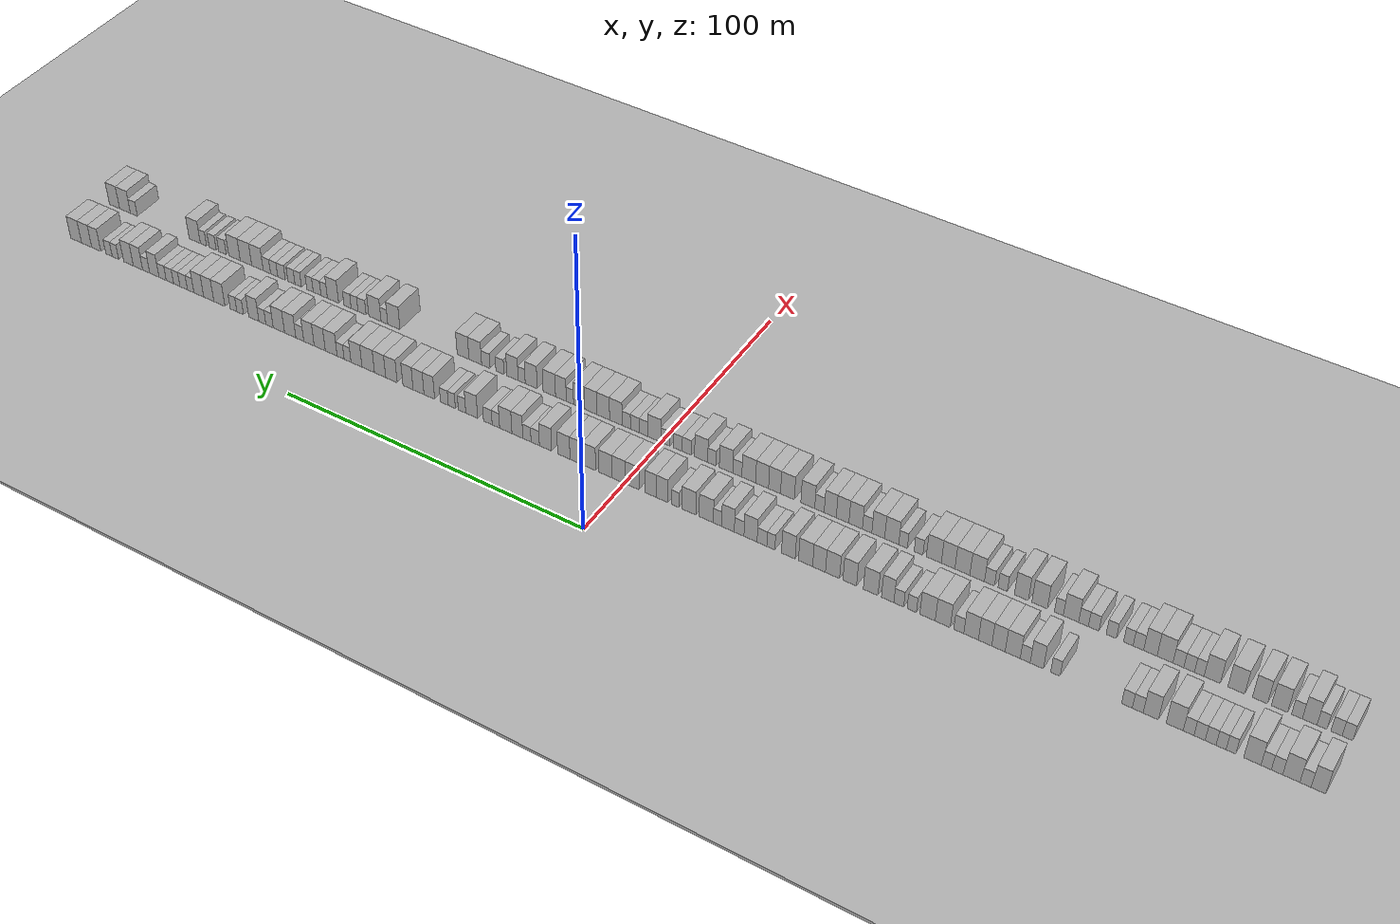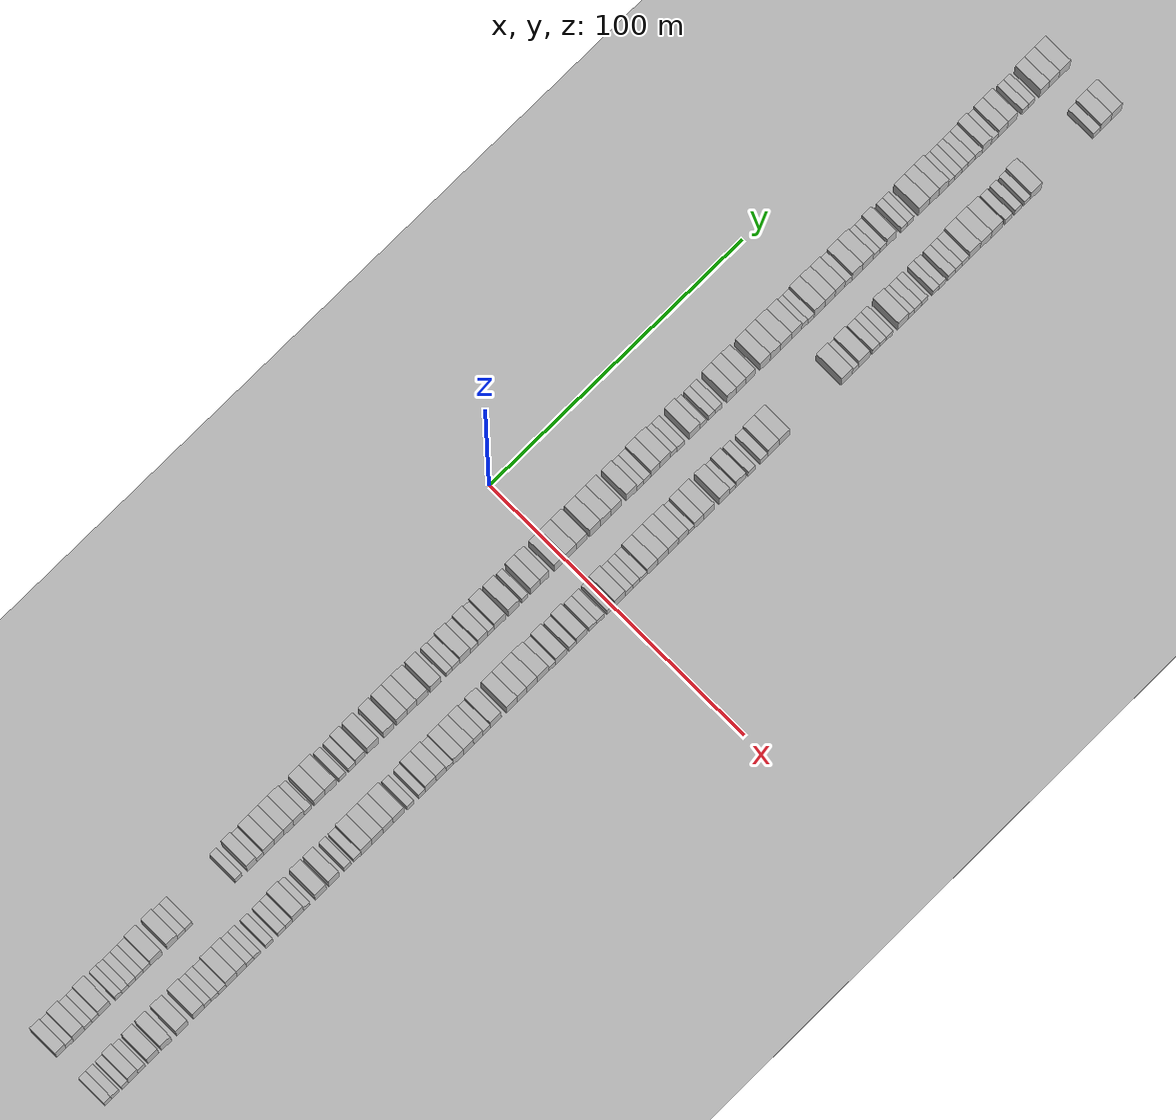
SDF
<?xml version="1.0" encoding="utf-8"?>

<sdf version="1.6">

   <world name="default">

      <gui fullscreen="0">

         <camera name="user_camera">

            <pose>-15 0 4.57585 0 0 0</pose>

            <view_controller>orbit</view_controller>

         </camera>

      </gui>

      <scene>

         <sky>

           <clouds>

             <speed>12</speed>

           </clouds>

         </sky>

         <ambient>0.4 0.4 0.4 1</ambient>

         <background>0.7 0.7 0.7 1</background>

         <shadows>1</shadows>

      </scene>

      <gravity>0 0 -9.8066</gravity>

      <magnetic_field>6e-06 2.3e-05 -4.2e-05</magnetic_field>

      <physics default="0" name="default_physics" type="ode">

         <ode>

            <solver>

               <type>quick</type>

               <iters>10</iters>

               <sor>1.0</sor>

               <use_dynamic_moi_rescaling>0</use_dynamic_moi_rescaling>

            </solver>

            <constraints>

               <cfm>0</cfm>

               <erp>0.2</erp>

               <contact_max_correcting_vel>100</contact_max_correcting_vel>

               <contact_surface_layer>0.001</contact_surface_layer>

            </constraints>

         </ode>

         <max_step_size>0.004</max_step_size>

         <real_time_factor>1</real_time_factor>

         <real_time_update_rate>250</real_time_update_rate>

      </physics>

      <light name="sun" type="directional">

         <cast_shadows>1</cast_shadows>

         <pose>0 0 10 0 0 0</pose>

         <diffuse>0.8 0.8 0.8 1</diffuse>

         <specular>0.2 0.2 0.2 1</specular>

         <attenuation>

            <range>1000</range>

            <constant>0.9</constant>

            <linear>0.01</linear>

            <quadratic>0.001</quadratic>

         </attenuation>

         <direction>-0.5 0.1 -0.9</direction>

      </light>

      <include>

         <name>ground_plane_1</name>

         <uri>model://HANNAS_ground_plane</uri>

         <pose>0 0 0  0 0 0</pose>

      </include>

      <include>

         <name>ground_plane_2</name>

         <uri>model://HANNAS_ground_plane</uri>

         <pose>100 0 0  0 0 0</pose>

      </include>

      <model name="building_1">

         <static>1</static>

         <pose frame="">25.0000 -196.1872 0 0.000000 0.000000 0.000000</pose>

         <link name="link">

            <pose frame="">0 0 4.50 0 0 0</pose>

            <collision name="collision">

               <geometry>

                  <box>

                     <size>10.0000 3.6256 9.0000</size>

                  </box>

               </geometry>

               <max_contacts>10</max_contacts>

               <surface>

                  <contact>

                     <ode/>

                  </contact>

                  <bounce/>

                  <friction>

                     <torsional>

                        <ode/>

                     </torsional>

                     <ode/>

                  </friction>

               </surface>

            </collision>

            <visual name="visual">

               <cast_shadows>0</cast_shadows>

               <geometry>

                  <box>

                     <size>10.0000 3.6256 9.0000</size>

                  </box>

               </geometry>

               <material>

                  <script>

                     <uri>model://HANNAS_wall/materials/scripts</uri>

                     <uri>model://HANNAS_wall/materials/textures</uri>

                     <name>vrc/HANNAS_wall</name>

                  </script>

               </material>

            </visual>

            <self_collide>0</self_collide>

            <enable_wind>0</enable_wind>

            <kinematic>0</kinematic>

         </link>

      </model>

      <model name="building_2">

         <static>1</static>

         <pose frame="">25.0000 -192.9768 0 0.000000 0.000000 0.000000</pose>

         <link name="link">

            <pose frame="">0 0 3.00 0 0 0</pose>

            <collision name="collision">

               <geometry>

                  <box>

                     <size>10.0000 2.7953 6.0000</size>

                  </box>

               </geometry>

               <max_contacts>10</max_contacts>

               <surface>

                  <contact>

                     <ode/>

                  </contact>

                  <bounce/>

                  <friction>

                     <torsional>

                        <ode/>

                     </torsional>

                     <ode/>

                  </friction>

               </surface>

            </collision>

            <visual name="visual">

               <cast_shadows>0</cast_shadows>

               <geometry>

                  <box>

                     <size>10.0000 2.7953 6.0000</size>

                  </box>

               </geometry>

               <material>

                  <script>

                     <uri>model://HANNAS_wall/materials/scripts</uri>

                     <uri>model://HANNAS_wall/materials/textures</uri>

                     <name>vrc/HANNAS_wall</name>

                  </script>

               </material>

            </visual>

            <self_collide>0</self_collide>

            <enable_wind>0</enable_wind>

            <kinematic>0</kinematic>

         </link>

      </model>

      <model name="building_3">

         <static>1</static>

         <pose frame="">25.0000 -189.4172 0 0.000000 0.000000 0.000000</pose>

         <link name="link">

            <pose frame="">0 0 4.50 0 0 0</pose>

            <collision name="collision">

               <geometry>

                  <box>

                     <size>10.0000 4.3239 9.0000</size>

                  </box>

               </geometry>

               <max_contacts>10</max_contacts>

               <surface>

                  <contact>

                     <ode/>

                  </contact>

                  <bounce/>

                  <friction>

                     <torsional>

                        <ode/>

                     </torsional>

                     <ode/>

                  </friction>

               </surface>

            </collision>

            <visual name="visual">

               <cast_shadows>0</cast_shadows>

               <geometry>

                  <box>

                     <size>10.0000 4.3239 9.0000</size>

                  </box>

               </geometry>

               <material>

                  <script>

                     <uri>model://HANNAS_wall/materials/scripts</uri>

                     <uri>model://HANNAS_wall/materials/textures</uri>

                     <name>vrc/HANNAS_wall</name>

                  </script>

               </material>

            </visual>

            <self_collide>0</self_collide>

            <enable_wind>0</enable_wind>

            <kinematic>0</kinematic>

         </link>

      </model>

      <model name="building_4">

         <static>1</static>

         <pose frame="">25.0000 -185.8251 0 0.000000 0.000000 0.000000</pose>

         <link name="link">

            <pose frame="">0 0 3.00 0 0 0</pose>

            <collision name="collision">

               <geometry>

                  <box>

                     <size>10.0000 2.8601 6.0000</size>

                  </box>

               </geometry>

               <max_contacts>10</max_contacts>

               <surface>

                  <contact>

                     <ode/>

                  </contact>

                  <bounce/>

                  <friction>

                     <torsional>

                        <ode/>

                     </torsional>

                     <ode/>

                  </friction>

               </surface>

            </collision>

            <visual name="visual">

               <cast_shadows>0</cast_shadows>

               <geometry>

                  <box>

                     <size>10.0000 2.8601 6.0000</size>

                  </box>

               </geometry>

               <material>

                  <script>

                     <uri>model://HANNAS_wall/materials/scripts</uri>

                     <uri>model://HANNAS_wall/materials/textures</uri>

                     <name>vrc/HANNAS_wall</name>

                  </script>

               </material>

            </visual>

            <self_collide>0</self_collide>

            <enable_wind>0</enable_wind>

            <kinematic>0</kinematic>

         </link>

      </model>

      <model name="building_5">

         <static>1</static>

         <pose frame="">25.0000 -183.0920 0 0.000000 0.000000 0.000000</pose>

         <link name="link">

            <pose frame="">0 0 3.00 0 0 0</pose>

            <collision name="collision">

               <geometry>

                  <box>

                     <size>10.0000 2.6062 6.0000</size>

                  </box>

               </geometry>

               <max_contacts>10</max_contacts>

               <surface>

                  <contact>

                     <ode/>

                  </contact>

                  <bounce/>

                  <friction>

                     <torsional>

                        <ode/>

                     </torsional>

                     <ode/>

                  </friction>

               </surface>

            </collision>

            <visual name="visual">

               <cast_shadows>0</cast_shadows>

               <geometry>

                  <box>

                     <size>10.0000 2.6062 6.0000</size>

                  </box>

               </geometry>

               <material>

                  <script>

                     <uri>model://HANNAS_wall/materials/scripts</uri>

                     <uri>model://HANNAS_wall/materials/textures</uri>

                     <name>vrc/HANNAS_wall</name>

                  </script>

               </material>

            </visual>

            <self_collide>0</self_collide>

            <enable_wind>0</enable_wind>

            <kinematic>0</kinematic>

         </link>

      </model>

      <model name="building_6">

         <static>1</static>

         <pose frame="">25.0000 -179.5854 0 0.000000 0.000000 0.000000</pose>

         <link name="link">

            <pose frame="">0 0 4.50 0 0 0</pose>

            <collision name="collision">

               <geometry>

                  <box>

                     <size>10.0000 4.4069 9.0000</size>

                  </box>

               </geometry>

               <max_contacts>10</max_contacts>

               <surface>

                  <contact>

                     <ode/>

                  </contact>

                  <bounce/>

                  <friction>

                     <torsional>

                        <ode/>

                     </torsional>

                     <ode/>

                  </friction>

               </surface>

            </collision>

            <visual name="visual">

               <cast_shadows>0</cast_shadows>

               <geometry>

                  <box>

                     <size>10.0000 4.4069 9.0000</size>

                  </box>

               </geometry>

               <material>

                  <script>

                     <uri>model://HANNAS_wall/materials/scripts</uri>

                     <uri>model://HANNAS_wall/materials/textures</uri>

                     <name>vrc/HANNAS_wall</name>

                  </script>

               </material>

            </visual>

            <self_collide>0</self_collide>

            <enable_wind>0</enable_wind>

            <kinematic>0</kinematic>

         </link>

      </model>

      <model name="building_7">

         <static>1</static>

         <pose frame="">25.0000 -174.1378 0 0.000000 0.000000 0.000000</pose>

         <link name="link">

            <pose frame="">0 0 3.00 0 0 0</pose>

            <collision name="collision">

               <geometry>

                  <box>

                     <size>10.0000 2.4883 6.0000</size>

                  </box>

               </geometry>

               <max_contacts>10</max_contacts>

               <surface>

                  <contact>

                     <ode/>

                  </contact>

                  <bounce/>

                  <friction>

                     <torsional>

                        <ode/>

                     </torsional>

                     <ode/>

                  </friction>

               </surface>

            </collision>

            <visual name="visual">

               <cast_shadows>0</cast_shadows>

               <geometry>

                  <box>

                     <size>10.0000 2.4883 6.0000</size>

                  </box>

               </geometry>

               <material>

                  <script>

                     <uri>model://HANNAS_wall/materials/scripts</uri>

                     <uri>model://HANNAS_wall/materials/textures</uri>

                     <name>vrc/HANNAS_wall</name>

                  </script>

               </material>

            </visual>

            <self_collide>0</self_collide>

            <enable_wind>0</enable_wind>

            <kinematic>0</kinematic>

         </link>

      </model>

      <model name="building_8">

         <static>1</static>

         <pose frame="">25.0000 -171.6017 0 0.000000 0.000000 0.000000</pose>

         <link name="link">

            <pose frame="">0 0 3.00 0 0 0</pose>

            <collision name="collision">

               <geometry>

                  <box>

                     <size>10.0000 2.5839 6.0000</size>

                  </box>

               </geometry>

               <max_contacts>10</max_contacts>

               <surface>

                  <contact>

                     <ode/>

                  </contact>

                  <bounce/>

                  <friction>

                     <torsional>

                        <ode/>

                     </torsional>

                     <ode/>

                  </friction>

               </surface>

            </collision>

            <visual name="visual">

               <cast_shadows>0</cast_shadows>

               <geometry>

                  <box>

                     <size>10.0000 2.5839 6.0000</size>

                  </box>

               </geometry>

               <material>

                  <script>

                     <uri>model://HANNAS_wall/materials/scripts</uri>

                     <uri>model://HANNAS_wall/materials/textures</uri>

                     <name>vrc/HANNAS_wall</name>

                  </script>

               </material>

            </visual>

            <self_collide>0</self_collide>

            <enable_wind>0</enable_wind>

            <kinematic>0</kinematic>

         </link>

      </model>

      <model name="building_9">

         <static>1</static>

         <pose frame="">25.0000 -168.9097 0 0.000000 0.000000 0.000000</pose>

         <link name="link">

            <pose frame="">0 0 3.00 0 0 0</pose>

            <collision name="collision">

               <geometry>

                  <box>

                     <size>10.0000 2.8001 6.0000</size>

                  </box>

               </geometry>

               <max_contacts>10</max_contacts>

               <surface>

                  <contact>

                     <ode/>

                  </contact>

                  <bounce/>

                  <friction>

                     <torsional>

                        <ode/>

                     </torsional>

                     <ode/>

                  </friction>

               </surface>

            </collision>

            <visual name="visual">

               <cast_shadows>0</cast_shadows>

               <geometry>

                  <box>

                     <size>10.0000 2.8001 6.0000</size>

                  </box>

               </geometry>

               <material>

                  <script>

                     <uri>model://HANNAS_wall/materials/scripts</uri>

                     <uri>model://HANNAS_wall/materials/textures</uri>

                     <name>vrc/HANNAS_wall</name>

                  </script>

               </material>

            </visual>

            <self_collide>0</self_collide>

            <enable_wind>0</enable_wind>

            <kinematic>0</kinematic>

         </link>

      </model>

      <model name="building_10">

         <static>1</static>

         <pose frame="">25.0000 -166.0650 0 0.000000 0.000000 0.000000</pose>

         <link name="link">

            <pose frame="">0 0 3.00 0 0 0</pose>

            <collision name="collision">

               <geometry>

                  <box>

                     <size>10.0000 2.8893 6.0000</size>

                  </box>

               </geometry>

               <max_contacts>10</max_contacts>

               <surface>

                  <contact>

                     <ode/>

                  </contact>

                  <bounce/>

                  <friction>

                     <torsional>

                        <ode/>

                     </torsional>

                     <ode/>

                  </friction>

               </surface>

            </collision>

            <visual name="visual">

               <cast_shadows>0</cast_shadows>

               <geometry>

                  <box>

                     <size>10.0000 2.8893 6.0000</size>

                  </box>

               </geometry>

               <material>

                  <script>

                     <uri>model://HANNAS_wall/materials/scripts</uri>

                     <uri>model://HANNAS_wall/materials/textures</uri>

                     <name>vrc/HANNAS_wall</name>

                  </script>

               </material>

            </visual>

            <self_collide>0</self_collide>

            <enable_wind>0</enable_wind>

            <kinematic>0</kinematic>

         </link>

      </model>

      <model name="building_11">

         <static>1</static>

         <pose frame="">25.0000 -163.2217 0 0.000000 0.000000 0.000000</pose>

         <link name="link">

            <pose frame="">0 0 3.00 0 0 0</pose>

            <collision name="collision">

               <geometry>

                  <box>

                     <size>10.0000 2.7973 6.0000</size>

                  </box>

               </geometry>

               <max_contacts>10</max_contacts>

               <surface>

                  <contact>

                     <ode/>

                  </contact>

                  <bounce/>

                  <friction>

                     <torsional>

                        <ode/>

                     </torsional>

                     <ode/>

                  </friction>

               </surface>

            </collision>

            <visual name="visual">

               <cast_shadows>0</cast_shadows>

               <geometry>

                  <box>

                     <size>10.0000 2.7973 6.0000</size>

                  </box>

               </geometry>

               <material>

                  <script>

                     <uri>model://HANNAS_wall/materials/scripts</uri>

                     <uri>model://HANNAS_wall/materials/textures</uri>

                     <name>vrc/HANNAS_wall</name>

                  </script>

               </material>

            </visual>

            <self_collide>0</self_collide>

            <enable_wind>0</enable_wind>

            <kinematic>0</kinematic>

         </link>

      </model>

      <model name="building_12">

         <static>1</static>

         <pose frame="">25.0000 -159.5874 0 0.000000 0.000000 0.000000</pose>

         <link name="link">

            <pose frame="">0 0 4.50 0 0 0</pose>

            <collision name="collision">

               <geometry>

                  <box>

                     <size>10.0000 4.4713 9.0000</size>

                  </box>

               </geometry>

               <max_contacts>10</max_contacts>

               <surface>

                  <contact>

                     <ode/>

                  </contact>

                  <bounce/>

                  <friction>

                     <torsional>

                        <ode/>

                     </torsional>

                     <ode/>

                  </friction>

               </surface>

            </collision>

            <visual name="visual">

               <cast_shadows>0</cast_shadows>

               <geometry>

                  <box>

                     <size>10.0000 4.4713 9.0000</size>

                  </box>

               </geometry>

               <material>

                  <script>

                     <uri>model://HANNAS_wall/materials/scripts</uri>

                     <uri>model://HANNAS_wall/materials/textures</uri>

                     <name>vrc/HANNAS_wall</name>

                  </script>

               </material>

            </visual>

            <self_collide>0</self_collide>

            <enable_wind>0</enable_wind>

            <kinematic>0</kinematic>

         </link>

      </model>

      <model name="building_13">

         <static>1</static>

         <pose frame="">25.0000 -153.3318 0 0.000000 0.000000 0.000000</pose>

         <link name="link">

            <pose frame="">0 0 4.50 0 0 0</pose>

            <collision name="collision">

               <geometry>

                  <box>

                     <size>10.0000 4.0397 9.0000</size>

                  </box>

               </geometry>

               <max_contacts>10</max_contacts>

               <surface>

                  <contact>

                     <ode/>

                  </contact>

                  <bounce/>

                  <friction>

                     <torsional>

                        <ode/>

                     </torsional>

                     <ode/>

                  </friction>

               </surface>

            </collision>

            <visual name="visual">

               <cast_shadows>0</cast_shadows>

               <geometry>

                  <box>

                     <size>10.0000 4.0397 9.0000</size>

                  </box>

               </geometry>

               <material>

                  <script>

                     <uri>model://HANNAS_wall/materials/scripts</uri>

                     <uri>model://HANNAS_wall/materials/textures</uri>

                     <name>vrc/HANNAS_wall</name>

                  </script>

               </material>

            </visual>

            <self_collide>0</self_collide>

            <enable_wind>0</enable_wind>

            <kinematic>0</kinematic>

         </link>

      </model>

      <model name="building_14">

         <static>1</static>

         <pose frame="">25.0000 -149.8733 0 0.000000 0.000000 0.000000</pose>

         <link name="link">

            <pose frame="">0 0 3.00 0 0 0</pose>

            <collision name="collision">

               <geometry>

                  <box>

                     <size>10.0000 2.8774 6.0000</size>

                  </box>

               </geometry>

               <max_contacts>10</max_contacts>

               <surface>

                  <contact>

                     <ode/>

                  </contact>

                  <bounce/>

                  <friction>

                     <torsional>

                        <ode/>

                     </torsional>

                     <ode/>

                  </friction>

               </surface>

            </collision>

            <visual name="visual">

               <cast_shadows>0</cast_shadows>

               <geometry>

                  <box>

                     <size>10.0000 2.8774 6.0000</size>

                  </box>

               </geometry>

               <material>

                  <script>

                     <uri>model://HANNAS_wall/materials/scripts</uri>

                     <uri>model://HANNAS_wall/materials/textures</uri>

                     <name>vrc/HANNAS_wall</name>

                  </script>

               </material>

            </visual>

            <self_collide>0</self_collide>

            <enable_wind>0</enable_wind>

            <kinematic>0</kinematic>

         </link>

      </model>

      <model name="building_15">

         <static>1</static>

         <pose frame="">25.0000 -147.0104 0 0.000000 0.000000 0.000000</pose>

         <link name="link">

            <pose frame="">0 0 3.00 0 0 0</pose>

            <collision name="collision">

               <geometry>

                  <box>

                     <size>10.0000 2.8483 6.0000</size>

                  </box>

               </geometry>

               <max_contacts>10</max_contacts>

               <surface>

                  <contact>

                     <ode/>

                  </contact>

                  <bounce/>

                  <friction>

                     <torsional>

                        <ode/>

                     </torsional>

                     <ode/>

                  </friction>

               </surface>

            </collision>

            <visual name="visual">

               <cast_shadows>0</cast_shadows>

               <geometry>

                  <box>

                     <size>10.0000 2.8483 6.0000</size>

                  </box>

               </geometry>

               <material>

                  <script>

                     <uri>model://HANNAS_wall/materials/scripts</uri>

                     <uri>model://HANNAS_wall/materials/textures</uri>

                     <name>vrc/HANNAS_wall</name>

                  </script>

               </material>

            </visual>

            <self_collide>0</self_collide>

            <enable_wind>0</enable_wind>

            <kinematic>0</kinematic>

         </link>

      </model>

      <model name="building_16">

         <static>1</static>

         <pose frame="">25.0000 -127.7283 0 0.000000 0.000000 0.000000</pose>

         <link name="link">

            <pose frame="">0 0 3.00 0 0 0</pose>

            <collision name="collision">

               <geometry>

                  <box>

                     <size>10.0000 2.5720 6.0000</size>

                  </box>

               </geometry>

               <max_contacts>10</max_contacts>

               <surface>

                  <contact>

                     <ode/>

                  </contact>

                  <bounce/>

                  <friction>

                     <torsional>

                        <ode/>

                     </torsional>

                     <ode/>

                  </friction>

               </surface>

            </collision>

            <visual name="visual">

               <cast_shadows>0</cast_shadows>

               <geometry>

                  <box>

                     <size>10.0000 2.5720 6.0000</size>

                  </box>

               </geometry>

               <material>

                  <script>

                     <uri>model://HANNAS_wall/materials/scripts</uri>

                     <uri>model://HANNAS_wall/materials/textures</uri>

                     <name>vrc/HANNAS_wall</name>

                  </script>

               </material>

            </visual>

            <self_collide>0</self_collide>

            <enable_wind>0</enable_wind>

            <kinematic>0</kinematic>

         </link>

      </model>

      <model name="building_17">

         <static>1</static>

         <pose frame="">25.0000 -122.6291 0 0.000000 0.000000 0.000000</pose>

         <link name="link">

            <pose frame="">0 0 4.50 0 0 0</pose>

            <collision name="collision">

               <geometry>

                  <box>

                     <size>10.0000 3.6263 9.0000</size>

                  </box>

               </geometry>

               <max_contacts>10</max_contacts>

               <surface>

                  <contact>

                     <ode/>

                  </contact>

                  <bounce/>

                  <friction>

                     <torsional>

                        <ode/>

                     </torsional>

                     <ode/>

                  </friction>

               </surface>

            </collision>

            <visual name="visual">

               <cast_shadows>0</cast_shadows>

               <geometry>

                  <box>

                     <size>10.0000 3.6263 9.0000</size>

                  </box>

               </geometry>

               <material>

                  <script>

                     <uri>model://HANNAS_wall/materials/scripts</uri>

                     <uri>model://HANNAS_wall/materials/textures</uri>

                     <name>vrc/HANNAS_wall</name>

                  </script>

               </material>

            </visual>

            <self_collide>0</self_collide>

            <enable_wind>0</enable_wind>

            <kinematic>0</kinematic>

         </link>

      </model>

      <model name="building_18">

         <static>1</static>

         <pose frame="">25.0000 -119.4527 0 0.000000 0.000000 0.000000</pose>

         <link name="link">

            <pose frame="">0 0 3.00 0 0 0</pose>

            <collision name="collision">

               <geometry>

                  <box>

                     <size>10.0000 2.7266 6.0000</size>

                  </box>

               </geometry>

               <max_contacts>10</max_contacts>

               <surface>

                  <contact>

                     <ode/>

                  </contact>

                  <bounce/>

                  <friction>

                     <torsional>

                        <ode/>

                     </torsional>

                     <ode/>

                  </friction>

               </surface>

            </collision>

            <visual name="visual">

               <cast_shadows>0</cast_shadows>

               <geometry>

                  <box>

                     <size>10.0000 2.7266 6.0000</size>

                  </box>

               </geometry>

               <material>

                  <script>

                     <uri>model://HANNAS_wall/materials/scripts</uri>

                     <uri>model://HANNAS_wall/materials/textures</uri>

                     <name>vrc/HANNAS_wall</name>

                  </script>

               </material>

            </visual>

            <self_collide>0</self_collide>

            <enable_wind>0</enable_wind>

            <kinematic>0</kinematic>

         </link>

      </model>

      <model name="building_19">

         <static>1</static>

         <pose frame="">25.0000 -115.9980 0 0.000000 0.000000 0.000000</pose>

         <link name="link">

            <pose frame="">0 0 4.50 0 0 0</pose>

            <collision name="collision">

               <geometry>

                  <box>

                     <size>10.0000 4.1827 9.0000</size>

                  </box>

               </geometry>

               <max_contacts>10</max_contacts>

               <surface>

                  <contact>

                     <ode/>

                  </contact>

                  <bounce/>

                  <friction>

                     <torsional>

                        <ode/>

                     </torsional>

                     <ode/>

                  </friction>

               </surface>

            </collision>

            <visual name="visual">

               <cast_shadows>0</cast_shadows>

               <geometry>

                  <box>

                     <size>10.0000 4.1827 9.0000</size>

                  </box>

               </geometry>

               <material>

                  <script>

                     <uri>model://HANNAS_wall/materials/scripts</uri>

                     <uri>model://HANNAS_wall/materials/textures</uri>

                     <name>vrc/HANNAS_wall</name>

                  </script>

               </material>

            </visual>

            <self_collide>0</self_collide>

            <enable_wind>0</enable_wind>

            <kinematic>0</kinematic>

         </link>

      </model>

      <model name="building_20">

         <static>1</static>

         <pose frame="">25.0000 -112.0309 0 0.000000 0.000000 0.000000</pose>

         <link name="link">

            <pose frame="">0 0 4.50 0 0 0</pose>

            <collision name="collision">

               <geometry>

                  <box>

                     <size>10.0000 3.7516 9.0000</size>

                  </box>

               </geometry>

               <max_contacts>10</max_contacts>

               <surface>

                  <contact>

                     <ode/>

                  </contact>

                  <bounce/>

                  <friction>

                     <torsional>

                        <ode/>

                     </torsional>

                     <ode/>

                  </friction>

               </surface>

            </collision>

            <visual name="visual">

               <cast_shadows>0</cast_shadows>

               <geometry>

                  <box>

                     <size>10.0000 3.7516 9.0000</size>

                  </box>

               </geometry>

               <material>

                  <script>

                     <uri>model://HANNAS_wall/materials/scripts</uri>

                     <uri>model://HANNAS_wall/materials/textures</uri>

                     <name>vrc/HANNAS_wall</name>

                  </script>

               </material>

            </visual>

            <self_collide>0</self_collide>

            <enable_wind>0</enable_wind>

            <kinematic>0</kinematic>

         </link>

      </model>

      <model name="building_21">

         <static>1</static>

         <pose frame="">25.0000 -108.2839 0 0.000000 0.000000 0.000000</pose>

         <link name="link">

            <pose frame="">0 0 4.50 0 0 0</pose>

            <collision name="collision">

               <geometry>

                  <box>

                     <size>10.0000 3.7425 9.0000</size>

                  </box>

               </geometry>

               <max_contacts>10</max_contacts>

               <surface>

                  <contact>

                     <ode/>

                  </contact>

                  <bounce/>

                  <friction>

                     <torsional>

                        <ode/>

                     </torsional>

                     <ode/>

                  </friction>

               </surface>

            </collision>

            <visual name="visual">

               <cast_shadows>0</cast_shadows>

               <geometry>

                  <box>

                     <size>10.0000 3.7425 9.0000</size>

                  </box>

               </geometry>

               <material>

                  <script>

                     <uri>model://HANNAS_wall/materials/scripts</uri>

                     <uri>model://HANNAS_wall/materials/textures</uri>

                     <name>vrc/HANNAS_wall</name>

                  </script>

               </material>

            </visual>

            <self_collide>0</self_collide>

            <enable_wind>0</enable_wind>

            <kinematic>0</kinematic>

         </link>

      </model>

      <model name="building_22">

         <static>1</static>

         <pose frame="">25.0000 -104.3630 0 0.000000 0.000000 0.000000</pose>

         <link name="link">

            <pose frame="">0 0 4.50 0 0 0</pose>

            <collision name="collision">

               <geometry>

                  <box>

                     <size>10.0000 4.0994 9.0000</size>

                  </box>

               </geometry>

               <max_contacts>10</max_contacts>

               <surface>

                  <contact>

                     <ode/>

                  </contact>

                  <bounce/>

                  <friction>

                     <torsional>

                        <ode/>

                     </torsional>

                     <ode/>

                  </friction>

               </surface>

            </collision>

            <visual name="visual">

               <cast_shadows>0</cast_shadows>

               <geometry>

                  <box>

                     <size>10.0000 4.0994 9.0000</size>

                  </box>

               </geometry>

               <material>

                  <script>

                     <uri>model://HANNAS_wall/materials/scripts</uri>

                     <uri>model://HANNAS_wall/materials/textures</uri>

                     <name>vrc/HANNAS_wall</name>

                  </script>

               </material>

            </visual>

            <self_collide>0</self_collide>

            <enable_wind>0</enable_wind>

            <kinematic>0</kinematic>

         </link>

      </model>

      <model name="building_23">

         <static>1</static>

         <pose frame="">25.0000 -100.8907 0 0.000000 0.000000 0.000000</pose>

         <link name="link">

            <pose frame="">0 0 3.00 0 0 0</pose>

            <collision name="collision">

               <geometry>

                  <box>

                     <size>10.0000 2.8451 6.0000</size>

                  </box>

               </geometry>

               <max_contacts>10</max_contacts>

               <surface>

                  <contact>

                     <ode/>

                  </contact>

                  <bounce/>

                  <friction>

                     <torsional>

                        <ode/>

                     </torsional>

                     <ode/>

                  </friction>

               </surface>

            </collision>

            <visual name="visual">

               <cast_shadows>0</cast_shadows>

               <geometry>

                  <box>

                     <size>10.0000 2.8451 6.0000</size>

                  </box>

               </geometry>

               <material>

                  <script>

                     <uri>model://HANNAS_wall/materials/scripts</uri>

                     <uri>model://HANNAS_wall/materials/textures</uri>

                     <name>vrc/HANNAS_wall</name>

                  </script>

               </material>

            </visual>

            <self_collide>0</self_collide>

            <enable_wind>0</enable_wind>

            <kinematic>0</kinematic>

         </link>

      </model>

      <model name="building_24">

         <static>1</static>

         <pose frame="">25.0000 -96.3340 0 0.000000 0.000000 0.000000</pose>

         <link name="link">

            <pose frame="">0 0 4.50 0 0 0</pose>

            <collision name="collision">

               <geometry>

                  <box>

                     <size>10.0000 4.2683 9.0000</size>

                  </box>

               </geometry>

               <max_contacts>10</max_contacts>

               <surface>

                  <contact>

                     <ode/>

                  </contact>

                  <bounce/>

                  <friction>

                     <torsional>

                        <ode/>

                     </torsional>

                     <ode/>

                  </friction>

               </surface>

            </collision>

            <visual name="visual">

               <cast_shadows>0</cast_shadows>

               <geometry>

                  <box>

                     <size>10.0000 4.2683 9.0000</size>

                  </box>

               </geometry>

               <material>

                  <script>

                     <uri>model://HANNAS_wall/materials/scripts</uri>

                     <uri>model://HANNAS_wall/materials/textures</uri>

                     <name>vrc/HANNAS_wall</name>

                  </script>

               </material>

            </visual>

            <self_collide>0</self_collide>

            <enable_wind>0</enable_wind>

            <kinematic>0</kinematic>

         </link>

      </model>

      <model name="building_25">

         <static>1</static>

         <pose frame="">25.0000 -92.0035 0 0.000000 0.000000 0.000000</pose>

         <link name="link">

            <pose frame="">0 0 4.50 0 0 0</pose>

            <collision name="collision">

               <geometry>

                  <box>

                     <size>10.0000 4.3929 9.0000</size>

                  </box>

               </geometry>

               <max_contacts>10</max_contacts>

               <surface>

                  <contact>

                     <ode/>

                  </contact>

                  <bounce/>

                  <friction>

                     <torsional>

                        <ode/>

                     </torsional>

                     <ode/>

                  </friction>

               </surface>

            </collision>

            <visual name="visual">

               <cast_shadows>0</cast_shadows>

               <geometry>

                  <box>

                     <size>10.0000 4.3929 9.0000</size>

                  </box>

               </geometry>

               <material>

                  <script>

                     <uri>model://HANNAS_wall/materials/scripts</uri>

                     <uri>model://HANNAS_wall/materials/textures</uri>

                     <name>vrc/HANNAS_wall</name>

                  </script>

               </material>

            </visual>

            <self_collide>0</self_collide>

            <enable_wind>0</enable_wind>

            <kinematic>0</kinematic>

         </link>

      </model>

      <model name="building_26">

         <static>1</static>

         <pose frame="">25.0000 -87.4747 0 0.000000 0.000000 0.000000</pose>

         <link name="link">

            <pose frame="">0 0 3.00 0 0 0</pose>

            <collision name="collision">

               <geometry>

                  <box>

                     <size>10.0000 2.6648 6.0000</size>

                  </box>

               </geometry>

               <max_contacts>10</max_contacts>

               <surface>

                  <contact>

                     <ode/>

                  </contact>

                  <bounce/>

                  <friction>

                     <torsional>

                        <ode/>

                     </torsional>

                     <ode/>

                  </friction>

               </surface>

            </collision>

            <visual name="visual">

               <cast_shadows>0</cast_shadows>

               <geometry>

                  <box>

                     <size>10.0000 2.6648 6.0000</size>

                  </box>

               </geometry>

               <material>

                  <script>

                     <uri>model://HANNAS_wall/materials/scripts</uri>

                     <uri>model://HANNAS_wall/materials/textures</uri>

                     <name>vrc/HANNAS_wall</name>

                  </script>

               </material>

            </visual>

            <self_collide>0</self_collide>

            <enable_wind>0</enable_wind>

            <kinematic>0</kinematic>

         </link>

      </model>

      <model name="building_27">

         <static>1</static>

         <pose frame="">25.0000 -83.7285 0 0.000000 0.000000 0.000000</pose>

         <link name="link">

            <pose frame="">0 0 3.00 0 0 0</pose>

            <collision name="collision">

               <geometry>

                  <box>

                     <size>10.0000 2.8275 6.0000</size>

                  </box>

               </geometry>

               <max_contacts>10</max_contacts>

               <surface>

                  <contact>

                     <ode/>

                  </contact>

                  <bounce/>

                  <friction>

                     <torsional>

                        <ode/>

                     </torsional>

                     <ode/>

                  </friction>

               </surface>

            </collision>

            <visual name="visual">

               <cast_shadows>0</cast_shadows>

               <geometry>

                  <box>

                     <size>10.0000 2.8275 6.0000</size>

                  </box>

               </geometry>

               <material>

                  <script>

                     <uri>model://HANNAS_wall/materials/scripts</uri>

                     <uri>model://HANNAS_wall/materials/textures</uri>

                     <name>vrc/HANNAS_wall</name>

                  </script>

               </material>

            </visual>

            <self_collide>0</self_collide>

            <enable_wind>0</enable_wind>

            <kinematic>0</kinematic>

         </link>

      </model>

      <model name="building_28">

         <static>1</static>

         <pose frame="">25.0000 -80.5029 0 0.000000 0.000000 0.000000</pose>

         <link name="link">

            <pose frame="">0 0 4.50 0 0 0</pose>

            <collision name="collision">

               <geometry>

                  <box>

                     <size>10.0000 3.6236 9.0000</size>

                  </box>

               </geometry>

               <max_contacts>10</max_contacts>

               <surface>

                  <contact>

                     <ode/>

                  </contact>

                  <bounce/>

                  <friction>

                     <torsional>

                        <ode/>

                     </torsional>

                     <ode/>

                  </friction>

               </surface>

            </collision>

            <visual name="visual">

               <cast_shadows>0</cast_shadows>

               <geometry>

                  <box>

                     <size>10.0000 3.6236 9.0000</size>

                  </box>

               </geometry>

               <material>

                  <script>

                     <uri>model://HANNAS_wall/materials/scripts</uri>

                     <uri>model://HANNAS_wall/materials/textures</uri>

                     <name>vrc/HANNAS_wall</name>

                  </script>

               </material>

            </visual>

            <self_collide>0</self_collide>

            <enable_wind>0</enable_wind>

            <kinematic>0</kinematic>

         </link>

      </model>

      <model name="building_29">

         <static>1</static>

         <pose frame="">25.0000 -75.5467 0 0.000000 0.000000 0.000000</pose>

         <link name="link">

            <pose frame="">0 0 4.50 0 0 0</pose>

            <collision name="collision">

               <geometry>

                  <box>

                     <size>10.0000 4.2889 9.0000</size>

                  </box>

               </geometry>

               <max_contacts>10</max_contacts>

               <surface>

                  <contact>

                     <ode/>

                  </contact>

                  <bounce/>

                  <friction>

                     <torsional>

                        <ode/>

                     </torsional>

                     <ode/>

                  </friction>

               </surface>

            </collision>

            <visual name="visual">

               <cast_shadows>0</cast_shadows>

               <geometry>

                  <box>

                     <size>10.0000 4.2889 9.0000</size>

                  </box>

               </geometry>

               <material>

                  <script>

                     <uri>model://HANNAS_wall/materials/scripts</uri>

                     <uri>model://HANNAS_wall/materials/textures</uri>

                     <name>vrc/HANNAS_wall</name>

                  </script>

               </material>

            </visual>

            <self_collide>0</self_collide>

            <enable_wind>0</enable_wind>

            <kinematic>0</kinematic>

         </link>

      </model>

      <model name="building_30">

         <static>1</static>

         <pose frame="">25.0000 -69.4031 0 0.000000 0.000000 0.000000</pose>

         <link name="link">

            <pose frame="">0 0 4.50 0 0 0</pose>

            <collision name="collision">

               <geometry>

                  <box>

                     <size>10.0000 3.9982 9.0000</size>

                  </box>

               </geometry>

               <max_contacts>10</max_contacts>

               <surface>

                  <contact>

                     <ode/>

                  </contact>

                  <bounce/>

                  <friction>

                     <torsional>

                        <ode/>

                     </torsional>

                     <ode/>

                  </friction>

               </surface>

            </collision>

            <visual name="visual">

               <cast_shadows>0</cast_shadows>

               <geometry>

                  <box>

                     <size>10.0000 3.9982 9.0000</size>

                  </box>

               </geometry>

               <material>

                  <script>

                     <uri>model://HANNAS_wall/materials/scripts</uri>

                     <uri>model://HANNAS_wall/materials/textures</uri>

                     <name>vrc/HANNAS_wall</name>

                  </script>

               </material>

            </visual>

            <self_collide>0</self_collide>

            <enable_wind>0</enable_wind>

            <kinematic>0</kinematic>

         </link>

      </model>

      <model name="building_31">

         <static>1</static>

         <pose frame="">25.0000 -64.3107 0 0.000000 0.000000 0.000000</pose>

         <link name="link">

            <pose frame="">0 0 4.50 0 0 0</pose>

            <collision name="collision">

               <geometry>

                  <box>

                     <size>10.0000 4.1865 9.0000</size>

                  </box>

               </geometry>

               <max_contacts>10</max_contacts>

               <surface>

                  <contact>

                     <ode/>

                  </contact>

                  <bounce/>

                  <friction>

                     <torsional>

                        <ode/>

                     </torsional>

                     <ode/>

                  </friction>

               </surface>

            </collision>

            <visual name="visual">

               <cast_shadows>0</cast_shadows>

               <geometry>

                  <box>

                     <size>10.0000 4.1865 9.0000</size>

                  </box>

               </geometry>

               <material>

                  <script>

                     <uri>model://HANNAS_wall/materials/scripts</uri>

                     <uri>model://HANNAS_wall/materials/textures</uri>

                     <name>vrc/HANNAS_wall</name>

                  </script>

               </material>

            </visual>

            <self_collide>0</self_collide>

            <enable_wind>0</enable_wind>

            <kinematic>0</kinematic>

         </link>

      </model>

      <model name="building_32">

         <static>1</static>

         <pose frame="">25.0000 -60.3107 0 0.000000 0.000000 0.000000</pose>

         <link name="link">

            <pose frame="">0 0 4.50 0 0 0</pose>

            <collision name="collision">

               <geometry>

                  <box>

                     <size>10.0000 3.8135 9.0000</size>

                  </box>

               </geometry>

               <max_contacts>10</max_contacts>

               <surface>

                  <contact>

                     <ode/>

                  </contact>

                  <bounce/>

                  <friction>

                     <torsional>

                        <ode/>

                     </torsional>

                     <ode/>

                  </friction>

               </surface>

            </collision>

            <visual name="visual">

               <cast_shadows>0</cast_shadows>

               <geometry>

                  <box>

                     <size>10.0000 3.8135 9.0000</size>

                  </box>

               </geometry>

               <material>

                  <script>

                     <uri>model://HANNAS_wall/materials/scripts</uri>

                     <uri>model://HANNAS_wall/materials/textures</uri>

                     <name>vrc/HANNAS_wall</name>

                  </script>

               </material>

            </visual>

            <self_collide>0</self_collide>

            <enable_wind>0</enable_wind>

            <kinematic>0</kinematic>

         </link>

      </model>

      <model name="building_33">

         <static>1</static>

         <pose frame="">25.0000 -56.2787 0 0.000000 0.000000 0.000000</pose>

         <link name="link">

            <pose frame="">0 0 4.50 0 0 0</pose>

            <collision name="collision">

               <geometry>

                  <box>

                     <size>10.0000 4.2505 9.0000</size>

                  </box>

               </geometry>

               <max_contacts>10</max_contacts>

               <surface>

                  <contact>

                     <ode/>

                  </contact>

                  <bounce/>

                  <friction>

                     <torsional>

                        <ode/>

                     </torsional>

                     <ode/>

                  </friction>

               </surface>

            </collision>

            <visual name="visual">

               <cast_shadows>0</cast_shadows>

               <geometry>

                  <box>

                     <size>10.0000 4.2505 9.0000</size>

                  </box>

               </geometry>

               <material>

                  <script>

                     <uri>model://HANNAS_wall/materials/scripts</uri>

                     <uri>model://HANNAS_wall/materials/textures</uri>

                     <name>vrc/HANNAS_wall</name>

                  </script>

               </material>

            </visual>

            <self_collide>0</self_collide>

            <enable_wind>0</enable_wind>

            <kinematic>0</kinematic>

         </link>

      </model>

      <model name="building_34">

         <static>1</static>

         <pose frame="">25.0000 -51.0854 0 0.000000 0.000000 0.000000</pose>

         <link name="link">

            <pose frame="">0 0 4.50 0 0 0</pose>

            <collision name="collision">

               <geometry>

                  <box>

                     <size>10.0000 4.1361 9.0000</size>

                  </box>

               </geometry>

               <max_contacts>10</max_contacts>

               <surface>

                  <contact>

                     <ode/>

                  </contact>

                  <bounce/>

                  <friction>

                     <torsional>

                        <ode/>

                     </torsional>

                     <ode/>

                  </friction>

               </surface>

            </collision>

            <visual name="visual">

               <cast_shadows>0</cast_shadows>

               <geometry>

                  <box>

                     <size>10.0000 4.1361 9.0000</size>

                  </box>

               </geometry>

               <material>

                  <script>

                     <uri>model://HANNAS_wall/materials/scripts</uri>

                     <uri>model://HANNAS_wall/materials/textures</uri>

                     <name>vrc/HANNAS_wall</name>

                  </script>

               </material>

            </visual>

            <self_collide>0</self_collide>

            <enable_wind>0</enable_wind>

            <kinematic>0</kinematic>

         </link>

      </model>

      <model name="building_35">

         <static>1</static>

         <pose frame="">25.0000 -45.7949 0 0.000000 0.000000 0.000000</pose>

         <link name="link">

            <pose frame="">0 0 3.00 0 0 0</pose>

            <collision name="collision">

               <geometry>

                  <box>

                     <size>10.0000 2.4448 6.0000</size>

                  </box>

               </geometry>

               <max_contacts>10</max_contacts>

               <surface>

                  <contact>

                     <ode/>

                  </contact>

                  <bounce/>

                  <friction>

                     <torsional>

                        <ode/>

                     </torsional>

                     <ode/>

                  </friction>

               </surface>

            </collision>

            <visual name="visual">

               <cast_shadows>0</cast_shadows>

               <geometry>

                  <box>

                     <size>10.0000 2.4448 6.0000</size>

                  </box>

               </geometry>

               <material>

                  <script>

                     <uri>model://HANNAS_wall/materials/scripts</uri>

                     <uri>model://HANNAS_wall/materials/textures</uri>

                     <name>vrc/HANNAS_wall</name>

                  </script>

               </material>

            </visual>

            <self_collide>0</self_collide>

            <enable_wind>0</enable_wind>

            <kinematic>0</kinematic>

         </link>

      </model>

      <model name="building_36">

         <static>1</static>

         <pose frame="">25.0000 -43.0886 0 0.000000 0.000000 0.000000</pose>

         <link name="link">

            <pose frame="">0 0 3.00 0 0 0</pose>

            <collision name="collision">

               <geometry>

                  <box>

                     <size>10.0000 2.9679 6.0000</size>

                  </box>

               </geometry>

               <max_contacts>10</max_contacts>

               <surface>

                  <contact>

                     <ode/>

                  </contact>

                  <bounce/>

                  <friction>

                     <torsional>

                        <ode/>

                     </torsional>

                     <ode/>

                  </friction>

               </surface>

            </collision>

            <visual name="visual">

               <cast_shadows>0</cast_shadows>

               <geometry>

                  <box>

                     <size>10.0000 2.9679 6.0000</size>

                  </box>

               </geometry>

               <material>

                  <script>

                     <uri>model://HANNAS_wall/materials/scripts</uri>

                     <uri>model://HANNAS_wall/materials/textures</uri>

                     <name>vrc/HANNAS_wall</name>

                  </script>

               </material>

            </visual>

            <self_collide>0</self_collide>

            <enable_wind>0</enable_wind>

            <kinematic>0</kinematic>

         </link>

      </model>

      <model name="building_37">

         <static>1</static>

         <pose frame="">25.0000 -39.5950 0 0.000000 0.000000 0.000000</pose>

         <link name="link">

            <pose frame="">0 0 4.50 0 0 0</pose>

            <collision name="collision">

               <geometry>

                  <box>

                     <size>10.0000 4.0194 9.0000</size>

                  </box>

               </geometry>

               <max_contacts>10</max_contacts>

               <surface>

                  <contact>

                     <ode/>

                  </contact>

                  <bounce/>

                  <friction>

                     <torsional>

                        <ode/>

                     </torsional>

                     <ode/>

                  </friction>

               </surface>

            </collision>

            <visual name="visual">

               <cast_shadows>0</cast_shadows>

               <geometry>

                  <box>

                     <size>10.0000 4.0194 9.0000</size>

                  </box>

               </geometry>

               <material>

                  <script>

                     <uri>model://HANNAS_wall/materials/scripts</uri>

                     <uri>model://HANNAS_wall/materials/textures</uri>

                     <name>vrc/HANNAS_wall</name>

                  </script>

               </material>

            </visual>

            <self_collide>0</self_collide>

            <enable_wind>0</enable_wind>

            <kinematic>0</kinematic>

         </link>

      </model>

      <model name="building_38">

         <static>1</static>

         <pose frame="">25.0000 -36.0967 0 0.000000 0.000000 0.000000</pose>

         <link name="link">

            <pose frame="">0 0 3.00 0 0 0</pose>

            <collision name="collision">

               <geometry>

                  <box>

                     <size>10.0000 2.9772 6.0000</size>

                  </box>

               </geometry>

               <max_contacts>10</max_contacts>

               <surface>

                  <contact>

                     <ode/>

                  </contact>

                  <bounce/>

                  <friction>

                     <torsional>

                        <ode/>

                     </torsional>

                     <ode/>

                  </friction>

               </surface>

            </collision>

            <visual name="visual">

               <cast_shadows>0</cast_shadows>

               <geometry>

                  <box>

                     <size>10.0000 2.9772 6.0000</size>

                  </box>

               </geometry>

               <material>

                  <script>

                     <uri>model://HANNAS_wall/materials/scripts</uri>

                     <uri>model://HANNAS_wall/materials/textures</uri>

                     <name>vrc/HANNAS_wall</name>

                  </script>

               </material>

            </visual>

            <self_collide>0</self_collide>

            <enable_wind>0</enable_wind>

            <kinematic>0</kinematic>

         </link>

      </model>

      <model name="building_39">

         <static>1</static>

         <pose frame="">25.0000 -32.6486 0 0.000000 0.000000 0.000000</pose>

         <link name="link">

            <pose frame="">0 0 4.50 0 0 0</pose>

            <collision name="collision">

               <geometry>

                  <box>

                     <size>10.0000 3.9190 9.0000</size>

                  </box>

               </geometry>

               <max_contacts>10</max_contacts>

               <surface>

                  <contact>

                     <ode/>

                  </contact>

                  <bounce/>

                  <friction>

                     <torsional>

                        <ode/>

                     </torsional>

                     <ode/>

                  </friction>

               </surface>

            </collision>

            <visual name="visual">

               <cast_shadows>0</cast_shadows>

               <geometry>

                  <box>

                     <size>10.0000 3.9190 9.0000</size>

                  </box>

               </geometry>

               <material>

                  <script>

                     <uri>model://HANNAS_wall/materials/scripts</uri>

                     <uri>model://HANNAS_wall/materials/textures</uri>

                     <name>vrc/HANNAS_wall</name>

                  </script>

               </material>

            </visual>

            <self_collide>0</self_collide>

            <enable_wind>0</enable_wind>

            <kinematic>0</kinematic>

         </link>

      </model>

      <model name="building_40">

         <static>1</static>

         <pose frame="">25.0000 -29.4030 0 0.000000 0.000000 0.000000</pose>

         <link name="link">

            <pose frame="">0 0 3.00 0 0 0</pose>

            <collision name="collision">

               <geometry>

                  <box>

                     <size>10.0000 2.5723 6.0000</size>

                  </box>

               </geometry>

               <max_contacts>10</max_contacts>

               <surface>

                  <contact>

                     <ode/>

                  </contact>

                  <bounce/>

                  <friction>

                     <torsional>

                        <ode/>

                     </torsional>

                     <ode/>

                  </friction>

               </surface>

            </collision>

            <visual name="visual">

               <cast_shadows>0</cast_shadows>

               <geometry>

                  <box>

                     <size>10.0000 2.5723 6.0000</size>

                  </box>

               </geometry>

               <material>

                  <script>

                     <uri>model://HANNAS_wall/materials/scripts</uri>

                     <uri>model://HANNAS_wall/materials/textures</uri>

                     <name>vrc/HANNAS_wall</name>

                  </script>

               </material>

            </visual>

            <self_collide>0</self_collide>

            <enable_wind>0</enable_wind>

            <kinematic>0</kinematic>

         </link>

      </model>

      <model name="building_41">

         <static>1</static>

         <pose frame="">25.0000 -25.9004 0 0.000000 0.000000 0.000000</pose>

         <link name="link">

            <pose frame="">0 0 4.50 0 0 0</pose>

            <collision name="collision">

               <geometry>

                  <box>

                     <size>10.0000 4.4328 9.0000</size>

                  </box>

               </geometry>

               <max_contacts>10</max_contacts>

               <surface>

                  <contact>

                     <ode/>

                  </contact>

                  <bounce/>

                  <friction>

                     <torsional>

                        <ode/>

                     </torsional>

                     <ode/>

                  </friction>

               </surface>

            </collision>

            <visual name="visual">

               <cast_shadows>0</cast_shadows>

               <geometry>

                  <box>

                     <size>10.0000 4.4328 9.0000</size>

                  </box>

               </geometry>

               <material>

                  <script>

                     <uri>model://HANNAS_wall/materials/scripts</uri>

                     <uri>model://HANNAS_wall/materials/textures</uri>

                     <name>vrc/HANNAS_wall</name>

                  </script>

               </material>

            </visual>

            <self_collide>0</self_collide>

            <enable_wind>0</enable_wind>

            <kinematic>0</kinematic>

         </link>

      </model>

      <model name="building_42">

         <static>1</static>

         <pose frame="">25.0000 -20.5050 0 0.000000 0.000000 0.000000</pose>

         <link name="link">

            <pose frame="">0 0 4.50 0 0 0</pose>

            <collision name="collision">

               <geometry>

                  <box>

                     <size>10.0000 4.3582 9.0000</size>

                  </box>

               </geometry>

               <max_contacts>10</max_contacts>

               <surface>

                  <contact>

                     <ode/>

                  </contact>

                  <bounce/>

                  <friction>

                     <torsional>

                        <ode/>

                     </torsional>

                     <ode/>

                  </friction>

               </surface>

            </collision>

            <visual name="visual">

               <cast_shadows>0</cast_shadows>

               <geometry>

                  <box>

                     <size>10.0000 4.3582 9.0000</size>

                  </box>

               </geometry>

               <material>

                  <script>

                     <uri>model://HANNAS_wall/materials/scripts</uri>

                     <uri>model://HANNAS_wall/materials/textures</uri>

                     <name>vrc/HANNAS_wall</name>

                  </script>

               </material>

            </visual>

            <self_collide>0</self_collide>

            <enable_wind>0</enable_wind>

            <kinematic>0</kinematic>

         </link>

      </model>

      <model name="building_43">

         <static>1</static>

         <pose frame="">25.0000 -16.1089 0 0.000000 0.000000 0.000000</pose>

         <link name="link">

            <pose frame="">0 0 3.00 0 0 0</pose>

            <collision name="collision">

               <geometry>

                  <box>

                     <size>10.0000 2.4340 6.0000</size>

                  </box>

               </geometry>

               <max_contacts>10</max_contacts>

               <surface>

                  <contact>

                     <ode/>

                  </contact>

                  <bounce/>

                  <friction>

                     <torsional>

                        <ode/>

                     </torsional>

                     <ode/>

                  </friction>

               </surface>

            </collision>

            <visual name="visual">

               <cast_shadows>0</cast_shadows>

               <geometry>

                  <box>

                     <size>10.0000 2.4340 6.0000</size>

                  </box>

               </geometry>

               <material>

                  <script>

                     <uri>model://HANNAS_wall/materials/scripts</uri>

                     <uri>model://HANNAS_wall/materials/textures</uri>

                     <name>vrc/HANNAS_wall</name>

                  </script>

               </material>

            </visual>

            <self_collide>0</self_collide>

            <enable_wind>0</enable_wind>

            <kinematic>0</kinematic>

         </link>

      </model>

      <model name="building_44">

         <static>1</static>

         <pose frame="">25.0000 -12.0789 0 0.000000 0.000000 0.000000</pose>

         <link name="link">

            <pose frame="">0 0 4.50 0 0 0</pose>

            <collision name="collision">

               <geometry>

                  <box>

                     <size>10.0000 3.6259 9.0000</size>

                  </box>

               </geometry>

               <max_contacts>10</max_contacts>

               <surface>

                  <contact>

                     <ode/>

                  </contact>

                  <bounce/>

                  <friction>

                     <torsional>

                        <ode/>

                     </torsional>

                     <ode/>

                  </friction>

               </surface>

            </collision>

            <visual name="visual">

               <cast_shadows>0</cast_shadows>

               <geometry>

                  <box>

                     <size>10.0000 3.6259 9.0000</size>

                  </box>

               </geometry>

               <material>

                  <script>

                     <uri>model://HANNAS_wall/materials/scripts</uri>

                     <uri>model://HANNAS_wall/materials/textures</uri>

                     <name>vrc/HANNAS_wall</name>

                  </script>

               </material>

            </visual>

            <self_collide>0</self_collide>

            <enable_wind>0</enable_wind>

            <kinematic>0</kinematic>

         </link>

      </model>

      <model name="building_45">

         <static>1</static>

         <pose frame="">25.0000 -8.4605 0 0.000000 0.000000 0.000000</pose>

         <link name="link">

            <pose frame="">0 0 4.50 0 0 0</pose>

            <collision name="collision">

               <geometry>

                  <box>

                     <size>10.0000 3.6108 9.0000</size>

                  </box>

               </geometry>

               <max_contacts>10</max_contacts>

               <surface>

                  <contact>

                     <ode/>

                  </contact>

                  <bounce/>

                  <friction>

                     <torsional>

                        <ode/>

                     </torsional>

                     <ode/>

                  </friction>

               </surface>

            </collision>

            <visual name="visual">

               <cast_shadows>0</cast_shadows>

               <geometry>

                  <box>

                     <size>10.0000 3.6108 9.0000</size>

                  </box>

               </geometry>

               <material>

                  <script>

                     <uri>model://HANNAS_wall/materials/scripts</uri>

                     <uri>model://HANNAS_wall/materials/textures</uri>

                     <name>vrc/HANNAS_wall</name>

                  </script>

               </material>

            </visual>

            <self_collide>0</self_collide>

            <enable_wind>0</enable_wind>

            <kinematic>0</kinematic>

         </link>

      </model>

      <model name="building_46">

         <static>1</static>

         <pose frame="">25.0000 -2.4725 0 0.000000 0.000000 0.000000</pose>

         <link name="link">

            <pose frame="">0 0 4.50 0 0 0</pose>

            <collision name="collision">

               <geometry>

                  <box>

                     <size>10.0000 4.3652 9.0000</size>

                  </box>

               </geometry>

               <max_contacts>10</max_contacts>

               <surface>

                  <contact>

                     <ode/>

                  </contact>

                  <bounce/>

                  <friction>

                     <torsional>

                        <ode/>

                     </torsional>

                     <ode/>

                  </friction>

               </surface>

            </collision>

            <visual name="visual">

               <cast_shadows>0</cast_shadows>

               <geometry>

                  <box>

                     <size>10.0000 4.3652 9.0000</size>

                  </box>

               </geometry>

               <material>

                  <script>

                     <uri>model://HANNAS_wall/materials/scripts</uri>

                     <uri>model://HANNAS_wall/materials/textures</uri>

                     <name>vrc/HANNAS_wall</name>

                  </script>

               </material>

            </visual>

            <self_collide>0</self_collide>

            <enable_wind>0</enable_wind>

            <kinematic>0</kinematic>

         </link>

      </model>

      <model name="building_47">

         <static>1</static>

         <pose frame="">25.0000 1.8716 0 0.000000 0.000000 0.000000</pose>

         <link name="link">

            <pose frame="">0 0 4.50 0 0 0</pose>

            <collision name="collision">

               <geometry>

                  <box>

                     <size>10.0000 4.3229 9.0000</size>

                  </box>

               </geometry>

               <max_contacts>10</max_contacts>

               <surface>

                  <contact>

                     <ode/>

                  </contact>

                  <bounce/>

                  <friction>

                     <torsional>

                        <ode/>

                     </torsional>

                     <ode/>

                  </friction>

               </surface>

            </collision>

            <visual name="visual">

               <cast_shadows>0</cast_shadows>

               <geometry>

                  <box>

                     <size>10.0000 4.3229 9.0000</size>

                  </box>

               </geometry>

               <material>

                  <script>

                     <uri>model://HANNAS_wall/materials/scripts</uri>

                     <uri>model://HANNAS_wall/materials/textures</uri>

                     <name>vrc/HANNAS_wall</name>

                  </script>

               </material>

            </visual>

            <self_collide>0</self_collide>

            <enable_wind>0</enable_wind>

            <kinematic>0</kinematic>

         </link>

      </model>

      <model name="building_48">

         <static>1</static>

         <pose frame="">25.0000 6.1837 0 0.000000 0.000000 0.000000</pose>

         <link name="link">

            <pose frame="">0 0 4.50 0 0 0</pose>

            <collision name="collision">

               <geometry>

                  <box>

                     <size>10.0000 4.3014 9.0000</size>

                  </box>

               </geometry>

               <max_contacts>10</max_contacts>

               <surface>

                  <contact>

                     <ode/>

                  </contact>

                  <bounce/>

                  <friction>

                     <torsional>

                        <ode/>

                     </torsional>

                     <ode/>

                  </friction>

               </surface>

            </collision>

            <visual name="visual">

               <cast_shadows>0</cast_shadows>

               <geometry>

                  <box>

                     <size>10.0000 4.3014 9.0000</size>

                  </box>

               </geometry>

               <material>

                  <script>

                     <uri>model://HANNAS_wall/materials/scripts</uri>

                     <uri>model://HANNAS_wall/materials/textures</uri>

                     <name>vrc/HANNAS_wall</name>

                  </script>

               </material>

            </visual>

            <self_collide>0</self_collide>

            <enable_wind>0</enable_wind>

            <kinematic>0</kinematic>

         </link>

      </model>

      <model name="building_49">

         <static>1</static>

         <pose frame="">25.0000 11.4500 0 0.000000 0.000000 0.000000</pose>

         <link name="link">

            <pose frame="">0 0 4.50 0 0 0</pose>

            <collision name="collision">

               <geometry>

                  <box>

                     <size>10.0000 4.2313 9.0000</size>

                  </box>

               </geometry>

               <max_contacts>10</max_contacts>

               <surface>

                  <contact>

                     <ode/>

                  </contact>

                  <bounce/>

                  <friction>

                     <torsional>

                        <ode/>

                     </torsional>

                     <ode/>

                  </friction>

               </surface>

            </collision>

            <visual name="visual">

               <cast_shadows>0</cast_shadows>

               <geometry>

                  <box>

                     <size>10.0000 4.2313 9.0000</size>

                  </box>

               </geometry>

               <material>

                  <script>

                     <uri>model://HANNAS_wall/materials/scripts</uri>

                     <uri>model://HANNAS_wall/materials/textures</uri>

                     <name>vrc/HANNAS_wall</name>

                  </script>

               </material>

            </visual>

            <self_collide>0</self_collide>

            <enable_wind>0</enable_wind>

            <kinematic>0</kinematic>

         </link>

      </model>

      <model name="building_50">

         <static>1</static>

         <pose frame="">25.0000 15.6476 0 0.000000 0.000000 0.000000</pose>

         <link name="link">

            <pose frame="">0 0 4.50 0 0 0</pose>

            <collision name="collision">

               <geometry>

                  <box>

                     <size>10.0000 4.1638 9.0000</size>

                  </box>

               </geometry>

               <max_contacts>10</max_contacts>

               <surface>

                  <contact>

                     <ode/>

                  </contact>

                  <bounce/>

                  <friction>

                     <torsional>

                        <ode/>

                     </torsional>

                     <ode/>

                  </friction>

               </surface>

            </collision>

            <visual name="visual">

               <cast_shadows>0</cast_shadows>

               <geometry>

                  <box>

                     <size>10.0000 4.1638 9.0000</size>

                  </box>

               </geometry>

               <material>

                  <script>

                     <uri>model://HANNAS_wall/materials/scripts</uri>

                     <uri>model://HANNAS_wall/materials/textures</uri>

                     <name>vrc/HANNAS_wall</name>

                  </script>

               </material>

            </visual>

            <self_collide>0</self_collide>

            <enable_wind>0</enable_wind>

            <kinematic>0</kinematic>

         </link>

      </model>

      <model name="building_51">

         <static>1</static>

         <pose frame="">25.0000 19.7668 0 0.000000 0.000000 0.000000</pose>

         <link name="link">

            <pose frame="">0 0 4.50 0 0 0</pose>

            <collision name="collision">

               <geometry>

                  <box>

                     <size>10.0000 4.0746 9.0000</size>

                  </box>

               </geometry>

               <max_contacts>10</max_contacts>

               <surface>

                  <contact>

                     <ode/>

                  </contact>

                  <bounce/>

                  <friction>

                     <torsional>

                        <ode/>

                     </torsional>

                     <ode/>

                  </friction>

               </surface>

            </collision>

            <visual name="visual">

               <cast_shadows>0</cast_shadows>

               <geometry>

                  <box>

                     <size>10.0000 4.0746 9.0000</size>

                  </box>

               </geometry>

               <material>

                  <script>

                     <uri>model://HANNAS_wall/materials/scripts</uri>

                     <uri>model://HANNAS_wall/materials/textures</uri>

                     <name>vrc/HANNAS_wall</name>

                  </script>

               </material>

            </visual>

            <self_collide>0</self_collide>

            <enable_wind>0</enable_wind>

            <kinematic>0</kinematic>

         </link>

      </model>

      <model name="building_52">

         <static>1</static>

         <pose frame="">25.0000 25.8282 0 0.000000 0.000000 0.000000</pose>

         <link name="link">

            <pose frame="">0 0 4.50 0 0 0</pose>

            <collision name="collision">

               <geometry>

                  <box>

                     <size>10.0000 4.0484 9.0000</size>

                  </box>

               </geometry>

               <max_contacts>10</max_contacts>

               <surface>

                  <contact>

                     <ode/>

                  </contact>

                  <bounce/>

                  <friction>

                     <torsional>

                        <ode/>

                     </torsional>

                     <ode/>

                  </friction>

               </surface>

            </collision>

            <visual name="visual">

               <cast_shadows>0</cast_shadows>

               <geometry>

                  <box>

                     <size>10.0000 4.0484 9.0000</size>

                  </box>

               </geometry>

               <material>

                  <script>

                     <uri>model://HANNAS_wall/materials/scripts</uri>

                     <uri>model://HANNAS_wall/materials/textures</uri>

                     <name>vrc/HANNAS_wall</name>

                  </script>

               </material>

            </visual>

            <self_collide>0</self_collide>

            <enable_wind>0</enable_wind>

            <kinematic>0</kinematic>

         </link>

      </model>

      <model name="building_53">

         <static>1</static>

         <pose frame="">25.0000 29.2500 0 0.000000 0.000000 0.000000</pose>

         <link name="link">

            <pose frame="">0 0 3.00 0 0 0</pose>

            <collision name="collision">

               <geometry>

                  <box>

                     <size>10.0000 2.7951 6.0000</size>

                  </box>

               </geometry>

               <max_contacts>10</max_contacts>

               <surface>

                  <contact>

                     <ode/>

                  </contact>

                  <bounce/>

                  <friction>

                     <torsional>

                        <ode/>

                     </torsional>

                     <ode/>

                  </friction>

               </surface>

            </collision>

            <visual name="visual">

               <cast_shadows>0</cast_shadows>

               <geometry>

                  <box>

                     <size>10.0000 2.7951 6.0000</size>

                  </box>

               </geometry>

               <material>

                  <script>

                     <uri>model://HANNAS_wall/materials/scripts</uri>

                     <uri>model://HANNAS_wall/materials/textures</uri>

                     <name>vrc/HANNAS_wall</name>

                  </script>

               </material>

            </visual>

            <self_collide>0</self_collide>

            <enable_wind>0</enable_wind>

            <kinematic>0</kinematic>

         </link>

      </model>

      <model name="building_54">

         <static>1</static>

         <pose frame="">25.0000 32.0078 0 0.000000 0.000000 0.000000</pose>

         <link name="link">

            <pose frame="">0 0 3.00 0 0 0</pose>

            <collision name="collision">

               <geometry>

                  <box>

                     <size>10.0000 2.7205 6.0000</size>

                  </box>

               </geometry>

               <max_contacts>10</max_contacts>

               <surface>

                  <contact>

                     <ode/>

                  </contact>

                  <bounce/>

                  <friction>

                     <torsional>

                        <ode/>

                     </torsional>

                     <ode/>

                  </friction>

               </surface>

            </collision>

            <visual name="visual">

               <cast_shadows>0</cast_shadows>

               <geometry>

                  <box>

                     <size>10.0000 2.7205 6.0000</size>

                  </box>

               </geometry>

               <material>

                  <script>

                     <uri>model://HANNAS_wall/materials/scripts</uri>

                     <uri>model://HANNAS_wall/materials/textures</uri>

                     <name>vrc/HANNAS_wall</name>

                  </script>

               </material>

            </visual>

            <self_collide>0</self_collide>

            <enable_wind>0</enable_wind>

            <kinematic>0</kinematic>

         </link>

      </model>

      <model name="building_55">

         <static>1</static>

         <pose frame="">25.0000 35.2162 0 0.000000 0.000000 0.000000</pose>

         <link name="link">

            <pose frame="">0 0 4.50 0 0 0</pose>

            <collision name="collision">

               <geometry>

                  <box>

                     <size>10.0000 3.6962 9.0000</size>

                  </box>

               </geometry>

               <max_contacts>10</max_contacts>

               <surface>

                  <contact>

                     <ode/>

                  </contact>

                  <bounce/>

                  <friction>

                     <torsional>

                        <ode/>

                     </torsional>

                     <ode/>

                  </friction>

               </surface>

            </collision>

            <visual name="visual">

               <cast_shadows>0</cast_shadows>

               <geometry>

                  <box>

                     <size>10.0000 3.6962 9.0000</size>

                  </box>

               </geometry>

               <material>

                  <script>

                     <uri>model://HANNAS_wall/materials/scripts</uri>

                     <uri>model://HANNAS_wall/materials/textures</uri>

                     <name>vrc/HANNAS_wall</name>

                  </script>

               </material>

            </visual>

            <self_collide>0</self_collide>

            <enable_wind>0</enable_wind>

            <kinematic>0</kinematic>

         </link>

      </model>

      <model name="building_56">

         <static>1</static>

         <pose frame="">25.0000 39.1482 0 0.000000 0.000000 0.000000</pose>

         <link name="link">

            <pose frame="">0 0 4.50 0 0 0</pose>

            <collision name="collision">

               <geometry>

                  <box>

                     <size>10.0000 4.1677 9.0000</size>

                  </box>

               </geometry>

               <max_contacts>10</max_contacts>

               <surface>

                  <contact>

                     <ode/>

                  </contact>

                  <bounce/>

                  <friction>

                     <torsional>

                        <ode/>

                     </torsional>

                     <ode/>

                  </friction>

               </surface>

            </collision>

            <visual name="visual">

               <cast_shadows>0</cast_shadows>

               <geometry>

                  <box>

                     <size>10.0000 4.1677 9.0000</size>

                  </box>

               </geometry>

               <material>

                  <script>

                     <uri>model://HANNAS_wall/materials/scripts</uri>

                     <uri>model://HANNAS_wall/materials/textures</uri>

                     <name>vrc/HANNAS_wall</name>

                  </script>

               </material>

            </visual>

            <self_collide>0</self_collide>

            <enable_wind>0</enable_wind>

            <kinematic>0</kinematic>

         </link>

      </model>

      <model name="building_57">

         <static>1</static>

         <pose frame="">25.0000 42.5010 0 0.000000 0.000000 0.000000</pose>

         <link name="link">

            <pose frame="">0 0 3.00 0 0 0</pose>

            <collision name="collision">

               <geometry>

                  <box>

                     <size>10.0000 2.5380 6.0000</size>

                  </box>

               </geometry>

               <max_contacts>10</max_contacts>

               <surface>

                  <contact>

                     <ode/>

                  </contact>

                  <bounce/>

                  <friction>

                     <torsional>

                        <ode/>

                     </torsional>

                     <ode/>

                  </friction>

               </surface>

            </collision>

            <visual name="visual">

               <cast_shadows>0</cast_shadows>

               <geometry>

                  <box>

                     <size>10.0000 2.5380 6.0000</size>

                  </box>

               </geometry>

               <material>

                  <script>

                     <uri>model://HANNAS_wall/materials/scripts</uri>

                     <uri>model://HANNAS_wall/materials/textures</uri>

                     <name>vrc/HANNAS_wall</name>

                  </script>

               </material>

            </visual>

            <self_collide>0</self_collide>

            <enable_wind>0</enable_wind>

            <kinematic>0</kinematic>

         </link>

      </model>

      <model name="building_58">

         <static>1</static>

         <pose frame="">25.0000 45.2369 0 0.000000 0.000000 0.000000</pose>

         <link name="link">

            <pose frame="">0 0 3.00 0 0 0</pose>

            <collision name="collision">

               <geometry>

                  <box>

                     <size>10.0000 2.9338 6.0000</size>

                  </box>

               </geometry>

               <max_contacts>10</max_contacts>

               <surface>

                  <contact>

                     <ode/>

                  </contact>

                  <bounce/>

                  <friction>

                     <torsional>

                        <ode/>

                     </torsional>

                     <ode/>

                  </friction>

               </surface>

            </collision>

            <visual name="visual">

               <cast_shadows>0</cast_shadows>

               <geometry>

                  <box>

                     <size>10.0000 2.9338 6.0000</size>

                  </box>

               </geometry>

               <material>

                  <script>

                     <uri>model://HANNAS_wall/materials/scripts</uri>

                     <uri>model://HANNAS_wall/materials/textures</uri>

                     <name>vrc/HANNAS_wall</name>

                  </script>

               </material>

            </visual>

            <self_collide>0</self_collide>

            <enable_wind>0</enable_wind>

            <kinematic>0</kinematic>

         </link>

      </model>

      <model name="building_59">

         <static>1</static>

         <pose frame="">25.0000 50.7413 0 0.000000 0.000000 0.000000</pose>

         <link name="link">

            <pose frame="">0 0 4.50 0 0 0</pose>

            <collision name="collision">

               <geometry>

                  <box>

                     <size>10.0000 4.0751 9.0000</size>

                  </box>

               </geometry>

               <max_contacts>10</max_contacts>

               <surface>

                  <contact>

                     <ode/>

                  </contact>

                  <bounce/>

                  <friction>

                     <torsional>

                        <ode/>

                     </torsional>

                     <ode/>

                  </friction>

               </surface>

            </collision>

            <visual name="visual">

               <cast_shadows>0</cast_shadows>

               <geometry>

                  <box>

                     <size>10.0000 4.0751 9.0000</size>

                  </box>

               </geometry>

               <material>

                  <script>

                     <uri>model://HANNAS_wall/materials/scripts</uri>

                     <uri>model://HANNAS_wall/materials/textures</uri>

                     <name>vrc/HANNAS_wall</name>

                  </script>

               </material>

            </visual>

            <self_collide>0</self_collide>

            <enable_wind>0</enable_wind>

            <kinematic>0</kinematic>

         </link>

      </model>

      <model name="building_60">

         <static>1</static>

         <pose frame="">25.0000 54.0608 0 0.000000 0.000000 0.000000</pose>

         <link name="link">

            <pose frame="">0 0 3.00 0 0 0</pose>

            <collision name="collision">

               <geometry>

                  <box>

                     <size>10.0000 2.5638 6.0000</size>

                  </box>

               </geometry>

               <max_contacts>10</max_contacts>

               <surface>

                  <contact>

                     <ode/>

                  </contact>

                  <bounce/>

                  <friction>

                     <torsional>

                        <ode/>

                     </torsional>

                     <ode/>

                  </friction>

               </surface>

            </collision>

            <visual name="visual">

               <cast_shadows>0</cast_shadows>

               <geometry>

                  <box>

                     <size>10.0000 2.5638 6.0000</size>

                  </box>

               </geometry>

               <material>

                  <script>

                     <uri>model://HANNAS_wall/materials/scripts</uri>

                     <uri>model://HANNAS_wall/materials/textures</uri>

                     <name>vrc/HANNAS_wall</name>

                  </script>

               </material>

            </visual>

            <self_collide>0</self_collide>

            <enable_wind>0</enable_wind>

            <kinematic>0</kinematic>

         </link>

      </model>

      <model name="building_61">

         <static>1</static>

         <pose frame="">25.0000 57.5639 0 0.000000 0.000000 0.000000</pose>

         <link name="link">

            <pose frame="">0 0 3.00 0 0 0</pose>

            <collision name="collision">

               <geometry>

                  <box>

                     <size>10.0000 2.4423 6.0000</size>

                  </box>

               </geometry>

               <max_contacts>10</max_contacts>

               <surface>

                  <contact>

                     <ode/>

                  </contact>

                  <bounce/>

                  <friction>

                     <torsional>

                        <ode/>

                     </torsional>

                     <ode/>

                  </friction>

               </surface>

            </collision>

            <visual name="visual">

               <cast_shadows>0</cast_shadows>

               <geometry>

                  <box>

                     <size>10.0000 2.4423 6.0000</size>

                  </box>

               </geometry>

               <material>

                  <script>

                     <uri>model://HANNAS_wall/materials/scripts</uri>

                     <uri>model://HANNAS_wall/materials/textures</uri>

                     <name>vrc/HANNAS_wall</name>

                  </script>

               </material>

            </visual>

            <self_collide>0</self_collide>

            <enable_wind>0</enable_wind>

            <kinematic>0</kinematic>

         </link>

      </model>

      <model name="building_62">

         <static>1</static>

         <pose frame="">25.0000 60.1617 0 0.000000 0.000000 0.000000</pose>

         <link name="link">

            <pose frame="">0 0 3.00 0 0 0</pose>

            <collision name="collision">

               <geometry>

                  <box>

                     <size>10.0000 2.7533 6.0000</size>

                  </box>

               </geometry>

               <max_contacts>10</max_contacts>

               <surface>

                  <contact>

                     <ode/>

                  </contact>

                  <bounce/>

                  <friction>

                     <torsional>

                        <ode/>

                     </torsional>

                     <ode/>

                  </friction>

               </surface>

            </collision>

            <visual name="visual">

               <cast_shadows>0</cast_shadows>

               <geometry>

                  <box>

                     <size>10.0000 2.7533 6.0000</size>

                  </box>

               </geometry>

               <material>

                  <script>

                     <uri>model://HANNAS_wall/materials/scripts</uri>

                     <uri>model://HANNAS_wall/materials/textures</uri>

                     <name>vrc/HANNAS_wall</name>

                  </script>

               </material>

            </visual>

            <self_collide>0</self_collide>

            <enable_wind>0</enable_wind>

            <kinematic>0</kinematic>

         </link>

      </model>

      <model name="building_63">

         <static>1</static>

         <pose frame="">25.0000 65.3889 0 0.000000 0.000000 0.000000</pose>

         <link name="link">

            <pose frame="">0 0 4.50 0 0 0</pose>

            <collision name="collision">

               <geometry>

                  <box>

                     <size>10.0000 3.7011 9.0000</size>

                  </box>

               </geometry>

               <max_contacts>10</max_contacts>

               <surface>

                  <contact>

                     <ode/>

                  </contact>

                  <bounce/>

                  <friction>

                     <torsional>

                        <ode/>

                     </torsional>

                     <ode/>

                  </friction>

               </surface>

            </collision>

            <visual name="visual">

               <cast_shadows>0</cast_shadows>

               <geometry>

                  <box>

                     <size>10.0000 3.7011 9.0000</size>

                  </box>

               </geometry>

               <material>

                  <script>

                     <uri>model://HANNAS_wall/materials/scripts</uri>

                     <uri>model://HANNAS_wall/materials/textures</uri>

                     <name>vrc/HANNAS_wall</name>

                  </script>

               </material>

            </visual>

            <self_collide>0</self_collide>

            <enable_wind>0</enable_wind>

            <kinematic>0</kinematic>

         </link>

      </model>

      <model name="building_64">

         <static>1</static>

         <pose frame="">25.0000 69.1445 0 0.000000 0.000000 0.000000</pose>

         <link name="link">

            <pose frame="">0 0 4.50 0 0 0</pose>

            <collision name="collision">

               <geometry>

                  <box>

                     <size>10.0000 3.8100 9.0000</size>

                  </box>

               </geometry>

               <max_contacts>10</max_contacts>

               <surface>

                  <contact>

                     <ode/>

                  </contact>

                  <bounce/>

                  <friction>

                     <torsional>

                        <ode/>

                     </torsional>

                     <ode/>

                  </friction>

               </surface>

            </collision>

            <visual name="visual">

               <cast_shadows>0</cast_shadows>

               <geometry>

                  <box>

                     <size>10.0000 3.8100 9.0000</size>

                  </box>

               </geometry>

               <material>

                  <script>

                     <uri>model://HANNAS_wall/materials/scripts</uri>

                     <uri>model://HANNAS_wall/materials/textures</uri>

                     <name>vrc/HANNAS_wall</name>

                  </script>

               </material>

            </visual>

            <self_collide>0</self_collide>

            <enable_wind>0</enable_wind>

            <kinematic>0</kinematic>

         </link>

      </model>

      <model name="building_65">

         <static>1</static>

         <pose frame="">25.0000 72.8542 0 0.000000 0.000000 0.000000</pose>

         <link name="link">

            <pose frame="">0 0 4.50 0 0 0</pose>

            <collision name="collision">

               <geometry>

                  <box>

                     <size>10.0000 3.6094 9.0000</size>

                  </box>

               </geometry>

               <max_contacts>10</max_contacts>

               <surface>

                  <contact>

                     <ode/>

                  </contact>

                  <bounce/>

                  <friction>

                     <torsional>

                        <ode/>

                     </torsional>

                     <ode/>

                  </friction>

               </surface>

            </collision>

            <visual name="visual">

               <cast_shadows>0</cast_shadows>

               <geometry>

                  <box>

                     <size>10.0000 3.6094 9.0000</size>

                  </box>

               </geometry>

               <material>

                  <script>

                     <uri>model://HANNAS_wall/materials/scripts</uri>

                     <uri>model://HANNAS_wall/materials/textures</uri>

                     <name>vrc/HANNAS_wall</name>

                  </script>

               </material>

            </visual>

            <self_collide>0</self_collide>

            <enable_wind>0</enable_wind>

            <kinematic>0</kinematic>

         </link>

      </model>

      <model name="building_66">

         <static>1</static>

         <pose frame="">25.0000 78.6925 0 0.000000 0.000000 0.000000</pose>

         <link name="link">

            <pose frame="">0 0 4.50 0 0 0</pose>

            <collision name="collision">

               <geometry>

                  <box>

                     <size>10.0000 4.0673 9.0000</size>

                  </box>

               </geometry>

               <max_contacts>10</max_contacts>

               <surface>

                  <contact>

                     <ode/>

                  </contact>

                  <bounce/>

                  <friction>

                     <torsional>

                        <ode/>

                     </torsional>

                     <ode/>

                  </friction>

               </surface>

            </collision>

            <visual name="visual">

               <cast_shadows>0</cast_shadows>

               <geometry>

                  <box>

                     <size>10.0000 4.0673 9.0000</size>

                  </box>

               </geometry>

               <material>

                  <script>

                     <uri>model://HANNAS_wall/materials/scripts</uri>

                     <uri>model://HANNAS_wall/materials/textures</uri>

                     <name>vrc/HANNAS_wall</name>

                  </script>

               </material>

            </visual>

            <self_collide>0</self_collide>

            <enable_wind>0</enable_wind>

            <kinematic>0</kinematic>

         </link>

      </model>

      <model name="building_67">

         <static>1</static>

         <pose frame="">25.0000 82.7289 0 0.000000 0.000000 0.000000</pose>

         <link name="link">

            <pose frame="">0 0 4.50 0 0 0</pose>

            <collision name="collision">

               <geometry>

                  <box>

                     <size>10.0000 4.0054 9.0000</size>

                  </box>

               </geometry>

               <max_contacts>10</max_contacts>

               <surface>

                  <contact>

                     <ode/>

                  </contact>

                  <bounce/>

                  <friction>

                     <torsional>

                        <ode/>

                     </torsional>

                     <ode/>

                  </friction>

               </surface>

            </collision>

            <visual name="visual">

               <cast_shadows>0</cast_shadows>

               <geometry>

                  <box>

                     <size>10.0000 4.0054 9.0000</size>

                  </box>

               </geometry>

               <material>

                  <script>

                     <uri>model://HANNAS_wall/materials/scripts</uri>

                     <uri>model://HANNAS_wall/materials/textures</uri>

                     <name>vrc/HANNAS_wall</name>

                  </script>

               </material>

            </visual>

            <self_collide>0</self_collide>

            <enable_wind>0</enable_wind>

            <kinematic>0</kinematic>

         </link>

      </model>

      <model name="building_68">

         <static>1</static>

         <pose frame="">25.0000 86.9607 0 0.000000 0.000000 0.000000</pose>

         <link name="link">

            <pose frame="">0 0 4.50 0 0 0</pose>

            <collision name="collision">

               <geometry>

                  <box>

                     <size>10.0000 4.4581 9.0000</size>

                  </box>

               </geometry>

               <max_contacts>10</max_contacts>

               <surface>

                  <contact>

                     <ode/>

                  </contact>

                  <bounce/>

                  <friction>

                     <torsional>

                        <ode/>

                     </torsional>

                     <ode/>

                  </friction>

               </surface>

            </collision>

            <visual name="visual">

               <cast_shadows>0</cast_shadows>

               <geometry>

                  <box>

                     <size>10.0000 4.4581 9.0000</size>

                  </box>

               </geometry>

               <material>

                  <script>

                     <uri>model://HANNAS_wall/materials/scripts</uri>

                     <uri>model://HANNAS_wall/materials/textures</uri>

                     <name>vrc/HANNAS_wall</name>

                  </script>

               </material>

            </visual>

            <self_collide>0</self_collide>

            <enable_wind>0</enable_wind>

            <kinematic>0</kinematic>

         </link>

      </model>

      <model name="building_69">

         <static>1</static>

         <pose frame="">25.0000 91.1785 0 0.000000 0.000000 0.000000</pose>

         <link name="link">

            <pose frame="">0 0 4.50 0 0 0</pose>

            <collision name="collision">

               <geometry>

                  <box>

                     <size>10.0000 3.9776 9.0000</size>

                  </box>

               </geometry>

               <max_contacts>10</max_contacts>

               <surface>

                  <contact>

                     <ode/>

                  </contact>

                  <bounce/>

                  <friction>

                     <torsional>

                        <ode/>

                     </torsional>

                     <ode/>

                  </friction>

               </surface>

            </collision>

            <visual name="visual">

               <cast_shadows>0</cast_shadows>

               <geometry>

                  <box>

                     <size>10.0000 3.9776 9.0000</size>

                  </box>

               </geometry>

               <material>

                  <script>

                     <uri>model://HANNAS_wall/materials/scripts</uri>

                     <uri>model://HANNAS_wall/materials/textures</uri>

                     <name>vrc/HANNAS_wall</name>

                  </script>

               </material>

            </visual>

            <self_collide>0</self_collide>

            <enable_wind>0</enable_wind>

            <kinematic>0</kinematic>

         </link>

      </model>

      <model name="building_70">

         <static>1</static>

         <pose frame="">25.0000 94.4016 0 0.000000 0.000000 0.000000</pose>

         <link name="link">

            <pose frame="">0 0 3.00 0 0 0</pose>

            <collision name="collision">

               <geometry>

                  <box>

                     <size>10.0000 2.4686 6.0000</size>

                  </box>

               </geometry>

               <max_contacts>10</max_contacts>

               <surface>

                  <contact>

                     <ode/>

                  </contact>

                  <bounce/>

                  <friction>

                     <torsional>

                        <ode/>

                     </torsional>

                     <ode/>

                  </friction>

               </surface>

            </collision>

            <visual name="visual">

               <cast_shadows>0</cast_shadows>

               <geometry>

                  <box>

                     <size>10.0000 2.4686 6.0000</size>

                  </box>

               </geometry>

               <material>

                  <script>

                     <uri>model://HANNAS_wall/materials/scripts</uri>

                     <uri>model://HANNAS_wall/materials/textures</uri>

                     <name>vrc/HANNAS_wall</name>

                  </script>

               </material>

            </visual>

            <self_collide>0</self_collide>

            <enable_wind>0</enable_wind>

            <kinematic>0</kinematic>

         </link>

      </model>

      <model name="building_71">

         <static>1</static>

         <pose frame="">25.0000 96.9137 0 0.000000 0.000000 0.000000</pose>

         <link name="link">

            <pose frame="">0 0 3.00 0 0 0</pose>

            <collision name="collision">

               <geometry>

                  <box>

                     <size>10.0000 2.5554 6.0000</size>

                  </box>

               </geometry>

               <max_contacts>10</max_contacts>

               <surface>

                  <contact>

                     <ode/>

                  </contact>

                  <bounce/>

                  <friction>

                     <torsional>

                        <ode/>

                     </torsional>

                     <ode/>

                  </friction>

               </surface>

            </collision>

            <visual name="visual">

               <cast_shadows>0</cast_shadows>

               <geometry>

                  <box>

                     <size>10.0000 2.5554 6.0000</size>

                  </box>

               </geometry>

               <material>

                  <script>

                     <uri>model://HANNAS_wall/materials/scripts</uri>

                     <uri>model://HANNAS_wall/materials/textures</uri>

                     <name>vrc/HANNAS_wall</name>

                  </script>

               </material>

            </visual>

            <self_collide>0</self_collide>

            <enable_wind>0</enable_wind>

            <kinematic>0</kinematic>

         </link>

      </model>

      <model name="building_72">

         <static>1</static>

         <pose frame="">25.0000 100.3317 0 0.000000 0.000000 0.000000</pose>

         <link name="link">

            <pose frame="">0 0 4.50 0 0 0</pose>

            <collision name="collision">

               <geometry>

                  <box>

                     <size>10.0000 4.2807 9.0000</size>

                  </box>

               </geometry>

               <max_contacts>10</max_contacts>

               <surface>

                  <contact>

                     <ode/>

                  </contact>

                  <bounce/>

                  <friction>

                     <torsional>

                        <ode/>

                     </torsional>

                     <ode/>

                  </friction>

               </surface>

            </collision>

            <visual name="visual">

               <cast_shadows>0</cast_shadows>

               <geometry>

                  <box>

                     <size>10.0000 4.2807 9.0000</size>

                  </box>

               </geometry>

               <material>

                  <script>

                     <uri>model://HANNAS_wall/materials/scripts</uri>

                     <uri>model://HANNAS_wall/materials/textures</uri>

                     <name>vrc/HANNAS_wall</name>

                  </script>

               </material>

            </visual>

            <self_collide>0</self_collide>

            <enable_wind>0</enable_wind>

            <kinematic>0</kinematic>

         </link>

      </model>

      <model name="building_73">

         <static>1</static>

         <pose frame="">25.0000 104.4996 0 0.000000 0.000000 0.000000</pose>

         <link name="link">

            <pose frame="">0 0 4.50 0 0 0</pose>

            <collision name="collision">

               <geometry>

                  <box>

                     <size>10.0000 4.0551 9.0000</size>

                  </box>

               </geometry>

               <max_contacts>10</max_contacts>

               <surface>

                  <contact>

                     <ode/>

                  </contact>

                  <bounce/>

                  <friction>

                     <torsional>

                        <ode/>

                     </torsional>

                     <ode/>

                  </friction>

               </surface>

            </collision>

            <visual name="visual">

               <cast_shadows>0</cast_shadows>

               <geometry>

                  <box>

                     <size>10.0000 4.0551 9.0000</size>

                  </box>

               </geometry>

               <material>

                  <script>

                     <uri>model://HANNAS_wall/materials/scripts</uri>

                     <uri>model://HANNAS_wall/materials/textures</uri>

                     <name>vrc/HANNAS_wall</name>

                  </script>

               </material>

            </visual>

            <self_collide>0</self_collide>

            <enable_wind>0</enable_wind>

            <kinematic>0</kinematic>

         </link>

      </model>

      <model name="building_74">

         <static>1</static>

         <pose frame="">25.0000 108.4333 0 0.000000 0.000000 0.000000</pose>

         <link name="link">

            <pose frame="">0 0 4.50 0 0 0</pose>

            <collision name="collision">

               <geometry>

                  <box>

                     <size>10.0000 3.8122 9.0000</size>

                  </box>

               </geometry>

               <max_contacts>10</max_contacts>

               <surface>

                  <contact>

                     <ode/>

                  </contact>

                  <bounce/>

                  <friction>

                     <torsional>

                        <ode/>

                     </torsional>

                     <ode/>

                  </friction>

               </surface>

            </collision>

            <visual name="visual">

               <cast_shadows>0</cast_shadows>

               <geometry>

                  <box>

                     <size>10.0000 3.8122 9.0000</size>

                  </box>

               </geometry>

               <material>

                  <script>

                     <uri>model://HANNAS_wall/materials/scripts</uri>

                     <uri>model://HANNAS_wall/materials/textures</uri>

                     <name>vrc/HANNAS_wall</name>

                  </script>

               </material>

            </visual>

            <self_collide>0</self_collide>

            <enable_wind>0</enable_wind>

            <kinematic>0</kinematic>

         </link>

      </model>

      <model name="building_75">

         <static>1</static>

         <pose frame="">25.0000 111.7978 0 0.000000 0.000000 0.000000</pose>

         <link name="link">

            <pose frame="">0 0 3.00 0 0 0</pose>

            <collision name="collision">

               <geometry>

                  <box>

                     <size>10.0000 2.9169 6.0000</size>

                  </box>

               </geometry>

               <max_contacts>10</max_contacts>

               <surface>

                  <contact>

                     <ode/>

                  </contact>

                  <bounce/>

                  <friction>

                     <torsional>

                        <ode/>

                     </torsional>

                     <ode/>

                  </friction>

               </surface>

            </collision>

            <visual name="visual">

               <cast_shadows>0</cast_shadows>

               <geometry>

                  <box>

                     <size>10.0000 2.9169 6.0000</size>

                  </box>

               </geometry>

               <material>

                  <script>

                     <uri>model://HANNAS_wall/materials/scripts</uri>

                     <uri>model://HANNAS_wall/materials/textures</uri>

                     <name>vrc/HANNAS_wall</name>

                  </script>

               </material>

            </visual>

            <self_collide>0</self_collide>

            <enable_wind>0</enable_wind>

            <kinematic>0</kinematic>

         </link>

      </model>

      <model name="building_76">

         <static>1</static>

         <pose frame="">25.0000 115.3557 0 0.000000 0.000000 0.000000</pose>

         <link name="link">

            <pose frame="">0 0 4.50 0 0 0</pose>

            <collision name="collision">

               <geometry>

                  <box>

                     <size>10.0000 4.1988 9.0000</size>

                  </box>

               </geometry>

               <max_contacts>10</max_contacts>

               <surface>

                  <contact>

                     <ode/>

                  </contact>

                  <bounce/>

                  <friction>

                     <torsional>

                        <ode/>

                     </torsional>

                     <ode/>

                  </friction>

               </surface>

            </collision>

            <visual name="visual">

               <cast_shadows>0</cast_shadows>

               <geometry>

                  <box>

                     <size>10.0000 4.1988 9.0000</size>

                  </box>

               </geometry>

               <material>

                  <script>

                     <uri>model://HANNAS_wall/materials/scripts</uri>

                     <uri>model://HANNAS_wall/materials/textures</uri>

                     <name>vrc/HANNAS_wall</name>

                  </script>

               </material>

            </visual>

            <self_collide>0</self_collide>

            <enable_wind>0</enable_wind>

            <kinematic>0</kinematic>

         </link>

      </model>

      <model name="building_77">

         <static>1</static>

         <pose frame="">25.0000 119.5593 0 0.000000 0.000000 0.000000</pose>

         <link name="link">

            <pose frame="">0 0 4.50 0 0 0</pose>

            <collision name="collision">

               <geometry>

                  <box>

                     <size>10.0000 4.2084 9.0000</size>

                  </box>

               </geometry>

               <max_contacts>10</max_contacts>

               <surface>

                  <contact>

                     <ode/>

                  </contact>

                  <bounce/>

                  <friction>

                     <torsional>

                        <ode/>

                     </torsional>

                     <ode/>

                  </friction>

               </surface>

            </collision>

            <visual name="visual">

               <cast_shadows>0</cast_shadows>

               <geometry>

                  <box>

                     <size>10.0000 4.2084 9.0000</size>

                  </box>

               </geometry>

               <material>

                  <script>

                     <uri>model://HANNAS_wall/materials/scripts</uri>

                     <uri>model://HANNAS_wall/materials/textures</uri>

                     <name>vrc/HANNAS_wall</name>

                  </script>

               </material>

            </visual>

            <self_collide>0</self_collide>

            <enable_wind>0</enable_wind>

            <kinematic>0</kinematic>

         </link>

      </model>

      <model name="building_78">

         <static>1</static>

         <pose frame="">25.0000 123.0336 0 0.000000 0.000000 0.000000</pose>

         <link name="link">

            <pose frame="">0 0 3.00 0 0 0</pose>

            <collision name="collision">

               <geometry>

                  <box>

                     <size>10.0000 2.7403 6.0000</size>

                  </box>

               </geometry>

               <max_contacts>10</max_contacts>

               <surface>

                  <contact>

                     <ode/>

                  </contact>

                  <bounce/>

                  <friction>

                     <torsional>

                        <ode/>

                     </torsional>

                     <ode/>

                  </friction>

               </surface>

            </collision>

            <visual name="visual">

               <cast_shadows>0</cast_shadows>

               <geometry>

                  <box>

                     <size>10.0000 2.7403 6.0000</size>

                  </box>

               </geometry>

               <material>

                  <script>

                     <uri>model://HANNAS_wall/materials/scripts</uri>

                     <uri>model://HANNAS_wall/materials/textures</uri>

                     <name>vrc/HANNAS_wall</name>

                  </script>

               </material>

            </visual>

            <self_collide>0</self_collide>

            <enable_wind>0</enable_wind>

            <kinematic>0</kinematic>

         </link>

      </model>

      <model name="building_79">

         <static>1</static>

         <pose frame="">25.0000 125.7088 0 0.000000 0.000000 0.000000</pose>

         <link name="link">

            <pose frame="">0 0 3.00 0 0 0</pose>

            <collision name="collision">

               <geometry>

                  <box>

                     <size>10.0000 2.6101 6.0000</size>

                  </box>

               </geometry>

               <max_contacts>10</max_contacts>

               <surface>

                  <contact>

                     <ode/>

                  </contact>

                  <bounce/>

                  <friction>

                     <torsional>

                        <ode/>

                     </torsional>

                     <ode/>

                  </friction>

               </surface>

            </collision>

            <visual name="visual">

               <cast_shadows>0</cast_shadows>

               <geometry>

                  <box>

                     <size>10.0000 2.6101 6.0000</size>

                  </box>

               </geometry>

               <material>

                  <script>

                     <uri>model://HANNAS_wall/materials/scripts</uri>

                     <uri>model://HANNAS_wall/materials/textures</uri>

                     <name>vrc/HANNAS_wall</name>

                  </script>

               </material>

            </visual>

            <self_collide>0</self_collide>

            <enable_wind>0</enable_wind>

            <kinematic>0</kinematic>

         </link>

      </model>

      <model name="building_80">

         <static>1</static>

         <pose frame="">25.0000 128.9131 0 0.000000 0.000000 0.000000</pose>

         <link name="link">

            <pose frame="">0 0 4.50 0 0 0</pose>

            <collision name="collision">

               <geometry>

                  <box>

                     <size>10.0000 3.7985 9.0000</size>

                  </box>

               </geometry>

               <max_contacts>10</max_contacts>

               <surface>

                  <contact>

                     <ode/>

                  </contact>

                  <bounce/>

                  <friction>

                     <torsional>

                        <ode/>

                     </torsional>

                     <ode/>

                  </friction>

               </surface>

            </collision>

            <visual name="visual">

               <cast_shadows>0</cast_shadows>

               <geometry>

                  <box>

                     <size>10.0000 3.7985 9.0000</size>

                  </box>

               </geometry>

               <material>

                  <script>

                     <uri>model://HANNAS_wall/materials/scripts</uri>

                     <uri>model://HANNAS_wall/materials/textures</uri>

                     <name>vrc/HANNAS_wall</name>

                  </script>

               </material>

            </visual>

            <self_collide>0</self_collide>

            <enable_wind>0</enable_wind>

            <kinematic>0</kinematic>

         </link>

      </model>

      <model name="building_81">

         <static>1</static>

         <pose frame="">25.0000 134.0607 0 0.000000 0.000000 0.000000</pose>

         <link name="link">

            <pose frame="">0 0 3.00 0 0 0</pose>

            <collision name="collision">

               <geometry>

                  <box>

                     <size>10.0000 2.4966 6.0000</size>

                  </box>

               </geometry>

               <max_contacts>10</max_contacts>

               <surface>

                  <contact>

                     <ode/>

                  </contact>

                  <bounce/>

                  <friction>

                     <torsional>

                        <ode/>

                     </torsional>

                     <ode/>

                  </friction>

               </surface>

            </collision>

            <visual name="visual">

               <cast_shadows>0</cast_shadows>

               <geometry>

                  <box>

                     <size>10.0000 2.4966 6.0000</size>

                  </box>

               </geometry>

               <material>

                  <script>

                     <uri>model://HANNAS_wall/materials/scripts</uri>

                     <uri>model://HANNAS_wall/materials/textures</uri>

                     <name>vrc/HANNAS_wall</name>

                  </script>

               </material>

            </visual>

            <self_collide>0</self_collide>

            <enable_wind>0</enable_wind>

            <kinematic>0</kinematic>

         </link>

      </model>

      <model name="building_82">

         <static>1</static>

         <pose frame="">25.0000 136.5666 0 0.000000 0.000000 0.000000</pose>

         <link name="link">

            <pose frame="">0 0 3.00 0 0 0</pose>

            <collision name="collision">

               <geometry>

                  <box>

                     <size>10.0000 2.5152 6.0000</size>

                  </box>

               </geometry>

               <max_contacts>10</max_contacts>

               <surface>

                  <contact>

                     <ode/>

                  </contact>

                  <bounce/>

                  <friction>

                     <torsional>

                        <ode/>

                     </torsional>

                     <ode/>

                  </friction>

               </surface>

            </collision>

            <visual name="visual">

               <cast_shadows>0</cast_shadows>

               <geometry>

                  <box>

                     <size>10.0000 2.5152 6.0000</size>

                  </box>

               </geometry>

               <material>

                  <script>

                     <uri>model://HANNAS_wall/materials/scripts</uri>

                     <uri>model://HANNAS_wall/materials/textures</uri>

                     <name>vrc/HANNAS_wall</name>

                  </script>

               </material>

            </visual>

            <self_collide>0</self_collide>

            <enable_wind>0</enable_wind>

            <kinematic>0</kinematic>

         </link>

      </model>

      <model name="building_83">

         <static>1</static>

         <pose frame="">25.0000 141.9532 0 0.000000 0.000000 0.000000</pose>

         <link name="link">

            <pose frame="">0 0 4.50 0 0 0</pose>

            <collision name="collision">

               <geometry>

                  <box>

                     <size>10.0000 4.2581 9.0000</size>

                  </box>

               </geometry>

               <max_contacts>10</max_contacts>

               <surface>

                  <contact>

                     <ode/>

                  </contact>

                  <bounce/>

                  <friction>

                     <torsional>

                        <ode/>

                     </torsional>

                     <ode/>

                  </friction>

               </surface>

            </collision>

            <visual name="visual">

               <cast_shadows>0</cast_shadows>

               <geometry>

                  <box>

                     <size>10.0000 4.2581 9.0000</size>

                  </box>

               </geometry>

               <material>

                  <script>

                     <uri>model://HANNAS_wall/materials/scripts</uri>

                     <uri>model://HANNAS_wall/materials/textures</uri>

                     <name>vrc/HANNAS_wall</name>

                  </script>

               </material>

            </visual>

            <self_collide>0</self_collide>

            <enable_wind>0</enable_wind>

            <kinematic>0</kinematic>

         </link>

      </model>

      <model name="building_84">

         <static>1</static>

         <pose frame="">25.0000 146.0187 0 0.000000 0.000000 0.000000</pose>

         <link name="link">

            <pose frame="">0 0 4.50 0 0 0</pose>

            <collision name="collision">

               <geometry>

                  <box>

                     <size>10.0000 3.8728 9.0000</size>

                  </box>

               </geometry>

               <max_contacts>10</max_contacts>

               <surface>

                  <contact>

                     <ode/>

                  </contact>

                  <bounce/>

                  <friction>

                     <torsional>

                        <ode/>

                     </torsional>

                     <ode/>

                  </friction>

               </surface>

            </collision>

            <visual name="visual">

               <cast_shadows>0</cast_shadows>

               <geometry>

                  <box>

                     <size>10.0000 3.8728 9.0000</size>

                  </box>

               </geometry>

               <material>

                  <script>

                     <uri>model://HANNAS_wall/materials/scripts</uri>

                     <uri>model://HANNAS_wall/materials/textures</uri>

                     <name>vrc/HANNAS_wall</name>

                  </script>

               </material>

            </visual>

            <self_collide>0</self_collide>

            <enable_wind>0</enable_wind>

            <kinematic>0</kinematic>

         </link>

      </model>

      <model name="building_85">

         <static>1</static>

         <pose frame="">25.0000 149.8586 0 0.000000 0.000000 0.000000</pose>

         <link name="link">

            <pose frame="">0 0 4.50 0 0 0</pose>

            <collision name="collision">

               <geometry>

                  <box>

                     <size>10.0000 3.8070 9.0000</size>

                  </box>

               </geometry>

               <max_contacts>10</max_contacts>

               <surface>

                  <contact>

                     <ode/>

                  </contact>

                  <bounce/>

                  <friction>

                     <torsional>

                        <ode/>

                     </torsional>

                     <ode/>

                  </friction>

               </surface>

            </collision>

            <visual name="visual">

               <cast_shadows>0</cast_shadows>

               <geometry>

                  <box>

                     <size>10.0000 3.8070 9.0000</size>

                  </box>

               </geometry>

               <material>

                  <script>

                     <uri>model://HANNAS_wall/materials/scripts</uri>

                     <uri>model://HANNAS_wall/materials/textures</uri>

                     <name>vrc/HANNAS_wall</name>

                  </script>

               </material>

            </visual>

            <self_collide>0</self_collide>

            <enable_wind>0</enable_wind>

            <kinematic>0</kinematic>

         </link>

      </model>

      <model name="building_86">

         <static>1</static>

         <pose frame="">25.0000 153.0011 0 0.000000 0.000000 0.000000</pose>

         <link name="link">

            <pose frame="">0 0 3.00 0 0 0</pose>

            <collision name="collision">

               <geometry>

                  <box>

                     <size>10.0000 2.4779 6.0000</size>

                  </box>

               </geometry>

               <max_contacts>10</max_contacts>

               <surface>

                  <contact>

                     <ode/>

                  </contact>

                  <bounce/>

                  <friction>

                     <torsional>

                        <ode/>

                     </torsional>

                     <ode/>

                  </friction>

               </surface>

            </collision>

            <visual name="visual">

               <cast_shadows>0</cast_shadows>

               <geometry>

                  <box>

                     <size>10.0000 2.4779 6.0000</size>

                  </box>

               </geometry>

               <material>

                  <script>

                     <uri>model://HANNAS_wall/materials/scripts</uri>

                     <uri>model://HANNAS_wall/materials/textures</uri>

                     <name>vrc/HANNAS_wall</name>

                  </script>

               </material>

            </visual>

            <self_collide>0</self_collide>

            <enable_wind>0</enable_wind>

            <kinematic>0</kinematic>

         </link>

      </model>

      <model name="building_87">

         <static>1</static>

         <pose frame="">25.0000 155.6982 0 0.000000 0.000000 0.000000</pose>

         <link name="link">

            <pose frame="">0 0 3.00 0 0 0</pose>

            <collision name="collision">

               <geometry>

                  <box>

                     <size>10.0000 2.9162 6.0000</size>

                  </box>

               </geometry>

               <max_contacts>10</max_contacts>

               <surface>

                  <contact>

                     <ode/>

                  </contact>

                  <bounce/>

                  <friction>

                     <torsional>

                        <ode/>

                     </torsional>

                     <ode/>

                  </friction>

               </surface>

            </collision>

            <visual name="visual">

               <cast_shadows>0</cast_shadows>

               <geometry>

                  <box>

                     <size>10.0000 2.9162 6.0000</size>

                  </box>

               </geometry>

               <material>

                  <script>

                     <uri>model://HANNAS_wall/materials/scripts</uri>

                     <uri>model://HANNAS_wall/materials/textures</uri>

                     <name>vrc/HANNAS_wall</name>

                  </script>

               </material>

            </visual>

            <self_collide>0</self_collide>

            <enable_wind>0</enable_wind>

            <kinematic>0</kinematic>

         </link>

      </model>

      <model name="building_88">

         <static>1</static>

         <pose frame="">25.0000 158.3941 0 0.000000 0.000000 0.000000</pose>

         <link name="link">

            <pose frame="">0 0 3.00 0 0 0</pose>

            <collision name="collision">

               <geometry>

                  <box>

                     <size>10.0000 2.4756 6.0000</size>

                  </box>

               </geometry>

               <max_contacts>10</max_contacts>

               <surface>

                  <contact>

                     <ode/>

                  </contact>

                  <bounce/>

                  <friction>

                     <torsional>

                        <ode/>

                     </torsional>

                     <ode/>

                  </friction>

               </surface>

            </collision>

            <visual name="visual">

               <cast_shadows>0</cast_shadows>

               <geometry>

                  <box>

                     <size>10.0000 2.4756 6.0000</size>

                  </box>

               </geometry>

               <material>

                  <script>

                     <uri>model://HANNAS_wall/materials/scripts</uri>

                     <uri>model://HANNAS_wall/materials/textures</uri>

                     <name>vrc/HANNAS_wall</name>

                  </script>

               </material>

            </visual>

            <self_collide>0</self_collide>

            <enable_wind>0</enable_wind>

            <kinematic>0</kinematic>

         </link>

      </model>

      <model name="building_89">

         <static>1</static>

         <pose frame="">25.0000 161.0663 0 0.000000 0.000000 0.000000</pose>

         <link name="link">

            <pose frame="">0 0 3.00 0 0 0</pose>

            <collision name="collision">

               <geometry>

                  <box>

                     <size>10.0000 2.8687 6.0000</size>

                  </box>

               </geometry>

               <max_contacts>10</max_contacts>

               <surface>

                  <contact>

                     <ode/>

                  </contact>

                  <bounce/>

                  <friction>

                     <torsional>

                        <ode/>

                     </torsional>

                     <ode/>

                  </friction>

               </surface>

            </collision>

            <visual name="visual">

               <cast_shadows>0</cast_shadows>

               <geometry>

                  <box>

                     <size>10.0000 2.8687 6.0000</size>

                  </box>

               </geometry>

               <material>

                  <script>

                     <uri>model://HANNAS_wall/materials/scripts</uri>

                     <uri>model://HANNAS_wall/materials/textures</uri>

                     <name>vrc/HANNAS_wall</name>

                  </script>

               </material>

            </visual>

            <self_collide>0</self_collide>

            <enable_wind>0</enable_wind>

            <kinematic>0</kinematic>

         </link>

      </model>

      <model name="building_90">

         <static>1</static>

         <pose frame="">25.0000 163.9121 0 0.000000 0.000000 0.000000</pose>

         <link name="link">

            <pose frame="">0 0 3.00 0 0 0</pose>

            <collision name="collision">

               <geometry>

                  <box>

                     <size>10.0000 2.8230 6.0000</size>

                  </box>

               </geometry>

               <max_contacts>10</max_contacts>

               <surface>

                  <contact>

                     <ode/>

                  </contact>

                  <bounce/>

                  <friction>

                     <torsional>

                        <ode/>

                     </torsional>

                     <ode/>

                  </friction>

               </surface>

            </collision>

            <visual name="visual">

               <cast_shadows>0</cast_shadows>

               <geometry>

                  <box>

                     <size>10.0000 2.8230 6.0000</size>

                  </box>

               </geometry>

               <material>

                  <script>

                     <uri>model://HANNAS_wall/materials/scripts</uri>

                     <uri>model://HANNAS_wall/materials/textures</uri>

                     <name>vrc/HANNAS_wall</name>

                  </script>

               </material>

            </visual>

            <self_collide>0</self_collide>

            <enable_wind>0</enable_wind>

            <kinematic>0</kinematic>

         </link>

      </model>

      <model name="building_91">

         <static>1</static>

         <pose frame="">25.0000 167.1286 0 0.000000 0.000000 0.000000</pose>

         <link name="link">

            <pose frame="">0 0 4.50 0 0 0</pose>

            <collision name="collision">

               <geometry>

                  <box>

                     <size>10.0000 3.6099 9.0000</size>

                  </box>

               </geometry>

               <max_contacts>10</max_contacts>

               <surface>

                  <contact>

                     <ode/>

                  </contact>

                  <bounce/>

                  <friction>

                     <torsional>

                        <ode/>

                     </torsional>

                     <ode/>

                  </friction>

               </surface>

            </collision>

            <visual name="visual">

               <cast_shadows>0</cast_shadows>

               <geometry>

                  <box>

                     <size>10.0000 3.6099 9.0000</size>

                  </box>

               </geometry>

               <material>

                  <script>

                     <uri>model://HANNAS_wall/materials/scripts</uri>

                     <uri>model://HANNAS_wall/materials/textures</uri>

                     <name>vrc/HANNAS_wall</name>

                  </script>

               </material>

            </visual>

            <self_collide>0</self_collide>

            <enable_wind>0</enable_wind>

            <kinematic>0</kinematic>

         </link>

      </model>

      <model name="building_92">

         <static>1</static>

         <pose frame="">25.0000 170.3273 0 0.000000 0.000000 0.000000</pose>

         <link name="link">

            <pose frame="">0 0 3.00 0 0 0</pose>

            <collision name="collision">

               <geometry>

                  <box>

                     <size>10.0000 2.7876 6.0000</size>

                  </box>

               </geometry>

               <max_contacts>10</max_contacts>

               <surface>

                  <contact>

                     <ode/>

                  </contact>

                  <bounce/>

                  <friction>

                     <torsional>

                        <ode/>

                     </torsional>

                     <ode/>

                  </friction>

               </surface>

            </collision>

            <visual name="visual">

               <cast_shadows>0</cast_shadows>

               <geometry>

                  <box>

                     <size>10.0000 2.7876 6.0000</size>

                  </box>

               </geometry>

               <material>

                  <script>

                     <uri>model://HANNAS_wall/materials/scripts</uri>

                     <uri>model://HANNAS_wall/materials/textures</uri>

                     <name>vrc/HANNAS_wall</name>

                  </script>

               </material>

            </visual>

            <self_collide>0</self_collide>

            <enable_wind>0</enable_wind>

            <kinematic>0</kinematic>

         </link>

      </model>

      <model name="building_93">

         <static>1</static>

         <pose frame="">25.0000 173.5699 0 0.000000 0.000000 0.000000</pose>

         <link name="link">

            <pose frame="">0 0 4.50 0 0 0</pose>

            <collision name="collision">

               <geometry>

                  <box>

                     <size>10.0000 3.6975 9.0000</size>

                  </box>

               </geometry>

               <max_contacts>10</max_contacts>

               <surface>

                  <contact>

                     <ode/>

                  </contact>

                  <bounce/>

                  <friction>

                     <torsional>

                        <ode/>

                     </torsional>

                     <ode/>

                  </friction>

               </surface>

            </collision>

            <visual name="visual">

               <cast_shadows>0</cast_shadows>

               <geometry>

                  <box>

                     <size>10.0000 3.6975 9.0000</size>

                  </box>

               </geometry>

               <material>

                  <script>

                     <uri>model://HANNAS_wall/materials/scripts</uri>

                     <uri>model://HANNAS_wall/materials/textures</uri>

                     <name>vrc/HANNAS_wall</name>

                  </script>

               </material>

            </visual>

            <self_collide>0</self_collide>

            <enable_wind>0</enable_wind>

            <kinematic>0</kinematic>

         </link>

      </model>

      <model name="building_94">

         <static>1</static>

         <pose frame="">25.0000 177.3409 0 0.000000 0.000000 0.000000</pose>

         <link name="link">

            <pose frame="">0 0 4.50 0 0 0</pose>

            <collision name="collision">

               <geometry>

                  <box>

                     <size>10.0000 3.8446 9.0000</size>

                  </box>

               </geometry>

               <max_contacts>10</max_contacts>

               <surface>

                  <contact>

                     <ode/>

                  </contact>

                  <bounce/>

                  <friction>

                     <torsional>

                        <ode/>

                     </torsional>

                     <ode/>

                  </friction>

               </surface>

            </collision>

            <visual name="visual">

               <cast_shadows>0</cast_shadows>

               <geometry>

                  <box>

                     <size>10.0000 3.8446 9.0000</size>

                  </box>

               </geometry>

               <material>

                  <script>

                     <uri>model://HANNAS_wall/materials/scripts</uri>

                     <uri>model://HANNAS_wall/materials/textures</uri>

                     <name>vrc/HANNAS_wall</name>

                  </script>

               </material>

            </visual>

            <self_collide>0</self_collide>

            <enable_wind>0</enable_wind>

            <kinematic>0</kinematic>

         </link>

      </model>

      <model name="building_95">

         <static>1</static>

         <pose frame="">25.0000 182.5454 0 0.000000 0.000000 0.000000</pose>

         <link name="link">

            <pose frame="">0 0 3.00 0 0 0</pose>

            <collision name="collision">

               <geometry>

                  <box>

                     <size>10.0000 2.5645 6.0000</size>

                  </box>

               </geometry>

               <max_contacts>10</max_contacts>

               <surface>

                  <contact>

                     <ode/>

                  </contact>

                  <bounce/>

                  <friction>

                     <torsional>

                        <ode/>

                     </torsional>

                     <ode/>

                  </friction>

               </surface>

            </collision>

            <visual name="visual">

               <cast_shadows>0</cast_shadows>

               <geometry>

                  <box>

                     <size>10.0000 2.5645 6.0000</size>

                  </box>

               </geometry>

               <material>

                  <script>

                     <uri>model://HANNAS_wall/materials/scripts</uri>

                     <uri>model://HANNAS_wall/materials/textures</uri>

                     <name>vrc/HANNAS_wall</name>

                  </script>

               </material>

            </visual>

            <self_collide>0</self_collide>

            <enable_wind>0</enable_wind>

            <kinematic>0</kinematic>

         </link>

      </model>

      <model name="building_96">

         <static>1</static>

         <pose frame="">25.0000 185.1183 0 0.000000 0.000000 0.000000</pose>

         <link name="link">

            <pose frame="">0 0 3.00 0 0 0</pose>

            <collision name="collision">

               <geometry>

                  <box>

                     <size>10.0000 2.5812 6.0000</size>

                  </box>

               </geometry>

               <max_contacts>10</max_contacts>

               <surface>

                  <contact>

                     <ode/>

                  </contact>

                  <bounce/>

                  <friction>

                     <torsional>

                        <ode/>

                     </torsional>

                     <ode/>

                  </friction>

               </surface>

            </collision>

            <visual name="visual">

               <cast_shadows>0</cast_shadows>

               <geometry>

                  <box>

                     <size>10.0000 2.5812 6.0000</size>

                  </box>

               </geometry>

               <material>

                  <script>

                     <uri>model://HANNAS_wall/materials/scripts</uri>

                     <uri>model://HANNAS_wall/materials/textures</uri>

                     <name>vrc/HANNAS_wall</name>

                  </script>

               </material>

            </visual>

            <self_collide>0</self_collide>

            <enable_wind>0</enable_wind>

            <kinematic>0</kinematic>

         </link>

      </model>

      <model name="building_97">

         <static>1</static>

         <pose frame="">25.0000 190.2369 0 0.000000 0.000000 0.000000</pose>

         <link name="link">

            <pose frame="">0 0 4.50 0 0 0</pose>

            <collision name="collision">

               <geometry>

                  <box>

                     <size>10.0000 3.6561 9.0000</size>

                  </box>

               </geometry>

               <max_contacts>10</max_contacts>

               <surface>

                  <contact>

                     <ode/>

                  </contact>

                  <bounce/>

                  <friction>

                     <torsional>

                        <ode/>

                     </torsional>

                     <ode/>

                  </friction>

               </surface>

            </collision>

            <visual name="visual">

               <cast_shadows>0</cast_shadows>

               <geometry>

                  <box>

                     <size>10.0000 3.6561 9.0000</size>

                  </box>

               </geometry>

               <material>

                  <script>

                     <uri>model://HANNAS_wall/materials/scripts</uri>

                     <uri>model://HANNAS_wall/materials/textures</uri>

                     <name>vrc/HANNAS_wall</name>

                  </script>

               </material>

            </visual>

            <self_collide>0</self_collide>

            <enable_wind>0</enable_wind>

            <kinematic>0</kinematic>

         </link>

      </model>

      <model name="building_98">

         <static>1</static>

         <pose frame="">25.0000 194.1171 0 0.000000 0.000000 0.000000</pose>

         <link name="link">

            <pose frame="">0 0 4.50 0 0 0</pose>

            <collision name="collision">

               <geometry>

                  <box>

                     <size>10.0000 4.1044 9.0000</size>

                  </box>

               </geometry>

               <max_contacts>10</max_contacts>

               <surface>

                  <contact>

                     <ode/>

                  </contact>

                  <bounce/>

                  <friction>

                     <torsional>

                        <ode/>

                     </torsional>

                     <ode/>

                  </friction>

               </surface>

            </collision>

            <visual name="visual">

               <cast_shadows>0</cast_shadows>

               <geometry>

                  <box>

                     <size>10.0000 4.1044 9.0000</size>

                  </box>

               </geometry>

               <material>

                  <script>

                     <uri>model://HANNAS_wall/materials/scripts</uri>

                     <uri>model://HANNAS_wall/materials/textures</uri>

                     <name>vrc/HANNAS_wall</name>

                  </script>

               </material>

            </visual>

            <self_collide>0</self_collide>

            <enable_wind>0</enable_wind>

            <kinematic>0</kinematic>

         </link>

      </model>

      <model name="building_99">

         <static>1</static>

         <pose frame="">25.0000 198.3697 0 0.000000 0.000000 0.000000</pose>

         <link name="link">

            <pose frame="">0 0 4.50 0 0 0</pose>

            <collision name="collision">

               <geometry>

                  <box>

                     <size>10.0000 4.4010 9.0000</size>

                  </box>

               </geometry>

               <max_contacts>10</max_contacts>

               <surface>

                  <contact>

                     <ode/>

                  </contact>

                  <bounce/>

                  <friction>

                     <torsional>

                        <ode/>

                     </torsional>

                     <ode/>

                  </friction>

               </surface>

            </collision>

            <visual name="visual">

               <cast_shadows>0</cast_shadows>

               <geometry>

                  <box>

                     <size>10.0000 4.4010 9.0000</size>

                  </box>

               </geometry>

               <material>

                  <script>

                     <uri>model://HANNAS_wall/materials/scripts</uri>

                     <uri>model://HANNAS_wall/materials/textures</uri>

                     <name>vrc/HANNAS_wall</name>

                  </script>

               </material>

            </visual>

            <self_collide>0</self_collide>

            <enable_wind>0</enable_wind>

            <kinematic>0</kinematic>

         </link>

      </model>

      <model name="building_100">

         <static>1</static>

         <pose frame="">44.0000 -196.6614 0 0.000000 0.000000 0.000000</pose>

         <link name="link">

            <pose frame="">0 0 3.00 0 0 0</pose>

            <collision name="collision">

               <geometry>

                  <box>

                     <size>10.0000 2.6772 6.0000</size>

                  </box>

               </geometry>

               <max_contacts>10</max_contacts>

               <surface>

                  <contact>

                     <ode/>

                  </contact>

                  <bounce/>

                  <friction>

                     <torsional>

                        <ode/>

                     </torsional>

                     <ode/>

                  </friction>

               </surface>

            </collision>

            <visual name="visual">

               <cast_shadows>0</cast_shadows>

               <geometry>

                  <box>

                     <size>10.0000 2.6772 6.0000</size>

                  </box>

               </geometry>

               <material>

                  <script>

                     <uri>model://HANNAS_wall/materials/scripts</uri>

                     <uri>model://HANNAS_wall/materials/textures</uri>

                     <name>vrc/HANNAS_wall</name>

                  </script>

               </material>

            </visual>

            <self_collide>0</self_collide>

            <enable_wind>0</enable_wind>

            <kinematic>0</kinematic>

         </link>

      </model>

      <model name="building_101">

         <static>1</static>

         <pose frame="">44.0000 -193.8934 0 0.000000 0.000000 0.000000</pose>

         <link name="link">

            <pose frame="">0 0 3.00 0 0 0</pose>

            <collision name="collision">

               <geometry>

                  <box>

                     <size>10.0000 2.8586 6.0000</size>

                  </box>

               </geometry>

               <max_contacts>10</max_contacts>

               <surface>

                  <contact>

                     <ode/>

                  </contact>

                  <bounce/>

                  <friction>

                     <torsional>

                        <ode/>

                     </torsional>

                     <ode/>

                  </friction>

               </surface>

            </collision>

            <visual name="visual">

               <cast_shadows>0</cast_shadows>

               <geometry>

                  <box>

                     <size>10.0000 2.8586 6.0000</size>

                  </box>

               </geometry>

               <material>

                  <script>

                     <uri>model://HANNAS_wall/materials/scripts</uri>

                     <uri>model://HANNAS_wall/materials/textures</uri>

                     <name>vrc/HANNAS_wall</name>

                  </script>

               </material>

            </visual>

            <self_collide>0</self_collide>

            <enable_wind>0</enable_wind>

            <kinematic>0</kinematic>

         </link>

      </model>

      <model name="building_102">

         <static>1</static>

         <pose frame="">44.0000 -190.1951 0 0.000000 0.000000 0.000000</pose>

         <link name="link">

            <pose frame="">0 0 3.00 0 0 0</pose>

            <collision name="collision">

               <geometry>

                  <box>

                     <size>10.0000 2.5381 6.0000</size>

                  </box>

               </geometry>

               <max_contacts>10</max_contacts>

               <surface>

                  <contact>

                     <ode/>

                  </contact>

                  <bounce/>

                  <friction>

                     <torsional>

                        <ode/>

                     </torsional>

                     <ode/>

                  </friction>

               </surface>

            </collision>

            <visual name="visual">

               <cast_shadows>0</cast_shadows>

               <geometry>

                  <box>

                     <size>10.0000 2.5381 6.0000</size>

                  </box>

               </geometry>

               <material>

                  <script>

                     <uri>model://HANNAS_wall/materials/scripts</uri>

                     <uri>model://HANNAS_wall/materials/textures</uri>

                     <name>vrc/HANNAS_wall</name>

                  </script>

               </material>

            </visual>

            <self_collide>0</self_collide>

            <enable_wind>0</enable_wind>

            <kinematic>0</kinematic>

         </link>

      </model>

      <model name="building_103">

         <static>1</static>

         <pose frame="">44.0000 -187.0575 0 0.000000 0.000000 0.000000</pose>

         <link name="link">

            <pose frame="">0 0 4.50 0 0 0</pose>

            <collision name="collision">

               <geometry>

                  <box>

                     <size>10.0000 3.7369 9.0000</size>

                  </box>

               </geometry>

               <max_contacts>10</max_contacts>

               <surface>

                  <contact>

                     <ode/>

                  </contact>

                  <bounce/>

                  <friction>

                     <torsional>

                        <ode/>

                     </torsional>

                     <ode/>

                  </friction>

               </surface>

            </collision>

            <visual name="visual">

               <cast_shadows>0</cast_shadows>

               <geometry>

                  <box>

                     <size>10.0000 3.7369 9.0000</size>

                  </box>

               </geometry>

               <material>

                  <script>

                     <uri>model://HANNAS_wall/materials/scripts</uri>

                     <uri>model://HANNAS_wall/materials/textures</uri>

                     <name>vrc/HANNAS_wall</name>

                  </script>

               </material>

            </visual>

            <self_collide>0</self_collide>

            <enable_wind>0</enable_wind>

            <kinematic>0</kinematic>

         </link>

      </model>

      <model name="building_104">

         <static>1</static>

         <pose frame="">44.0000 -183.8061 0 0.000000 0.000000 0.000000</pose>

         <link name="link">

            <pose frame="">0 0 3.00 0 0 0</pose>

            <collision name="collision">

               <geometry>

                  <box>

                     <size>10.0000 2.7660 6.0000</size>

                  </box>

               </geometry>

               <max_contacts>10</max_contacts>

               <surface>

                  <contact>

                     <ode/>

                  </contact>

                  <bounce/>

                  <friction>

                     <torsional>

                        <ode/>

                     </torsional>

                     <ode/>

                  </friction>

               </surface>

            </collision>

            <visual name="visual">

               <cast_shadows>0</cast_shadows>

               <geometry>

                  <box>

                     <size>10.0000 2.7660 6.0000</size>

                  </box>

               </geometry>

               <material>

                  <script>

                     <uri>model://HANNAS_wall/materials/scripts</uri>

                     <uri>model://HANNAS_wall/materials/textures</uri>

                     <name>vrc/HANNAS_wall</name>

                  </script>

               </material>

            </visual>

            <self_collide>0</self_collide>

            <enable_wind>0</enable_wind>

            <kinematic>0</kinematic>

         </link>

      </model>

      <model name="building_105">

         <static>1</static>

         <pose frame="">44.0000 -179.3255 0 0.000000 0.000000 0.000000</pose>

         <link name="link">

            <pose frame="">0 0 4.50 0 0 0</pose>

            <collision name="collision">

               <geometry>

                  <box>

                     <size>10.0000 4.1952 9.0000</size>

                  </box>

               </geometry>

               <max_contacts>10</max_contacts>

               <surface>

                  <contact>

                     <ode/>

                  </contact>

                  <bounce/>

                  <friction>

                     <torsional>

                        <ode/>

                     </torsional>

                     <ode/>

                  </friction>

               </surface>

            </collision>

            <visual name="visual">

               <cast_shadows>0</cast_shadows>

               <geometry>

                  <box>

                     <size>10.0000 4.1952 9.0000</size>

                  </box>

               </geometry>

               <material>

                  <script>

                     <uri>model://HANNAS_wall/materials/scripts</uri>

                     <uri>model://HANNAS_wall/materials/textures</uri>

                     <name>vrc/HANNAS_wall</name>

                  </script>

               </material>

            </visual>

            <self_collide>0</self_collide>

            <enable_wind>0</enable_wind>

            <kinematic>0</kinematic>

         </link>

      </model>

      <model name="building_106">

         <static>1</static>

         <pose frame="">44.0000 -174.2690 0 0.000000 0.000000 0.000000</pose>

         <link name="link">

            <pose frame="">0 0 4.50 0 0 0</pose>

            <collision name="collision">

               <geometry>

                  <box>

                     <size>10.0000 3.9178 9.0000</size>

                  </box>

               </geometry>

               <max_contacts>10</max_contacts>

               <surface>

                  <contact>

                     <ode/>

                  </contact>

                  <bounce/>

                  <friction>

                     <torsional>

                        <ode/>

                     </torsional>

                     <ode/>

                  </friction>

               </surface>

            </collision>

            <visual name="visual">

               <cast_shadows>0</cast_shadows>

               <geometry>

                  <box>

                     <size>10.0000 3.9178 9.0000</size>

                  </box>

               </geometry>

               <material>

                  <script>

                     <uri>model://HANNAS_wall/materials/scripts</uri>

                     <uri>model://HANNAS_wall/materials/textures</uri>

                     <name>vrc/HANNAS_wall</name>

                  </script>

               </material>

            </visual>

            <self_collide>0</self_collide>

            <enable_wind>0</enable_wind>

            <kinematic>0</kinematic>

         </link>

      </model>

      <model name="building_107">

         <static>1</static>

         <pose frame="">44.0000 -168.0912 0 0.000000 0.000000 0.000000</pose>

         <link name="link">

            <pose frame="">0 0 4.50 0 0 0</pose>

            <collision name="collision">

               <geometry>

                  <box>

                     <size>10.0000 4.4377 9.0000</size>

                  </box>

               </geometry>

               <max_contacts>10</max_contacts>

               <surface>

                  <contact>

                     <ode/>

                  </contact>

                  <bounce/>

                  <friction>

                     <torsional>

                        <ode/>

                     </torsional>

                     <ode/>

                  </friction>

               </surface>

            </collision>

            <visual name="visual">

               <cast_shadows>0</cast_shadows>

               <geometry>

                  <box>

                     <size>10.0000 4.4377 9.0000</size>

                  </box>

               </geometry>

               <material>

                  <script>

                     <uri>model://HANNAS_wall/materials/scripts</uri>

                     <uri>model://HANNAS_wall/materials/textures</uri>

                     <name>vrc/HANNAS_wall</name>

                  </script>

               </material>

            </visual>

            <self_collide>0</self_collide>

            <enable_wind>0</enable_wind>

            <kinematic>0</kinematic>

         </link>

      </model>

      <model name="building_108">

         <static>1</static>

         <pose frame="">44.0000 -161.7315 0 0.000000 0.000000 0.000000</pose>

         <link name="link">

            <pose frame="">0 0 4.50 0 0 0</pose>

            <collision name="collision">

               <geometry>

                  <box>

                     <size>10.0000 4.2816 9.0000</size>

                  </box>

               </geometry>

               <max_contacts>10</max_contacts>

               <surface>

                  <contact>

                     <ode/>

                  </contact>

                  <bounce/>

                  <friction>

                     <torsional>

                        <ode/>

                     </torsional>

                     <ode/>

                  </friction>

               </surface>

            </collision>

            <visual name="visual">

               <cast_shadows>0</cast_shadows>

               <geometry>

                  <box>

                     <size>10.0000 4.2816 9.0000</size>

                  </box>

               </geometry>

               <material>

                  <script>

                     <uri>model://HANNAS_wall/materials/scripts</uri>

                     <uri>model://HANNAS_wall/materials/textures</uri>

                     <name>vrc/HANNAS_wall</name>

                  </script>

               </material>

            </visual>

            <self_collide>0</self_collide>

            <enable_wind>0</enable_wind>

            <kinematic>0</kinematic>

         </link>

      </model>

      <model name="building_109">

         <static>1</static>

         <pose frame="">44.0000 -158.3219 0 0.000000 0.000000 0.000000</pose>

         <link name="link">

            <pose frame="">0 0 3.00 0 0 0</pose>

            <collision name="collision">

               <geometry>

                  <box>

                     <size>10.0000 2.5376 6.0000</size>

                  </box>

               </geometry>

               <max_contacts>10</max_contacts>

               <surface>

                  <contact>

                     <ode/>

                  </contact>

                  <bounce/>

                  <friction>

                     <torsional>

                        <ode/>

                     </torsional>

                     <ode/>

                  </friction>

               </surface>

            </collision>

            <visual name="visual">

               <cast_shadows>0</cast_shadows>

               <geometry>

                  <box>

                     <size>10.0000 2.5376 6.0000</size>

                  </box>

               </geometry>

               <material>

                  <script>

                     <uri>model://HANNAS_wall/materials/scripts</uri>

                     <uri>model://HANNAS_wall/materials/textures</uri>

                     <name>vrc/HANNAS_wall</name>

                  </script>

               </material>

            </visual>

            <self_collide>0</self_collide>

            <enable_wind>0</enable_wind>

            <kinematic>0</kinematic>

         </link>

      </model>

      <model name="building_110">

         <static>1</static>

         <pose frame="">44.0000 -155.6264 0 0.000000 0.000000 0.000000</pose>

         <link name="link">

            <pose frame="">0 0 3.00 0 0 0</pose>

            <collision name="collision">

               <geometry>

                  <box>

                     <size>10.0000 2.8534 6.0000</size>

                  </box>

               </geometry>

               <max_contacts>10</max_contacts>

               <surface>

                  <contact>

                     <ode/>

                  </contact>

                  <bounce/>

                  <friction>

                     <torsional>

                        <ode/>

                     </torsional>

                     <ode/>

                  </friction>

               </surface>

            </collision>

            <visual name="visual">

               <cast_shadows>0</cast_shadows>

               <geometry>

                  <box>

                     <size>10.0000 2.8534 6.0000</size>

                  </box>

               </geometry>

               <material>

                  <script>

                     <uri>model://HANNAS_wall/materials/scripts</uri>

                     <uri>model://HANNAS_wall/materials/textures</uri>

                     <name>vrc/HANNAS_wall</name>

                  </script>

               </material>

            </visual>

            <self_collide>0</self_collide>

            <enable_wind>0</enable_wind>

            <kinematic>0</kinematic>

         </link>

      </model>

      <model name="building_111">

         <static>1</static>

         <pose frame="">44.0000 -152.7413 0 0.000000 0.000000 0.000000</pose>

         <link name="link">

            <pose frame="">0 0 3.00 0 0 0</pose>

            <collision name="collision">

               <geometry>

                  <box>

                     <size>10.0000 2.9167 6.0000</size>

                  </box>

               </geometry>

               <max_contacts>10</max_contacts>

               <surface>

                  <contact>

                     <ode/>

                  </contact>

                  <bounce/>

                  <friction>

                     <torsional>

                        <ode/>

                     </torsional>

                     <ode/>

                  </friction>

               </surface>

            </collision>

            <visual name="visual">

               <cast_shadows>0</cast_shadows>

               <geometry>

                  <box>

                     <size>10.0000 2.9167 6.0000</size>

                  </box>

               </geometry>

               <material>

                  <script>

                     <uri>model://HANNAS_wall/materials/scripts</uri>

                     <uri>model://HANNAS_wall/materials/textures</uri>

                     <name>vrc/HANNAS_wall</name>

                  </script>

               </material>

            </visual>

            <self_collide>0</self_collide>

            <enable_wind>0</enable_wind>

            <kinematic>0</kinematic>

         </link>

      </model>

      <model name="building_112">

         <static>1</static>

         <pose frame="">44.0000 -149.1431 0 0.000000 0.000000 0.000000</pose>

         <link name="link">

            <pose frame="">0 0 4.50 0 0 0</pose>

            <collision name="collision">

               <geometry>

                  <box>

                     <size>10.0000 4.2797 9.0000</size>

                  </box>

               </geometry>

               <max_contacts>10</max_contacts>

               <surface>

                  <contact>

                     <ode/>

                  </contact>

                  <bounce/>

                  <friction>

                     <torsional>

                        <ode/>

                     </torsional>

                     <ode/>

                  </friction>

               </surface>

            </collision>

            <visual name="visual">

               <cast_shadows>0</cast_shadows>

               <geometry>

                  <box>

                     <size>10.0000 4.2797 9.0000</size>

                  </box>

               </geometry>

               <material>

                  <script>

                     <uri>model://HANNAS_wall/materials/scripts</uri>

                     <uri>model://HANNAS_wall/materials/textures</uri>

                     <name>vrc/HANNAS_wall</name>

                  </script>

               </material>

            </visual>

            <self_collide>0</self_collide>

            <enable_wind>0</enable_wind>

            <kinematic>0</kinematic>

         </link>

      </model>

      <model name="building_113">

         <static>1</static>

         <pose frame="">44.0000 -145.1921 0 0.000000 0.000000 0.000000</pose>

         <link name="link">

            <pose frame="">0 0 4.50 0 0 0</pose>

            <collision name="collision">

               <geometry>

                  <box>

                     <size>10.0000 3.6224 9.0000</size>

                  </box>

               </geometry>

               <max_contacts>10</max_contacts>

               <surface>

                  <contact>

                     <ode/>

                  </contact>

                  <bounce/>

                  <friction>

                     <torsional>

                        <ode/>

                     </torsional>

                     <ode/>

                  </friction>

               </surface>

            </collision>

            <visual name="visual">

               <cast_shadows>0</cast_shadows>

               <geometry>

                  <box>

                     <size>10.0000 3.6224 9.0000</size>

                  </box>

               </geometry>

               <material>

                  <script>

                     <uri>model://HANNAS_wall/materials/scripts</uri>

                     <uri>model://HANNAS_wall/materials/textures</uri>

                     <name>vrc/HANNAS_wall</name>

                  </script>

               </material>

            </visual>

            <self_collide>0</self_collide>

            <enable_wind>0</enable_wind>

            <kinematic>0</kinematic>

         </link>

      </model>

      <model name="building_114">

         <static>1</static>

         <pose frame="">44.0000 -141.9440 0 0.000000 0.000000 0.000000</pose>

         <link name="link">

            <pose frame="">0 0 3.00 0 0 0</pose>

            <collision name="collision">

               <geometry>

                  <box>

                     <size>10.0000 2.8739 6.0000</size>

                  </box>

               </geometry>

               <max_contacts>10</max_contacts>

               <surface>

                  <contact>

                     <ode/>

                  </contact>

                  <bounce/>

                  <friction>

                     <torsional>

                        <ode/>

                     </torsional>

                     <ode/>

                  </friction>

               </surface>

            </collision>

            <visual name="visual">

               <cast_shadows>0</cast_shadows>

               <geometry>

                  <box>

                     <size>10.0000 2.8739 6.0000</size>

                  </box>

               </geometry>

               <material>

                  <script>

                     <uri>model://HANNAS_wall/materials/scripts</uri>

                     <uri>model://HANNAS_wall/materials/textures</uri>

                     <name>vrc/HANNAS_wall</name>

                  </script>

               </material>

            </visual>

            <self_collide>0</self_collide>

            <enable_wind>0</enable_wind>

            <kinematic>0</kinematic>

         </link>

      </model>

      <model name="building_115">

         <static>1</static>

         <pose frame="">44.0000 -139.2162 0 0.000000 0.000000 0.000000</pose>

         <link name="link">

            <pose frame="">0 0 3.00 0 0 0</pose>

            <collision name="collision">

               <geometry>

                  <box>

                     <size>10.0000 2.5816 6.0000</size>

                  </box>

               </geometry>

               <max_contacts>10</max_contacts>

               <surface>

                  <contact>

                     <ode/>

                  </contact>

                  <bounce/>

                  <friction>

                     <torsional>

                        <ode/>

                     </torsional>

                     <ode/>

                  </friction>

               </surface>

            </collision>

            <visual name="visual">

               <cast_shadows>0</cast_shadows>

               <geometry>

                  <box>

                     <size>10.0000 2.5816 6.0000</size>

                  </box>

               </geometry>

               <material>

                  <script>

                     <uri>model://HANNAS_wall/materials/scripts</uri>

                     <uri>model://HANNAS_wall/materials/textures</uri>

                     <name>vrc/HANNAS_wall</name>

                  </script>

               </material>

            </visual>

            <self_collide>0</self_collide>

            <enable_wind>0</enable_wind>

            <kinematic>0</kinematic>

         </link>

      </model>

      <model name="building_116">

         <static>1</static>

         <pose frame="">44.0000 -134.5360 0 0.000000 0.000000 0.000000</pose>

         <link name="link">

            <pose frame="">0 0 3.00 0 0 0</pose>

            <collision name="collision">

               <geometry>

                  <box>

                     <size>10.0000 2.7787 6.0000</size>

                  </box>

               </geometry>

               <max_contacts>10</max_contacts>

               <surface>

                  <contact>

                     <ode/>

                  </contact>

                  <bounce/>

                  <friction>

                     <torsional>

                        <ode/>

                     </torsional>

                     <ode/>

                  </friction>

               </surface>

            </collision>

            <visual name="visual">

               <cast_shadows>0</cast_shadows>

               <geometry>

                  <box>

                     <size>10.0000 2.7787 6.0000</size>

                  </box>

               </geometry>

               <material>

                  <script>

                     <uri>model://HANNAS_wall/materials/scripts</uri>

                     <uri>model://HANNAS_wall/materials/textures</uri>

                     <name>vrc/HANNAS_wall</name>

                  </script>

               </material>

            </visual>

            <self_collide>0</self_collide>

            <enable_wind>0</enable_wind>

            <kinematic>0</kinematic>

         </link>

      </model>

      <model name="building_117">

         <static>1</static>

         <pose frame="">44.0000 -129.6982 0 0.000000 0.000000 0.000000</pose>

         <link name="link">

            <pose frame="">0 0 3.00 0 0 0</pose>

            <collision name="collision">

               <geometry>

                  <box>

                     <size>10.0000 2.8969 6.0000</size>

                  </box>

               </geometry>

               <max_contacts>10</max_contacts>

               <surface>

                  <contact>

                     <ode/>

                  </contact>

                  <bounce/>

                  <friction>

                     <torsional>

                        <ode/>

                     </torsional>

                     <ode/>

                  </friction>

               </surface>

            </collision>

            <visual name="visual">

               <cast_shadows>0</cast_shadows>

               <geometry>

                  <box>

                     <size>10.0000 2.8969 6.0000</size>

                  </box>

               </geometry>

               <material>

                  <script>

                     <uri>model://HANNAS_wall/materials/scripts</uri>

                     <uri>model://HANNAS_wall/materials/textures</uri>

                     <name>vrc/HANNAS_wall</name>

                  </script>

               </material>

            </visual>

            <self_collide>0</self_collide>

            <enable_wind>0</enable_wind>

            <kinematic>0</kinematic>

         </link>

      </model>

      <model name="building_118">

         <static>1</static>

         <pose frame="">44.0000 -126.8979 0 0.000000 0.000000 0.000000</pose>

         <link name="link">

            <pose frame="">0 0 3.00 0 0 0</pose>

            <collision name="collision">

               <geometry>

                  <box>

                     <size>10.0000 2.7038 6.0000</size>

                  </box>

               </geometry>

               <max_contacts>10</max_contacts>

               <surface>

                  <contact>

                     <ode/>

                  </contact>

                  <bounce/>

                  <friction>

                     <torsional>

                        <ode/>

                     </torsional>

                     <ode/>

                  </friction>

               </surface>

            </collision>

            <visual name="visual">

               <cast_shadows>0</cast_shadows>

               <geometry>

                  <box>

                     <size>10.0000 2.7038 6.0000</size>

                  </box>

               </geometry>

               <material>

                  <script>

                     <uri>model://HANNAS_wall/materials/scripts</uri>

                     <uri>model://HANNAS_wall/materials/textures</uri>

                     <name>vrc/HANNAS_wall</name>

                  </script>

               </material>

            </visual>

            <self_collide>0</self_collide>

            <enable_wind>0</enable_wind>

            <kinematic>0</kinematic>

         </link>

      </model>

      <model name="building_119">

         <static>1</static>

         <pose frame="">44.0000 -123.4021 0 0.000000 0.000000 0.000000</pose>

         <link name="link">

            <pose frame="">0 0 4.50 0 0 0</pose>

            <collision name="collision">

               <geometry>

                  <box>

                     <size>10.0000 4.2878 9.0000</size>

                  </box>

               </geometry>

               <max_contacts>10</max_contacts>

               <surface>

                  <contact>

                     <ode/>

                  </contact>

                  <bounce/>

                  <friction>

                     <torsional>

                        <ode/>

                     </torsional>

                     <ode/>

                  </friction>

               </surface>

            </collision>

            <visual name="visual">

               <cast_shadows>0</cast_shadows>

               <geometry>

                  <box>

                     <size>10.0000 4.2878 9.0000</size>

                  </box>

               </geometry>

               <material>

                  <script>

                     <uri>model://HANNAS_wall/materials/scripts</uri>

                     <uri>model://HANNAS_wall/materials/textures</uri>

                     <name>vrc/HANNAS_wall</name>

                  </script>

               </material>

            </visual>

            <self_collide>0</self_collide>

            <enable_wind>0</enable_wind>

            <kinematic>0</kinematic>

         </link>

      </model>

      <model name="building_120">

         <static>1</static>

         <pose frame="">44.0000 -120.0179 0 0.000000 0.000000 0.000000</pose>

         <link name="link">

            <pose frame="">0 0 3.00 0 0 0</pose>

            <collision name="collision">

               <geometry>

                  <box>

                     <size>10.0000 2.4806 6.0000</size>

                  </box>

               </geometry>

               <max_contacts>10</max_contacts>

               <surface>

                  <contact>

                     <ode/>

                  </contact>

                  <bounce/>

                  <friction>

                     <torsional>

                        <ode/>

                     </torsional>

                     <ode/>

                  </friction>

               </surface>

            </collision>

            <visual name="visual">

               <cast_shadows>0</cast_shadows>

               <geometry>

                  <box>

                     <size>10.0000 2.4806 6.0000</size>

                  </box>

               </geometry>

               <material>

                  <script>

                     <uri>model://HANNAS_wall/materials/scripts</uri>

                     <uri>model://HANNAS_wall/materials/textures</uri>

                     <name>vrc/HANNAS_wall</name>

                  </script>

               </material>

            </visual>

            <self_collide>0</self_collide>

            <enable_wind>0</enable_wind>

            <kinematic>0</kinematic>

         </link>

      </model>

      <model name="building_121">

         <static>1</static>

         <pose frame="">44.0000 -114.5982 0 0.000000 0.000000 0.000000</pose>

         <link name="link">

            <pose frame="">0 0 4.50 0 0 0</pose>

            <collision name="collision">

               <geometry>

                  <box>

                     <size>10.0000 4.3588 9.0000</size>

                  </box>

               </geometry>

               <max_contacts>10</max_contacts>

               <surface>

                  <contact>

                     <ode/>

                  </contact>

                  <bounce/>

                  <friction>

                     <torsional>

                        <ode/>

                     </torsional>

                     <ode/>

                  </friction>

               </surface>

            </collision>

            <visual name="visual">

               <cast_shadows>0</cast_shadows>

               <geometry>

                  <box>

                     <size>10.0000 4.3588 9.0000</size>

                  </box>

               </geometry>

               <material>

                  <script>

                     <uri>model://HANNAS_wall/materials/scripts</uri>

                     <uri>model://HANNAS_wall/materials/textures</uri>

                     <name>vrc/HANNAS_wall</name>

                  </script>

               </material>

            </visual>

            <self_collide>0</self_collide>

            <enable_wind>0</enable_wind>

            <kinematic>0</kinematic>

         </link>

      </model>

      <model name="building_122">

         <static>1</static>

         <pose frame="">44.0000 -109.4400 0 0.000000 0.000000 0.000000</pose>

         <link name="link">

            <pose frame="">0 0 4.50 0 0 0</pose>

            <collision name="collision">

               <geometry>

                  <box>

                     <size>10.0000 3.9577 9.0000</size>

                  </box>

               </geometry>

               <max_contacts>10</max_contacts>

               <surface>

                  <contact>

                     <ode/>

                  </contact>

                  <bounce/>

                  <friction>

                     <torsional>

                        <ode/>

                     </torsional>

                     <ode/>

                  </friction>

               </surface>

            </collision>

            <visual name="visual">

               <cast_shadows>0</cast_shadows>

               <geometry>

                  <box>

                     <size>10.0000 3.9577 9.0000</size>

                  </box>

               </geometry>

               <material>

                  <script>

                     <uri>model://HANNAS_wall/materials/scripts</uri>

                     <uri>model://HANNAS_wall/materials/textures</uri>

                     <name>vrc/HANNAS_wall</name>

                  </script>

               </material>

            </visual>

            <self_collide>0</self_collide>

            <enable_wind>0</enable_wind>

            <kinematic>0</kinematic>

         </link>

      </model>

      <model name="building_123">

         <static>1</static>

         <pose frame="">44.0000 -104.1239 0 0.000000 0.000000 0.000000</pose>

         <link name="link">

            <pose frame="">0 0 3.00 0 0 0</pose>

            <collision name="collision">

               <geometry>

                  <box>

                     <size>10.0000 2.6744 6.0000</size>

                  </box>

               </geometry>

               <max_contacts>10</max_contacts>

               <surface>

                  <contact>

                     <ode/>

                  </contact>

                  <bounce/>

                  <friction>

                     <torsional>

                        <ode/>

                     </torsional>

                     <ode/>

                  </friction>

               </surface>

            </collision>

            <visual name="visual">

               <cast_shadows>0</cast_shadows>

               <geometry>

                  <box>

                     <size>10.0000 2.6744 6.0000</size>

                  </box>

               </geometry>

               <material>

                  <script>

                     <uri>model://HANNAS_wall/materials/scripts</uri>

                     <uri>model://HANNAS_wall/materials/textures</uri>

                     <name>vrc/HANNAS_wall</name>

                  </script>

               </material>

            </visual>

            <self_collide>0</self_collide>

            <enable_wind>0</enable_wind>

            <kinematic>0</kinematic>

         </link>

      </model>

      <model name="building_124">

         <static>1</static>

         <pose frame="">44.0000 -100.3642 0 0.000000 0.000000 0.000000</pose>

         <link name="link">

            <pose frame="">0 0 3.00 0 0 0</pose>

            <collision name="collision">

               <geometry>

                  <box>

                     <size>10.0000 2.8450 6.0000</size>

                  </box>

               </geometry>

               <max_contacts>10</max_contacts>

               <surface>

                  <contact>

                     <ode/>

                  </contact>

                  <bounce/>

                  <friction>

                     <torsional>

                        <ode/>

                     </torsional>

                     <ode/>

                  </friction>

               </surface>

            </collision>

            <visual name="visual">

               <cast_shadows>0</cast_shadows>

               <geometry>

                  <box>

                     <size>10.0000 2.8450 6.0000</size>

                  </box>

               </geometry>

               <material>

                  <script>

                     <uri>model://HANNAS_wall/materials/scripts</uri>

                     <uri>model://HANNAS_wall/materials/textures</uri>

                     <name>vrc/HANNAS_wall</name>

                  </script>

               </material>

            </visual>

            <self_collide>0</self_collide>

            <enable_wind>0</enable_wind>

            <kinematic>0</kinematic>

         </link>

      </model>

      <model name="building_125">

         <static>1</static>

         <pose frame="">44.0000 -96.8268 0 0.000000 0.000000 0.000000</pose>

         <link name="link">

            <pose frame="">0 0 4.50 0 0 0</pose>

            <collision name="collision">

               <geometry>

                  <box>

                     <size>10.0000 4.2298 9.0000</size>

                  </box>

               </geometry>

               <max_contacts>10</max_contacts>

               <surface>

                  <contact>

                     <ode/>

                  </contact>

                  <bounce/>

                  <friction>

                     <torsional>

                        <ode/>

                     </torsional>

                     <ode/>

                  </friction>

               </surface>

            </collision>

            <visual name="visual">

               <cast_shadows>0</cast_shadows>

               <geometry>

                  <box>

                     <size>10.0000 4.2298 9.0000</size>

                  </box>

               </geometry>

               <material>

                  <script>

                     <uri>model://HANNAS_wall/materials/scripts</uri>

                     <uri>model://HANNAS_wall/materials/textures</uri>

                     <name>vrc/HANNAS_wall</name>

                  </script>

               </material>

            </visual>

            <self_collide>0</self_collide>

            <enable_wind>0</enable_wind>

            <kinematic>0</kinematic>

         </link>

      </model>

      <model name="building_126">

         <static>1</static>

         <pose frame="">44.0000 -92.5384 0 0.000000 0.000000 0.000000</pose>

         <link name="link">

            <pose frame="">0 0 4.50 0 0 0</pose>

            <collision name="collision">

               <geometry>

                  <box>

                     <size>10.0000 4.3470 9.0000</size>

                  </box>

               </geometry>

               <max_contacts>10</max_contacts>

               <surface>

                  <contact>

                     <ode/>

                  </contact>

                  <bounce/>

                  <friction>

                     <torsional>

                        <ode/>

                     </torsional>

                     <ode/>

                  </friction>

               </surface>

            </collision>

            <visual name="visual">

               <cast_shadows>0</cast_shadows>

               <geometry>

                  <box>

                     <size>10.0000 4.3470 9.0000</size>

                  </box>

               </geometry>

               <material>

                  <script>

                     <uri>model://HANNAS_wall/materials/scripts</uri>

                     <uri>model://HANNAS_wall/materials/textures</uri>

                     <name>vrc/HANNAS_wall</name>

                  </script>

               </material>

            </visual>

            <self_collide>0</self_collide>

            <enable_wind>0</enable_wind>

            <kinematic>0</kinematic>

         </link>

      </model>

      <model name="building_127">

         <static>1</static>

         <pose frame="">44.0000 -88.3916 0 0.000000 0.000000 0.000000</pose>

         <link name="link">

            <pose frame="">0 0 4.50 0 0 0</pose>

            <collision name="collision">

               <geometry>

                  <box>

                     <size>10.0000 3.9466 9.0000</size>

                  </box>

               </geometry>

               <max_contacts>10</max_contacts>

               <surface>

                  <contact>

                     <ode/>

                  </contact>

                  <bounce/>

                  <friction>

                     <torsional>

                        <ode/>

                     </torsional>

                     <ode/>

                  </friction>

               </surface>

            </collision>

            <visual name="visual">

               <cast_shadows>0</cast_shadows>

               <geometry>

                  <box>

                     <size>10.0000 3.9466 9.0000</size>

                  </box>

               </geometry>

               <material>

                  <script>

                     <uri>model://HANNAS_wall/materials/scripts</uri>

                     <uri>model://HANNAS_wall/materials/textures</uri>

                     <name>vrc/HANNAS_wall</name>

                  </script>

               </material>

            </visual>

            <self_collide>0</self_collide>

            <enable_wind>0</enable_wind>

            <kinematic>0</kinematic>

         </link>

      </model>

      <model name="building_128">

         <static>1</static>

         <pose frame="">44.0000 -84.2240 0 0.000000 0.000000 0.000000</pose>

         <link name="link">

            <pose frame="">0 0 4.50 0 0 0</pose>

            <collision name="collision">

               <geometry>

                  <box>

                     <size>10.0000 4.3886 9.0000</size>

                  </box>

               </geometry>

               <max_contacts>10</max_contacts>

               <surface>

                  <contact>

                     <ode/>

                  </contact>

                  <bounce/>

                  <friction>

                     <torsional>

                        <ode/>

                     </torsional>

                     <ode/>

                  </friction>

               </surface>

            </collision>

            <visual name="visual">

               <cast_shadows>0</cast_shadows>

               <geometry>

                  <box>

                     <size>10.0000 4.3886 9.0000</size>

                  </box>

               </geometry>

               <material>

                  <script>

                     <uri>model://HANNAS_wall/materials/scripts</uri>

                     <uri>model://HANNAS_wall/materials/textures</uri>

                     <name>vrc/HANNAS_wall</name>

                  </script>

               </material>

            </visual>

            <self_collide>0</self_collide>

            <enable_wind>0</enable_wind>

            <kinematic>0</kinematic>

         </link>

      </model>

      <model name="building_129">

         <static>1</static>

         <pose frame="">44.0000 -79.7315 0 0.000000 0.000000 0.000000</pose>

         <link name="link">

            <pose frame="">0 0 3.00 0 0 0</pose>

            <collision name="collision">

               <geometry>

                  <box>

                     <size>10.0000 2.5964 6.0000</size>

                  </box>

               </geometry>

               <max_contacts>10</max_contacts>

               <surface>

                  <contact>

                     <ode/>

                  </contact>

                  <bounce/>

                  <friction>

                     <torsional>

                        <ode/>

                     </torsional>

                     <ode/>

                  </friction>

               </surface>

            </collision>

            <visual name="visual">

               <cast_shadows>0</cast_shadows>

               <geometry>

                  <box>

                     <size>10.0000 2.5964 6.0000</size>

                  </box>

               </geometry>

               <material>

                  <script>

                     <uri>model://HANNAS_wall/materials/scripts</uri>

                     <uri>model://HANNAS_wall/materials/textures</uri>

                     <name>vrc/HANNAS_wall</name>

                  </script>

               </material>

            </visual>

            <self_collide>0</self_collide>

            <enable_wind>0</enable_wind>

            <kinematic>0</kinematic>

         </link>

      </model>

      <model name="building_130">

         <static>1</static>

         <pose frame="">44.0000 -75.1488 0 0.000000 0.000000 0.000000</pose>

         <link name="link">

            <pose frame="">0 0 3.00 0 0 0</pose>

            <collision name="collision">

               <geometry>

                  <box>

                     <size>10.0000 2.5689 6.0000</size>

                  </box>

               </geometry>

               <max_contacts>10</max_contacts>

               <surface>

                  <contact>

                     <ode/>

                  </contact>

                  <bounce/>

                  <friction>

                     <torsional>

                        <ode/>

                     </torsional>

                     <ode/>

                  </friction>

               </surface>

            </collision>

            <visual name="visual">

               <cast_shadows>0</cast_shadows>

               <geometry>

                  <box>

                     <size>10.0000 2.5689 6.0000</size>

                  </box>

               </geometry>

               <material>

                  <script>

                     <uri>model://HANNAS_wall/materials/scripts</uri>

                     <uri>model://HANNAS_wall/materials/textures</uri>

                     <name>vrc/HANNAS_wall</name>

                  </script>

               </material>

            </visual>

            <self_collide>0</self_collide>

            <enable_wind>0</enable_wind>

            <kinematic>0</kinematic>

         </link>

      </model>

      <model name="building_131">

         <static>1</static>

         <pose frame="">44.0000 -71.7693 0 0.000000 0.000000 0.000000</pose>

         <link name="link">

            <pose frame="">0 0 4.50 0 0 0</pose>

            <collision name="collision">

               <geometry>

                  <box>

                     <size>10.0000 4.1902 9.0000</size>

                  </box>

               </geometry>

               <max_contacts>10</max_contacts>

               <surface>

                  <contact>

                     <ode/>

                  </contact>

                  <bounce/>

                  <friction>

                     <torsional>

                        <ode/>

                     </torsional>

                     <ode/>

                  </friction>

               </surface>

            </collision>

            <visual name="visual">

               <cast_shadows>0</cast_shadows>

               <geometry>

                  <box>

                     <size>10.0000 4.1902 9.0000</size>

                  </box>

               </geometry>

               <material>

                  <script>

                     <uri>model://HANNAS_wall/materials/scripts</uri>

                     <uri>model://HANNAS_wall/materials/textures</uri>

                     <name>vrc/HANNAS_wall</name>

                  </script>

               </material>

            </visual>

            <self_collide>0</self_collide>

            <enable_wind>0</enable_wind>

            <kinematic>0</kinematic>

         </link>

      </model>

      <model name="building_132">

         <static>1</static>

         <pose frame="">44.0000 -67.7608 0 0.000000 0.000000 0.000000</pose>

         <link name="link">

            <pose frame="">0 0 4.50 0 0 0</pose>

            <collision name="collision">

               <geometry>

                  <box>

                     <size>10.0000 3.8269 9.0000</size>

                  </box>

               </geometry>

               <max_contacts>10</max_contacts>

               <surface>

                  <contact>

                     <ode/>

                  </contact>

                  <bounce/>

                  <friction>

                     <torsional>

                        <ode/>

                     </torsional>

                     <ode/>

                  </friction>

               </surface>

            </collision>

            <visual name="visual">

               <cast_shadows>0</cast_shadows>

               <geometry>

                  <box>

                     <size>10.0000 3.8269 9.0000</size>

                  </box>

               </geometry>

               <material>

                  <script>

                     <uri>model://HANNAS_wall/materials/scripts</uri>

                     <uri>model://HANNAS_wall/materials/textures</uri>

                     <name>vrc/HANNAS_wall</name>

                  </script>

               </material>

            </visual>

            <self_collide>0</self_collide>

            <enable_wind>0</enable_wind>

            <kinematic>0</kinematic>

         </link>

      </model>

      <model name="building_133">

         <static>1</static>

         <pose frame="">44.0000 -64.4280 0 0.000000 0.000000 0.000000</pose>

         <link name="link">

            <pose frame="">0 0 3.00 0 0 0</pose>

            <collision name="collision">

               <geometry>

                  <box>

                     <size>10.0000 2.8385 6.0000</size>

                  </box>

               </geometry>

               <max_contacts>10</max_contacts>

               <surface>

                  <contact>

                     <ode/>

                  </contact>

                  <bounce/>

                  <friction>

                     <torsional>

                        <ode/>

                     </torsional>

                     <ode/>

                  </friction>

               </surface>

            </collision>

            <visual name="visual">

               <cast_shadows>0</cast_shadows>

               <geometry>

                  <box>

                     <size>10.0000 2.8385 6.0000</size>

                  </box>

               </geometry>

               <material>

                  <script>

                     <uri>model://HANNAS_wall/materials/scripts</uri>

                     <uri>model://HANNAS_wall/materials/textures</uri>

                     <name>vrc/HANNAS_wall</name>

                  </script>

               </material>

            </visual>

            <self_collide>0</self_collide>

            <enable_wind>0</enable_wind>

            <kinematic>0</kinematic>

         </link>

      </model>

      <model name="building_134">

         <static>1</static>

         <pose frame="">44.0000 -60.9694 0 0.000000 0.000000 0.000000</pose>

         <link name="link">

            <pose frame="">0 0 4.50 0 0 0</pose>

            <collision name="collision">

               <geometry>

                  <box>

                     <size>10.0000 4.0788 9.0000</size>

                  </box>

               </geometry>

               <max_contacts>10</max_contacts>

               <surface>

                  <contact>

                     <ode/>

                  </contact>

                  <bounce/>

                  <friction>

                     <torsional>

                        <ode/>

                     </torsional>

                     <ode/>

                  </friction>

               </surface>

            </collision>

            <visual name="visual">

               <cast_shadows>0</cast_shadows>

               <geometry>

                  <box>

                     <size>10.0000 4.0788 9.0000</size>

                  </box>

               </geometry>

               <material>

                  <script>

                     <uri>model://HANNAS_wall/materials/scripts</uri>

                     <uri>model://HANNAS_wall/materials/textures</uri>

                     <name>vrc/HANNAS_wall</name>

                  </script>

               </material>

            </visual>

            <self_collide>0</self_collide>

            <enable_wind>0</enable_wind>

            <kinematic>0</kinematic>

         </link>

      </model>

      <model name="building_135">

         <static>1</static>

         <pose frame="">44.0000 -57.0082 0 0.000000 0.000000 0.000000</pose>

         <link name="link">

            <pose frame="">0 0 4.50 0 0 0</pose>

            <collision name="collision">

               <geometry>

                  <box>

                     <size>10.0000 3.8436 9.0000</size>

                  </box>

               </geometry>

               <max_contacts>10</max_contacts>

               <surface>

                  <contact>

                     <ode/>

                  </contact>

                  <bounce/>

                  <friction>

                     <torsional>

                        <ode/>

                     </torsional>

                     <ode/>

                  </friction>

               </surface>

            </collision>

            <visual name="visual">

               <cast_shadows>0</cast_shadows>

               <geometry>

                  <box>

                     <size>10.0000 3.8436 9.0000</size>

                  </box>

               </geometry>

               <material>

                  <script>

                     <uri>model://HANNAS_wall/materials/scripts</uri>

                     <uri>model://HANNAS_wall/materials/textures</uri>

                     <name>vrc/HANNAS_wall</name>

                  </script>

               </material>

            </visual>

            <self_collide>0</self_collide>

            <enable_wind>0</enable_wind>

            <kinematic>0</kinematic>

         </link>

      </model>

      <model name="building_136">

         <static>1</static>

         <pose frame="">44.0000 -53.2494 0 0.000000 0.000000 0.000000</pose>

         <link name="link">

            <pose frame="">0 0 4.50 0 0 0</pose>

            <collision name="collision">

               <geometry>

                  <box>

                     <size>10.0000 3.6739 9.0000</size>

                  </box>

               </geometry>

               <max_contacts>10</max_contacts>

               <surface>

                  <contact>

                     <ode/>

                  </contact>

                  <bounce/>

                  <friction>

                     <torsional>

                        <ode/>

                     </torsional>

                     <ode/>

                  </friction>

               </surface>

            </collision>

            <visual name="visual">

               <cast_shadows>0</cast_shadows>

               <geometry>

                  <box>

                     <size>10.0000 3.6739 9.0000</size>

                  </box>

               </geometry>

               <material>

                  <script>

                     <uri>model://HANNAS_wall/materials/scripts</uri>

                     <uri>model://HANNAS_wall/materials/textures</uri>

                     <name>vrc/HANNAS_wall</name>

                  </script>

               </material>

            </visual>

            <self_collide>0</self_collide>

            <enable_wind>0</enable_wind>

            <kinematic>0</kinematic>

         </link>

      </model>

      <model name="building_137">

         <static>1</static>

         <pose frame="">44.0000 -49.9611 0 0.000000 0.000000 0.000000</pose>

         <link name="link">

            <pose frame="">0 0 3.00 0 0 0</pose>

            <collision name="collision">

               <geometry>

                  <box>

                     <size>10.0000 2.9028 6.0000</size>

                  </box>

               </geometry>

               <max_contacts>10</max_contacts>

               <surface>

                  <contact>

                     <ode/>

                  </contact>

                  <bounce/>

                  <friction>

                     <torsional>

                        <ode/>

                     </torsional>

                     <ode/>

                  </friction>

               </surface>

            </collision>

            <visual name="visual">

               <cast_shadows>0</cast_shadows>

               <geometry>

                  <box>

                     <size>10.0000 2.9028 6.0000</size>

                  </box>

               </geometry>

               <material>

                  <script>

                     <uri>model://HANNAS_wall/materials/scripts</uri>

                     <uri>model://HANNAS_wall/materials/textures</uri>

                     <name>vrc/HANNAS_wall</name>

                  </script>

               </material>

            </visual>

            <self_collide>0</self_collide>

            <enable_wind>0</enable_wind>

            <kinematic>0</kinematic>

         </link>

      </model>

      <model name="building_138">

         <static>1</static>

         <pose frame="">44.0000 -46.3736 0 0.000000 0.000000 0.000000</pose>

         <link name="link">

            <pose frame="">0 0 4.50 0 0 0</pose>

            <collision name="collision">

               <geometry>

                  <box>

                     <size>10.0000 4.2721 9.0000</size>

                  </box>

               </geometry>

               <max_contacts>10</max_contacts>

               <surface>

                  <contact>

                     <ode/>

                  </contact>

                  <bounce/>

                  <friction>

                     <torsional>

                        <ode/>

                     </torsional>

                     <ode/>

                  </friction>

               </surface>

            </collision>

            <visual name="visual">

               <cast_shadows>0</cast_shadows>

               <geometry>

                  <box>

                     <size>10.0000 4.2721 9.0000</size>

                  </box>

               </geometry>

               <material>

                  <script>

                     <uri>model://HANNAS_wall/materials/scripts</uri>

                     <uri>model://HANNAS_wall/materials/textures</uri>

                     <name>vrc/HANNAS_wall</name>

                  </script>

               </material>

            </visual>

            <self_collide>0</self_collide>

            <enable_wind>0</enable_wind>

            <kinematic>0</kinematic>

         </link>

      </model>

      <model name="building_139">

         <static>1</static>

         <pose frame="">44.0000 -40.0922 0 0.000000 0.000000 0.000000</pose>

         <link name="link">

            <pose frame="">0 0 4.50 0 0 0</pose>

            <collision name="collision">

               <geometry>

                  <box>

                     <size>10.0000 4.2907 9.0000</size>

                  </box>

               </geometry>

               <max_contacts>10</max_contacts>

               <surface>

                  <contact>

                     <ode/>

                  </contact>

                  <bounce/>

                  <friction>

                     <torsional>

                        <ode/>

                     </torsional>

                     <ode/>

                  </friction>

               </surface>

            </collision>

            <visual name="visual">

               <cast_shadows>0</cast_shadows>

               <geometry>

                  <box>

                     <size>10.0000 4.2907 9.0000</size>

                  </box>

               </geometry>

               <material>

                  <script>

                     <uri>model://HANNAS_wall/materials/scripts</uri>

                     <uri>model://HANNAS_wall/materials/textures</uri>

                     <name>vrc/HANNAS_wall</name>

                  </script>

               </material>

            </visual>

            <self_collide>0</self_collide>

            <enable_wind>0</enable_wind>

            <kinematic>0</kinematic>

         </link>

      </model>

      <model name="building_140">

         <static>1</static>

         <pose frame="">44.0000 -36.0875 0 0.000000 0.000000 0.000000</pose>

         <link name="link">

            <pose frame="">0 0 4.50 0 0 0</pose>

            <collision name="collision">

               <geometry>

                  <box>

                     <size>10.0000 3.7188 9.0000</size>

                  </box>

               </geometry>

               <max_contacts>10</max_contacts>

               <surface>

                  <contact>

                     <ode/>

                  </contact>

                  <bounce/>

                  <friction>

                     <torsional>

                        <ode/>

                     </torsional>

                     <ode/>

                  </friction>

               </surface>

            </collision>

            <visual name="visual">

               <cast_shadows>0</cast_shadows>

               <geometry>

                  <box>

                     <size>10.0000 3.7188 9.0000</size>

                  </box>

               </geometry>

               <material>

                  <script>

                     <uri>model://HANNAS_wall/materials/scripts</uri>

                     <uri>model://HANNAS_wall/materials/textures</uri>

                     <name>vrc/HANNAS_wall</name>

                  </script>

               </material>

            </visual>

            <self_collide>0</self_collide>

            <enable_wind>0</enable_wind>

            <kinematic>0</kinematic>

         </link>

      </model>

      <model name="building_141">

         <static>1</static>

         <pose frame="">44.0000 -32.2013 0 0.000000 0.000000 0.000000</pose>

         <link name="link">

            <pose frame="">0 0 4.50 0 0 0</pose>

            <collision name="collision">

               <geometry>

                  <box>

                     <size>10.0000 4.0536 9.0000</size>

                  </box>

               </geometry>

               <max_contacts>10</max_contacts>

               <surface>

                  <contact>

                     <ode/>

                  </contact>

                  <bounce/>

                  <friction>

                     <torsional>

                        <ode/>

                     </torsional>

                     <ode/>

                  </friction>

               </surface>

            </collision>

            <visual name="visual">

               <cast_shadows>0</cast_shadows>

               <geometry>

                  <box>

                     <size>10.0000 4.0536 9.0000</size>

                  </box>

               </geometry>

               <material>

                  <script>

                     <uri>model://HANNAS_wall/materials/scripts</uri>

                     <uri>model://HANNAS_wall/materials/textures</uri>

                     <name>vrc/HANNAS_wall</name>

                  </script>

               </material>

            </visual>

            <self_collide>0</self_collide>

            <enable_wind>0</enable_wind>

            <kinematic>0</kinematic>

         </link>

      </model>

      <model name="building_142">

         <static>1</static>

         <pose frame="">44.0000 -28.0070 0 0.000000 0.000000 0.000000</pose>

         <link name="link">

            <pose frame="">0 0 4.50 0 0 0</pose>

            <collision name="collision">

               <geometry>

                  <box>

                     <size>10.0000 4.3352 9.0000</size>

                  </box>

               </geometry>

               <max_contacts>10</max_contacts>

               <surface>

                  <contact>

                     <ode/>

                  </contact>

                  <bounce/>

                  <friction>

                     <torsional>

                        <ode/>

                     </torsional>

                     <ode/>

                  </friction>

               </surface>

            </collision>

            <visual name="visual">

               <cast_shadows>0</cast_shadows>

               <geometry>

                  <box>

                     <size>10.0000 4.3352 9.0000</size>

                  </box>

               </geometry>

               <material>

                  <script>

                     <uri>model://HANNAS_wall/materials/scripts</uri>

                     <uri>model://HANNAS_wall/materials/textures</uri>

                     <name>vrc/HANNAS_wall</name>

                  </script>

               </material>

            </visual>

            <self_collide>0</self_collide>

            <enable_wind>0</enable_wind>

            <kinematic>0</kinematic>

         </link>

      </model>

      <model name="building_143">

         <static>1</static>

         <pose frame="">44.0000 -24.4010 0 0.000000 0.000000 0.000000</pose>

         <link name="link">

            <pose frame="">0 0 3.00 0 0 0</pose>

            <collision name="collision">

               <geometry>

                  <box>

                     <size>10.0000 2.8768 6.0000</size>

                  </box>

               </geometry>

               <max_contacts>10</max_contacts>

               <surface>

                  <contact>

                     <ode/>

                  </contact>

                  <bounce/>

                  <friction>

                     <torsional>

                        <ode/>

                     </torsional>

                     <ode/>

                  </friction>

               </surface>

            </collision>

            <visual name="visual">

               <cast_shadows>0</cast_shadows>

               <geometry>

                  <box>

                     <size>10.0000 2.8768 6.0000</size>

                  </box>

               </geometry>

               <material>

                  <script>

                     <uri>model://HANNAS_wall/materials/scripts</uri>

                     <uri>model://HANNAS_wall/materials/textures</uri>

                     <name>vrc/HANNAS_wall</name>

                  </script>

               </material>

            </visual>

            <self_collide>0</self_collide>

            <enable_wind>0</enable_wind>

            <kinematic>0</kinematic>

         </link>

      </model>

      <model name="building_144">

         <static>1</static>

         <pose frame="">44.0000 -20.8320 0 0.000000 0.000000 0.000000</pose>

         <link name="link">

            <pose frame="">0 0 4.50 0 0 0</pose>

            <collision name="collision">

               <geometry>

                  <box>

                     <size>10.0000 4.2611 9.0000</size>

                  </box>

               </geometry>

               <max_contacts>10</max_contacts>

               <surface>

                  <contact>

                     <ode/>

                  </contact>

                  <bounce/>

                  <friction>

                     <torsional>

                        <ode/>

                     </torsional>

                     <ode/>

                  </friction>

               </surface>

            </collision>

            <visual name="visual">

               <cast_shadows>0</cast_shadows>

               <geometry>

                  <box>

                     <size>10.0000 4.2611 9.0000</size>

                  </box>

               </geometry>

               <material>

                  <script>

                     <uri>model://HANNAS_wall/materials/scripts</uri>

                     <uri>model://HANNAS_wall/materials/textures</uri>

                     <name>vrc/HANNAS_wall</name>

                  </script>

               </material>

            </visual>

            <self_collide>0</self_collide>

            <enable_wind>0</enable_wind>

            <kinematic>0</kinematic>

         </link>

      </model>

      <model name="building_145">

         <static>1</static>

         <pose frame="">44.0000 -16.3486 0 0.000000 0.000000 0.000000</pose>

         <link name="link">

            <pose frame="">0 0 3.00 0 0 0</pose>

            <collision name="collision">

               <geometry>

                  <box>

                     <size>10.0000 2.7057 6.0000</size>

                  </box>

               </geometry>

               <max_contacts>10</max_contacts>

               <surface>

                  <contact>

                     <ode/>

                  </contact>

                  <bounce/>

                  <friction>

                     <torsional>

                        <ode/>

                     </torsional>

                     <ode/>

                  </friction>

               </surface>

            </collision>

            <visual name="visual">

               <cast_shadows>0</cast_shadows>

               <geometry>

                  <box>

                     <size>10.0000 2.7057 6.0000</size>

                  </box>

               </geometry>

               <material>

                  <script>

                     <uri>model://HANNAS_wall/materials/scripts</uri>

                     <uri>model://HANNAS_wall/materials/textures</uri>

                     <name>vrc/HANNAS_wall</name>

                  </script>

               </material>

            </visual>

            <self_collide>0</self_collide>

            <enable_wind>0</enable_wind>

            <kinematic>0</kinematic>

         </link>

      </model>

      <model name="building_146">

         <static>1</static>

         <pose frame="">44.0000 -12.8896 0 0.000000 0.000000 0.000000</pose>

         <link name="link">

            <pose frame="">0 0 4.50 0 0 0</pose>

            <collision name="collision">

               <geometry>

                  <box>

                     <size>10.0000 4.2124 9.0000</size>

                  </box>

               </geometry>

               <max_contacts>10</max_contacts>

               <surface>

                  <contact>

                     <ode/>

                  </contact>

                  <bounce/>

                  <friction>

                     <torsional>

                        <ode/>

                     </torsional>

                     <ode/>

                  </friction>

               </surface>

            </collision>

            <visual name="visual">

               <cast_shadows>0</cast_shadows>

               <geometry>

                  <box>

                     <size>10.0000 4.2124 9.0000</size>

                  </box>

               </geometry>

               <material>

                  <script>

                     <uri>model://HANNAS_wall/materials/scripts</uri>

                     <uri>model://HANNAS_wall/materials/textures</uri>

                     <name>vrc/HANNAS_wall</name>

                  </script>

               </material>

            </visual>

            <self_collide>0</self_collide>

            <enable_wind>0</enable_wind>

            <kinematic>0</kinematic>

         </link>

      </model>

      <model name="building_147">

         <static>1</static>

         <pose frame="">44.0000 -8.3061 0 0.000000 0.000000 0.000000</pose>

         <link name="link">

            <pose frame="">0 0 3.00 0 0 0</pose>

            <collision name="collision">

               <geometry>

                  <box>

                     <size>10.0000 2.9546 6.0000</size>

                  </box>

               </geometry>

               <max_contacts>10</max_contacts>

               <surface>

                  <contact>

                     <ode/>

                  </contact>

                  <bounce/>

                  <friction>

                     <torsional>

                        <ode/>

                     </torsional>

                     <ode/>

                  </friction>

               </surface>

            </collision>

            <visual name="visual">

               <cast_shadows>0</cast_shadows>

               <geometry>

                  <box>

                     <size>10.0000 2.9546 6.0000</size>

                  </box>

               </geometry>

               <material>

                  <script>

                     <uri>model://HANNAS_wall/materials/scripts</uri>

                     <uri>model://HANNAS_wall/materials/textures</uri>

                     <name>vrc/HANNAS_wall</name>

                  </script>

               </material>

            </visual>

            <self_collide>0</self_collide>

            <enable_wind>0</enable_wind>

            <kinematic>0</kinematic>

         </link>

      </model>

      <model name="building_148">

         <static>1</static>

         <pose frame="">44.0000 -5.3500 0 0.000000 0.000000 0.000000</pose>

         <link name="link">

            <pose frame="">0 0 3.00 0 0 0</pose>

            <collision name="collision">

               <geometry>

                  <box>

                     <size>10.0000 2.9575 6.0000</size>

                  </box>

               </geometry>

               <max_contacts>10</max_contacts>

               <surface>

                  <contact>

                     <ode/>

                  </contact>

                  <bounce/>

                  <friction>

                     <torsional>

                        <ode/>

                     </torsional>

                     <ode/>

                  </friction>

               </surface>

            </collision>

            <visual name="visual">

               <cast_shadows>0</cast_shadows>

               <geometry>

                  <box>

                     <size>10.0000 2.9575 6.0000</size>

                  </box>

               </geometry>

               <material>

                  <script>

                     <uri>model://HANNAS_wall/materials/scripts</uri>

                     <uri>model://HANNAS_wall/materials/textures</uri>

                     <name>vrc/HANNAS_wall</name>

                  </script>

               </material>

            </visual>

            <self_collide>0</self_collide>

            <enable_wind>0</enable_wind>

            <kinematic>0</kinematic>

         </link>

      </model>

      <model name="building_149">

         <static>1</static>

         <pose frame="">44.0000 -1.3785 0 0.000000 0.000000 0.000000</pose>

         <link name="link">

            <pose frame="">0 0 3.00 0 0 0</pose>

            <collision name="collision">

               <geometry>

                  <box>

                     <size>10.0000 2.9857 6.0000</size>

                  </box>

               </geometry>

               <max_contacts>10</max_contacts>

               <surface>

                  <contact>

                     <ode/>

                  </contact>

                  <bounce/>

                  <friction>

                     <torsional>

                        <ode/>

                     </torsional>

                     <ode/>

                  </friction>

               </surface>

            </collision>

            <visual name="visual">

               <cast_shadows>0</cast_shadows>

               <geometry>

                  <box>

                     <size>10.0000 2.9857 6.0000</size>

                  </box>

               </geometry>

               <material>

                  <script>

                     <uri>model://HANNAS_wall/materials/scripts</uri>

                     <uri>model://HANNAS_wall/materials/textures</uri>

                     <name>vrc/HANNAS_wall</name>

                  </script>

               </material>

            </visual>

            <self_collide>0</self_collide>

            <enable_wind>0</enable_wind>

            <kinematic>0</kinematic>

         </link>

      </model>

      <model name="building_150">

         <static>1</static>

         <pose frame="">44.0000 2.2615 0 0.000000 0.000000 0.000000</pose>

         <link name="link">

            <pose frame="">0 0 4.50 0 0 0</pose>

            <collision name="collision">

               <geometry>

                  <box>

                     <size>10.0000 4.2942 9.0000</size>

                  </box>

               </geometry>

               <max_contacts>10</max_contacts>

               <surface>

                  <contact>

                     <ode/>

                  </contact>

                  <bounce/>

                  <friction>

                     <torsional>

                        <ode/>

                     </torsional>

                     <ode/>

                  </friction>

               </surface>

            </collision>

            <visual name="visual">

               <cast_shadows>0</cast_shadows>

               <geometry>

                  <box>

                     <size>10.0000 4.2942 9.0000</size>

                  </box>

               </geometry>

               <material>

                  <script>

                     <uri>model://HANNAS_wall/materials/scripts</uri>

                     <uri>model://HANNAS_wall/materials/textures</uri>

                     <name>vrc/HANNAS_wall</name>

                  </script>

               </material>

            </visual>

            <self_collide>0</self_collide>

            <enable_wind>0</enable_wind>

            <kinematic>0</kinematic>

         </link>

      </model>

      <model name="building_151">

         <static>1</static>

         <pose frame="">44.0000 5.8184 0 0.000000 0.000000 0.000000</pose>

         <link name="link">

            <pose frame="">0 0 3.00 0 0 0</pose>

            <collision name="collision">

               <geometry>

                  <box>

                     <size>10.0000 2.8196 6.0000</size>

                  </box>

               </geometry>

               <max_contacts>10</max_contacts>

               <surface>

                  <contact>

                     <ode/>

                  </contact>

                  <bounce/>

                  <friction>

                     <torsional>

                        <ode/>

                     </torsional>

                     <ode/>

                  </friction>

               </surface>

            </collision>

            <visual name="visual">

               <cast_shadows>0</cast_shadows>

               <geometry>

                  <box>

                     <size>10.0000 2.8196 6.0000</size>

                  </box>

               </geometry>

               <material>

                  <script>

                     <uri>model://HANNAS_wall/materials/scripts</uri>

                     <uri>model://HANNAS_wall/materials/textures</uri>

                     <name>vrc/HANNAS_wall</name>

                  </script>

               </material>

            </visual>

            <self_collide>0</self_collide>

            <enable_wind>0</enable_wind>

            <kinematic>0</kinematic>

         </link>

      </model>

      <model name="building_152">

         <static>1</static>

         <pose frame="">44.0000 8.6654 0 0.000000 0.000000 0.000000</pose>

         <link name="link">

            <pose frame="">0 0 3.00 0 0 0</pose>

            <collision name="collision">

               <geometry>

                  <box>

                     <size>10.0000 2.8744 6.0000</size>

                  </box>

               </geometry>

               <max_contacts>10</max_contacts>

               <surface>

                  <contact>

                     <ode/>

                  </contact>

                  <bounce/>

                  <friction>

                     <torsional>

                        <ode/>

                     </torsional>

                     <ode/>

                  </friction>

               </surface>

            </collision>

            <visual name="visual">

               <cast_shadows>0</cast_shadows>

               <geometry>

                  <box>

                     <size>10.0000 2.8744 6.0000</size>

                  </box>

               </geometry>

               <material>

                  <script>

                     <uri>model://HANNAS_wall/materials/scripts</uri>

                     <uri>model://HANNAS_wall/materials/textures</uri>

                     <name>vrc/HANNAS_wall</name>

                  </script>

               </material>

            </visual>

            <self_collide>0</self_collide>

            <enable_wind>0</enable_wind>

            <kinematic>0</kinematic>

         </link>

      </model>

      <model name="building_153">

         <static>1</static>

         <pose frame="">44.0000 11.4884 0 0.000000 0.000000 0.000000</pose>

         <link name="link">

            <pose frame="">0 0 3.00 0 0 0</pose>

            <collision name="collision">

               <geometry>

                  <box>

                     <size>10.0000 2.7717 6.0000</size>

                  </box>

               </geometry>

               <max_contacts>10</max_contacts>

               <surface>

                  <contact>

                     <ode/>

                  </contact>

                  <bounce/>

                  <friction>

                     <torsional>

                        <ode/>

                     </torsional>

                     <ode/>

                  </friction>

               </surface>

            </collision>

            <visual name="visual">

               <cast_shadows>0</cast_shadows>

               <geometry>

                  <box>

                     <size>10.0000 2.7717 6.0000</size>

                  </box>

               </geometry>

               <material>

                  <script>

                     <uri>model://HANNAS_wall/materials/scripts</uri>

                     <uri>model://HANNAS_wall/materials/textures</uri>

                     <name>vrc/HANNAS_wall</name>

                  </script>

               </material>

            </visual>

            <self_collide>0</self_collide>

            <enable_wind>0</enable_wind>

            <kinematic>0</kinematic>

         </link>

      </model>

      <model name="building_154">

         <static>1</static>

         <pose frame="">44.0000 14.9326 0 0.000000 0.000000 0.000000</pose>

         <link name="link">

            <pose frame="">0 0 4.50 0 0 0</pose>

            <collision name="collision">

               <geometry>

                  <box>

                     <size>10.0000 4.1168 9.0000</size>

                  </box>

               </geometry>

               <max_contacts>10</max_contacts>

               <surface>

                  <contact>

                     <ode/>

                  </contact>

                  <bounce/>

                  <friction>

                     <torsional>

                        <ode/>

                     </torsional>

                     <ode/>

                  </friction>

               </surface>

            </collision>

            <visual name="visual">

               <cast_shadows>0</cast_shadows>

               <geometry>

                  <box>

                     <size>10.0000 4.1168 9.0000</size>

                  </box>

               </geometry>

               <material>

                  <script>

                     <uri>model://HANNAS_wall/materials/scripts</uri>

                     <uri>model://HANNAS_wall/materials/textures</uri>

                     <name>vrc/HANNAS_wall</name>

                  </script>

               </material>

            </visual>

            <self_collide>0</self_collide>

            <enable_wind>0</enable_wind>

            <kinematic>0</kinematic>

         </link>

      </model>

      <model name="building_155">

         <static>1</static>

         <pose frame="">44.0000 19.0805 0 0.000000 0.000000 0.000000</pose>

         <link name="link">

            <pose frame="">0 0 4.50 0 0 0</pose>

            <collision name="collision">

               <geometry>

                  <box>

                     <size>10.0000 4.1790 9.0000</size>

                  </box>

               </geometry>

               <max_contacts>10</max_contacts>

               <surface>

                  <contact>

                     <ode/>

                  </contact>

                  <bounce/>

                  <friction>

                     <torsional>

                        <ode/>

                     </torsional>

                     <ode/>

                  </friction>

               </surface>

            </collision>

            <visual name="visual">

               <cast_shadows>0</cast_shadows>

               <geometry>

                  <box>

                     <size>10.0000 4.1790 9.0000</size>

                  </box>

               </geometry>

               <material>

                  <script>

                     <uri>model://HANNAS_wall/materials/scripts</uri>

                     <uri>model://HANNAS_wall/materials/textures</uri>

                     <name>vrc/HANNAS_wall</name>

                  </script>

               </material>

            </visual>

            <self_collide>0</self_collide>

            <enable_wind>0</enable_wind>

            <kinematic>0</kinematic>

         </link>

      </model>

      <model name="building_156">

         <static>1</static>

         <pose frame="">44.0000 23.2213 0 0.000000 0.000000 0.000000</pose>

         <link name="link">

            <pose frame="">0 0 4.50 0 0 0</pose>

            <collision name="collision">

               <geometry>

                  <box>

                     <size>10.0000 4.1025 9.0000</size>

                  </box>

               </geometry>

               <max_contacts>10</max_contacts>

               <surface>

                  <contact>

                     <ode/>

                  </contact>

                  <bounce/>

                  <friction>

                     <torsional>

                        <ode/>

                     </torsional>

                     <ode/>

                  </friction>

               </surface>

            </collision>

            <visual name="visual">

               <cast_shadows>0</cast_shadows>

               <geometry>

                  <box>

                     <size>10.0000 4.1025 9.0000</size>

                  </box>

               </geometry>

               <material>

                  <script>

                     <uri>model://HANNAS_wall/materials/scripts</uri>

                     <uri>model://HANNAS_wall/materials/textures</uri>

                     <name>vrc/HANNAS_wall</name>

                  </script>

               </material>

            </visual>

            <self_collide>0</self_collide>

            <enable_wind>0</enable_wind>

            <kinematic>0</kinematic>

         </link>

      </model>

      <model name="building_157">

         <static>1</static>

         <pose frame="">44.0000 27.1616 0 0.000000 0.000000 0.000000</pose>

         <link name="link">

            <pose frame="">0 0 4.50 0 0 0</pose>

            <collision name="collision">

               <geometry>

                  <box>

                     <size>10.0000 3.7783 9.0000</size>

                  </box>

               </geometry>

               <max_contacts>10</max_contacts>

               <surface>

                  <contact>

                     <ode/>

                  </contact>

                  <bounce/>

                  <friction>

                     <torsional>

                        <ode/>

                     </torsional>

                     <ode/>

                  </friction>

               </surface>

            </collision>

            <visual name="visual">

               <cast_shadows>0</cast_shadows>

               <geometry>

                  <box>

                     <size>10.0000 3.7783 9.0000</size>

                  </box>

               </geometry>

               <material>

                  <script>

                     <uri>model://HANNAS_wall/materials/scripts</uri>

                     <uri>model://HANNAS_wall/materials/textures</uri>

                     <name>vrc/HANNAS_wall</name>

                  </script>

               </material>

            </visual>

            <self_collide>0</self_collide>

            <enable_wind>0</enable_wind>

            <kinematic>0</kinematic>

         </link>

      </model>

      <model name="building_158">

         <static>1</static>

         <pose frame="">44.0000 30.2776 0 0.000000 0.000000 0.000000</pose>

         <link name="link">

            <pose frame="">0 0 3.00 0 0 0</pose>

            <collision name="collision">

               <geometry>

                  <box>

                     <size>10.0000 2.4537 6.0000</size>

                  </box>

               </geometry>

               <max_contacts>10</max_contacts>

               <surface>

                  <contact>

                     <ode/>

                  </contact>

                  <bounce/>

                  <friction>

                     <torsional>

                        <ode/>

                     </torsional>

                     <ode/>

                  </friction>

               </surface>

            </collision>

            <visual name="visual">

               <cast_shadows>0</cast_shadows>

               <geometry>

                  <box>

                     <size>10.0000 2.4537 6.0000</size>

                  </box>

               </geometry>

               <material>

                  <script>

                     <uri>model://HANNAS_wall/materials/scripts</uri>

                     <uri>model://HANNAS_wall/materials/textures</uri>

                     <name>vrc/HANNAS_wall</name>

                  </script>

               </material>

            </visual>

            <self_collide>0</self_collide>

            <enable_wind>0</enable_wind>

            <kinematic>0</kinematic>

         </link>

      </model>

      <model name="building_159">

         <static>1</static>

         <pose frame="">44.0000 33.3311 0 0.000000 0.000000 0.000000</pose>

         <link name="link">

            <pose frame="">0 0 4.50 0 0 0</pose>

            <collision name="collision">

               <geometry>

                  <box>

                     <size>10.0000 3.6533 9.0000</size>

                  </box>

               </geometry>

               <max_contacts>10</max_contacts>

               <surface>

                  <contact>

                     <ode/>

                  </contact>

                  <bounce/>

                  <friction>

                     <torsional>

                        <ode/>

                     </torsional>

                     <ode/>

                  </friction>

               </surface>

            </collision>

            <visual name="visual">

               <cast_shadows>0</cast_shadows>

               <geometry>

                  <box>

                     <size>10.0000 3.6533 9.0000</size>

                  </box>

               </geometry>

               <material>

                  <script>

                     <uri>model://HANNAS_wall/materials/scripts</uri>

                     <uri>model://HANNAS_wall/materials/textures</uri>

                     <name>vrc/HANNAS_wall</name>

                  </script>

               </material>

            </visual>

            <self_collide>0</self_collide>

            <enable_wind>0</enable_wind>

            <kinematic>0</kinematic>

         </link>

      </model>

      <model name="building_160">

         <static>1</static>

         <pose frame="">44.0000 37.2758 0 0.000000 0.000000 0.000000</pose>

         <link name="link">

            <pose frame="">0 0 4.50 0 0 0</pose>

            <collision name="collision">

               <geometry>

                  <box>

                     <size>10.0000 4.2360 9.0000</size>

                  </box>

               </geometry>

               <max_contacts>10</max_contacts>

               <surface>

                  <contact>

                     <ode/>

                  </contact>

                  <bounce/>

                  <friction>

                     <torsional>

                        <ode/>

                     </torsional>

                     <ode/>

                  </friction>

               </surface>

            </collision>

            <visual name="visual">

               <cast_shadows>0</cast_shadows>

               <geometry>

                  <box>

                     <size>10.0000 4.2360 9.0000</size>

                  </box>

               </geometry>

               <material>

                  <script>

                     <uri>model://HANNAS_wall/materials/scripts</uri>

                     <uri>model://HANNAS_wall/materials/textures</uri>

                     <name>vrc/HANNAS_wall</name>

                  </script>

               </material>

            </visual>

            <self_collide>0</self_collide>

            <enable_wind>0</enable_wind>

            <kinematic>0</kinematic>

         </link>

      </model>

      <model name="building_161">

         <static>1</static>

         <pose frame="">44.0000 43.4518 0 0.000000 0.000000 0.000000</pose>

         <link name="link">

            <pose frame="">0 0 4.50 0 0 0</pose>

            <collision name="collision">

               <geometry>

                  <box>

                     <size>10.0000 4.1161 9.0000</size>

                  </box>

               </geometry>

               <max_contacts>10</max_contacts>

               <surface>

                  <contact>

                     <ode/>

                  </contact>

                  <bounce/>

                  <friction>

                     <torsional>

                        <ode/>

                     </torsional>

                     <ode/>

                  </friction>

               </surface>

            </collision>

            <visual name="visual">

               <cast_shadows>0</cast_shadows>

               <geometry>

                  <box>

                     <size>10.0000 4.1161 9.0000</size>

                  </box>

               </geometry>

               <material>

                  <script>

                     <uri>model://HANNAS_wall/materials/scripts</uri>

                     <uri>model://HANNAS_wall/materials/textures</uri>

                     <name>vrc/HANNAS_wall</name>

                  </script>

               </material>

            </visual>

            <self_collide>0</self_collide>

            <enable_wind>0</enable_wind>

            <kinematic>0</kinematic>

         </link>

      </model>

      <model name="building_162">

         <static>1</static>

         <pose frame="">44.0000 46.7225 0 0.000000 0.000000 0.000000</pose>

         <link name="link">

            <pose frame="">0 0 3.00 0 0 0</pose>

            <collision name="collision">

               <geometry>

                  <box>

                     <size>10.0000 2.4254 6.0000</size>

                  </box>

               </geometry>

               <max_contacts>10</max_contacts>

               <surface>

                  <contact>

                     <ode/>

                  </contact>

                  <bounce/>

                  <friction>

                     <torsional>

                        <ode/>

                     </torsional>

                     <ode/>

                  </friction>

               </surface>

            </collision>

            <visual name="visual">

               <cast_shadows>0</cast_shadows>

               <geometry>

                  <box>

                     <size>10.0000 2.4254 6.0000</size>

                  </box>

               </geometry>

               <material>

                  <script>

                     <uri>model://HANNAS_wall/materials/scripts</uri>

                     <uri>model://HANNAS_wall/materials/textures</uri>

                     <name>vrc/HANNAS_wall</name>

                  </script>

               </material>

            </visual>

            <self_collide>0</self_collide>

            <enable_wind>0</enable_wind>

            <kinematic>0</kinematic>

         </link>

      </model>

      <model name="building_163">

         <static>1</static>

         <pose frame="">44.0000 49.8952 0 0.000000 0.000000 0.000000</pose>

         <link name="link">

            <pose frame="">0 0 4.50 0 0 0</pose>

            <collision name="collision">

               <geometry>

                  <box>

                     <size>10.0000 3.9199 9.0000</size>

                  </box>

               </geometry>

               <max_contacts>10</max_contacts>

               <surface>

                  <contact>

                     <ode/>

                  </contact>

                  <bounce/>

                  <friction>

                     <torsional>

                        <ode/>

                     </torsional>

                     <ode/>

                  </friction>

               </surface>

            </collision>

            <visual name="visual">

               <cast_shadows>0</cast_shadows>

               <geometry>

                  <box>

                     <size>10.0000 3.9199 9.0000</size>

                  </box>

               </geometry>

               <material>

                  <script>

                     <uri>model://HANNAS_wall/materials/scripts</uri>

                     <uri>model://HANNAS_wall/materials/textures</uri>

                     <name>vrc/HANNAS_wall</name>

                  </script>

               </material>

            </visual>

            <self_collide>0</self_collide>

            <enable_wind>0</enable_wind>

            <kinematic>0</kinematic>

         </link>

      </model>

      <model name="building_164">

         <static>1</static>

         <pose frame="">44.0000 54.2731 0 0.000000 0.000000 0.000000</pose>

         <link name="link">

            <pose frame="">0 0 3.00 0 0 0</pose>

            <collision name="collision">

               <geometry>

                  <box>

                     <size>10.0000 2.8358 6.0000</size>

                  </box>

               </geometry>

               <max_contacts>10</max_contacts>

               <surface>

                  <contact>

                     <ode/>

                  </contact>

                  <bounce/>

                  <friction>

                     <torsional>

                        <ode/>

                     </torsional>

                     <ode/>

                  </friction>

               </surface>

            </collision>

            <visual name="visual">

               <cast_shadows>0</cast_shadows>

               <geometry>

                  <box>

                     <size>10.0000 2.8358 6.0000</size>

                  </box>

               </geometry>

               <material>

                  <script>

                     <uri>model://HANNAS_wall/materials/scripts</uri>

                     <uri>model://HANNAS_wall/materials/textures</uri>

                     <name>vrc/HANNAS_wall</name>

                  </script>

               </material>

            </visual>

            <self_collide>0</self_collide>

            <enable_wind>0</enable_wind>

            <kinematic>0</kinematic>

         </link>

      </model>

      <model name="building_165">

         <static>1</static>

         <pose frame="">44.0000 59.1780 0 0.000000 0.000000 0.000000</pose>

         <link name="link">

            <pose frame="">0 0 3.00 0 0 0</pose>

            <collision name="collision">

               <geometry>

                  <box>

                     <size>10.0000 2.9740 6.0000</size>

                  </box>

               </geometry>

               <max_contacts>10</max_contacts>

               <surface>

                  <contact>

                     <ode/>

                  </contact>

                  <bounce/>

                  <friction>

                     <torsional>

                        <ode/>

                     </torsional>

                     <ode/>

                  </friction>

               </surface>

            </collision>

            <visual name="visual">

               <cast_shadows>0</cast_shadows>

               <geometry>

                  <box>

                     <size>10.0000 2.9740 6.0000</size>

                  </box>

               </geometry>

               <material>

                  <script>

                     <uri>model://HANNAS_wall/materials/scripts</uri>

                     <uri>model://HANNAS_wall/materials/textures</uri>

                     <name>vrc/HANNAS_wall</name>

                  </script>

               </material>

            </visual>

            <self_collide>0</self_collide>

            <enable_wind>0</enable_wind>

            <kinematic>0</kinematic>

         </link>

      </model>

      <model name="building_166">

         <static>1</static>

         <pose frame="">44.0000 62.8871 0 0.000000 0.000000 0.000000</pose>

         <link name="link">

            <pose frame="">0 0 4.50 0 0 0</pose>

            <collision name="collision">

               <geometry>

                  <box>

                     <size>10.0000 4.4443 9.0000</size>

                  </box>

               </geometry>

               <max_contacts>10</max_contacts>

               <surface>

                  <contact>

                     <ode/>

                  </contact>

                  <bounce/>

                  <friction>

                     <torsional>

                        <ode/>

                     </torsional>

                     <ode/>

                  </friction>

               </surface>

            </collision>

            <visual name="visual">

               <cast_shadows>0</cast_shadows>

               <geometry>

                  <box>

                     <size>10.0000 4.4443 9.0000</size>

                  </box>

               </geometry>

               <material>

                  <script>

                     <uri>model://HANNAS_wall/materials/scripts</uri>

                     <uri>model://HANNAS_wall/materials/textures</uri>

                     <name>vrc/HANNAS_wall</name>

                  </script>

               </material>

            </visual>

            <self_collide>0</self_collide>

            <enable_wind>0</enable_wind>

            <kinematic>0</kinematic>

         </link>

      </model>

      <model name="building_167">

         <static>1</static>

         <pose frame="">44.0000 67.1976 0 0.000000 0.000000 0.000000</pose>

         <link name="link">

            <pose frame="">0 0 4.50 0 0 0</pose>

            <collision name="collision">

               <geometry>

                  <box>

                     <size>10.0000 4.1765 9.0000</size>

                  </box>

               </geometry>

               <max_contacts>10</max_contacts>

               <surface>

                  <contact>

                     <ode/>

                  </contact>

                  <bounce/>

                  <friction>

                     <torsional>

                        <ode/>

                     </torsional>

                     <ode/>

                  </friction>

               </surface>

            </collision>

            <visual name="visual">

               <cast_shadows>0</cast_shadows>

               <geometry>

                  <box>

                     <size>10.0000 4.1765 9.0000</size>

                  </box>

               </geometry>

               <material>

                  <script>

                     <uri>model://HANNAS_wall/materials/scripts</uri>

                     <uri>model://HANNAS_wall/materials/textures</uri>

                     <name>vrc/HANNAS_wall</name>

                  </script>

               </material>

            </visual>

            <self_collide>0</self_collide>

            <enable_wind>0</enable_wind>

            <kinematic>0</kinematic>

         </link>

      </model>

      <model name="building_168">

         <static>1</static>

         <pose frame="">44.0000 91.9687 0 0.000000 0.000000 0.000000</pose>

         <link name="link">

            <pose frame="">0 0 4.50 0 0 0</pose>

            <collision name="collision">

               <geometry>

                  <box>

                     <size>10.0000 4.4552 9.0000</size>

                  </box>

               </geometry>

               <max_contacts>10</max_contacts>

               <surface>

                  <contact>

                     <ode/>

                  </contact>

                  <bounce/>

                  <friction>

                     <torsional>

                        <ode/>

                     </torsional>

                     <ode/>

                  </friction>

               </surface>

            </collision>

            <visual name="visual">

               <cast_shadows>0</cast_shadows>

               <geometry>

                  <box>

                     <size>10.0000 4.4552 9.0000</size>

                  </box>

               </geometry>

               <material>

                  <script>

                     <uri>model://HANNAS_wall/materials/scripts</uri>

                     <uri>model://HANNAS_wall/materials/textures</uri>

                     <name>vrc/HANNAS_wall</name>

                  </script>

               </material>

            </visual>

            <self_collide>0</self_collide>

            <enable_wind>0</enable_wind>

            <kinematic>0</kinematic>

         </link>

      </model>

      <model name="building_169">

         <static>1</static>

         <pose frame="">44.0000 95.4177 0 0.000000 0.000000 0.000000</pose>

         <link name="link">

            <pose frame="">0 0 3.00 0 0 0</pose>

            <collision name="collision">

               <geometry>

                  <box>

                     <size>10.0000 2.4429 6.0000</size>

                  </box>

               </geometry>

               <max_contacts>10</max_contacts>

               <surface>

                  <contact>

                     <ode/>

                  </contact>

                  <bounce/>

                  <friction>

                     <torsional>

                        <ode/>

                     </torsional>

                     <ode/>

                  </friction>

               </surface>

            </collision>

            <visual name="visual">

               <cast_shadows>0</cast_shadows>

               <geometry>

                  <box>

                     <size>10.0000 2.4429 6.0000</size>

                  </box>

               </geometry>

               <material>

                  <script>

                     <uri>model://HANNAS_wall/materials/scripts</uri>

                     <uri>model://HANNAS_wall/materials/textures</uri>

                     <name>vrc/HANNAS_wall</name>

                  </script>

               </material>

            </visual>

            <self_collide>0</self_collide>

            <enable_wind>0</enable_wind>

            <kinematic>0</kinematic>

         </link>

      </model>

      <model name="building_170">

         <static>1</static>

         <pose frame="">44.0000 98.8872 0 0.000000 0.000000 0.000000</pose>

         <link name="link">

            <pose frame="">0 0 4.50 0 0 0</pose>

            <collision name="collision">

               <geometry>

                  <box>

                     <size>10.0000 4.4959 9.0000</size>

                  </box>

               </geometry>

               <max_contacts>10</max_contacts>

               <surface>

                  <contact>

                     <ode/>

                  </contact>

                  <bounce/>

                  <friction>

                     <torsional>

                        <ode/>

                     </torsional>

                     <ode/>

                  </friction>

               </surface>

            </collision>

            <visual name="visual">

               <cast_shadows>0</cast_shadows>

               <geometry>

                  <box>

                     <size>10.0000 4.4959 9.0000</size>

                  </box>

               </geometry>

               <material>

                  <script>

                     <uri>model://HANNAS_wall/materials/scripts</uri>

                     <uri>model://HANNAS_wall/materials/textures</uri>

                     <name>vrc/HANNAS_wall</name>

                  </script>

               </material>

            </visual>

            <self_collide>0</self_collide>

            <enable_wind>0</enable_wind>

            <kinematic>0</kinematic>

         </link>

      </model>

      <model name="building_171">

         <static>1</static>

         <pose frame="">44.0000 103.6197 0 0.000000 0.000000 0.000000</pose>

         <link name="link">

            <pose frame="">0 0 3.00 0 0 0</pose>

            <collision name="collision">

               <geometry>

                  <box>

                     <size>10.0000 2.9692 6.0000</size>

                  </box>

               </geometry>

               <max_contacts>10</max_contacts>

               <surface>

                  <contact>

                     <ode/>

                  </contact>

                  <bounce/>

                  <friction>

                     <torsional>

                        <ode/>

                     </torsional>

                     <ode/>

                  </friction>

               </surface>

            </collision>

            <visual name="visual">

               <cast_shadows>0</cast_shadows>

               <geometry>

                  <box>

                     <size>10.0000 2.9692 6.0000</size>

                  </box>

               </geometry>

               <material>

                  <script>

                     <uri>model://HANNAS_wall/materials/scripts</uri>

                     <uri>model://HANNAS_wall/materials/textures</uri>

                     <name>vrc/HANNAS_wall</name>

                  </script>

               </material>

            </visual>

            <self_collide>0</self_collide>

            <enable_wind>0</enable_wind>

            <kinematic>0</kinematic>

         </link>

      </model>

      <model name="building_172">

         <static>1</static>

         <pose frame="">44.0000 106.3621 0 0.000000 0.000000 0.000000</pose>

         <link name="link">

            <pose frame="">0 0 3.00 0 0 0</pose>

            <collision name="collision">

               <geometry>

                  <box>

                     <size>10.0000 2.5154 6.0000</size>

                  </box>

               </geometry>

               <max_contacts>10</max_contacts>

               <surface>

                  <contact>

                     <ode/>

                  </contact>

                  <bounce/>

                  <friction>

                     <torsional>

                        <ode/>

                     </torsional>

                     <ode/>

                  </friction>

               </surface>

            </collision>

            <visual name="visual">

               <cast_shadows>0</cast_shadows>

               <geometry>

                  <box>

                     <size>10.0000 2.5154 6.0000</size>

                  </box>

               </geometry>

               <material>

                  <script>

                     <uri>model://HANNAS_wall/materials/scripts</uri>

                     <uri>model://HANNAS_wall/materials/textures</uri>

                     <name>vrc/HANNAS_wall</name>

                  </script>

               </material>

            </visual>

            <self_collide>0</self_collide>

            <enable_wind>0</enable_wind>

            <kinematic>0</kinematic>

         </link>

      </model>

      <model name="building_173">

         <static>1</static>

         <pose frame="">44.0000 108.9497 0 0.000000 0.000000 0.000000</pose>

         <link name="link">

            <pose frame="">0 0 3.00 0 0 0</pose>

            <collision name="collision">

               <geometry>

                  <box>

                     <size>10.0000 2.6600 6.0000</size>

                  </box>

               </geometry>

               <max_contacts>10</max_contacts>

               <surface>

                  <contact>

                     <ode/>

                  </contact>

                  <bounce/>

                  <friction>

                     <torsional>

                        <ode/>

                     </torsional>

                     <ode/>

                  </friction>

               </surface>

            </collision>

            <visual name="visual">

               <cast_shadows>0</cast_shadows>

               <geometry>

                  <box>

                     <size>10.0000 2.6600 6.0000</size>

                  </box>

               </geometry>

               <material>

                  <script>

                     <uri>model://HANNAS_wall/materials/scripts</uri>

                     <uri>model://HANNAS_wall/materials/textures</uri>

                     <name>vrc/HANNAS_wall</name>

                  </script>

               </material>

            </visual>

            <self_collide>0</self_collide>

            <enable_wind>0</enable_wind>

            <kinematic>0</kinematic>

         </link>

      </model>

      <model name="building_174">

         <static>1</static>

         <pose frame="">44.0000 114.3729 0 0.000000 0.000000 0.000000</pose>

         <link name="link">

            <pose frame="">0 0 4.50 0 0 0</pose>

            <collision name="collision">

               <geometry>

                  <box>

                     <size>10.0000 4.1863 9.0000</size>

                  </box>

               </geometry>

               <max_contacts>10</max_contacts>

               <surface>

                  <contact>

                     <ode/>

                  </contact>

                  <bounce/>

                  <friction>

                     <torsional>

                        <ode/>

                     </torsional>

                     <ode/>

                  </friction>

               </surface>

            </collision>

            <visual name="visual">

               <cast_shadows>0</cast_shadows>

               <geometry>

                  <box>

                     <size>10.0000 4.1863 9.0000</size>

                  </box>

               </geometry>

               <material>

                  <script>

                     <uri>model://HANNAS_wall/materials/scripts</uri>

                     <uri>model://HANNAS_wall/materials/textures</uri>

                     <name>vrc/HANNAS_wall</name>

                  </script>

               </material>

            </visual>

            <self_collide>0</self_collide>

            <enable_wind>0</enable_wind>

            <kinematic>0</kinematic>

         </link>

      </model>

      <model name="building_175">

         <static>1</static>

         <pose frame="">44.0000 117.6731 0 0.000000 0.000000 0.000000</pose>

         <link name="link">

            <pose frame="">0 0 3.00 0 0 0</pose>

            <collision name="collision">

               <geometry>

                  <box>

                     <size>10.0000 2.4142 6.0000</size>

                  </box>

               </geometry>

               <max_contacts>10</max_contacts>

               <surface>

                  <contact>

                     <ode/>

                  </contact>

                  <bounce/>

                  <friction>

                     <torsional>

                        <ode/>

                     </torsional>

                     <ode/>

                  </friction>

               </surface>

            </collision>

            <visual name="visual">

               <cast_shadows>0</cast_shadows>

               <geometry>

                  <box>

                     <size>10.0000 2.4142 6.0000</size>

                  </box>

               </geometry>

               <material>

                  <script>

                     <uri>model://HANNAS_wall/materials/scripts</uri>

                     <uri>model://HANNAS_wall/materials/textures</uri>

                     <name>vrc/HANNAS_wall</name>

                  </script>

               </material>

            </visual>

            <self_collide>0</self_collide>

            <enable_wind>0</enable_wind>

            <kinematic>0</kinematic>

         </link>

      </model>

      <model name="building_176">

         <static>1</static>

         <pose frame="">44.0000 120.3280 0 0.000000 0.000000 0.000000</pose>

         <link name="link">

            <pose frame="">0 0 3.00 0 0 0</pose>

            <collision name="collision">

               <geometry>

                  <box>

                     <size>10.0000 2.8956 6.0000</size>

                  </box>

               </geometry>

               <max_contacts>10</max_contacts>

               <surface>

                  <contact>

                     <ode/>

                  </contact>

                  <bounce/>

                  <friction>

                     <torsional>

                        <ode/>

                     </torsional>

                     <ode/>

                  </friction>

               </surface>

            </collision>

            <visual name="visual">

               <cast_shadows>0</cast_shadows>

               <geometry>

                  <box>

                     <size>10.0000 2.8956 6.0000</size>

                  </box>

               </geometry>

               <material>

                  <script>

                     <uri>model://HANNAS_wall/materials/scripts</uri>

                     <uri>model://HANNAS_wall/materials/textures</uri>

                     <name>vrc/HANNAS_wall</name>

                  </script>

               </material>

            </visual>

            <self_collide>0</self_collide>

            <enable_wind>0</enable_wind>

            <kinematic>0</kinematic>

         </link>

      </model>

      <model name="building_177">

         <static>1</static>

         <pose frame="">44.0000 122.9932 0 0.000000 0.000000 0.000000</pose>

         <link name="link">

            <pose frame="">0 0 3.00 0 0 0</pose>

            <collision name="collision">

               <geometry>

                  <box>

                     <size>10.0000 2.4347 6.0000</size>

                  </box>

               </geometry>

               <max_contacts>10</max_contacts>

               <surface>

                  <contact>

                     <ode/>

                  </contact>

                  <bounce/>

                  <friction>

                     <torsional>

                        <ode/>

                     </torsional>

                     <ode/>

                  </friction>

               </surface>

            </collision>

            <visual name="visual">

               <cast_shadows>0</cast_shadows>

               <geometry>

                  <box>

                     <size>10.0000 2.4347 6.0000</size>

                  </box>

               </geometry>

               <material>

                  <script>

                     <uri>model://HANNAS_wall/materials/scripts</uri>

                     <uri>model://HANNAS_wall/materials/textures</uri>

                     <name>vrc/HANNAS_wall</name>

                  </script>

               </material>

            </visual>

            <self_collide>0</self_collide>

            <enable_wind>0</enable_wind>

            <kinematic>0</kinematic>

         </link>

      </model>

      <model name="building_178">

         <static>1</static>

         <pose frame="">44.0000 127.4466 0 0.000000 0.000000 0.000000</pose>

         <link name="link">

            <pose frame="">0 0 3.00 0 0 0</pose>

            <collision name="collision">

               <geometry>

                  <box>

                     <size>10.0000 2.4722 6.0000</size>

                  </box>

               </geometry>

               <max_contacts>10</max_contacts>

               <surface>

                  <contact>

                     <ode/>

                  </contact>

                  <bounce/>

                  <friction>

                     <torsional>

                        <ode/>

                     </torsional>

                     <ode/>

                  </friction>

               </surface>

            </collision>

            <visual name="visual">

               <cast_shadows>0</cast_shadows>

               <geometry>

                  <box>

                     <size>10.0000 2.4722 6.0000</size>

                  </box>

               </geometry>

               <material>

                  <script>

                     <uri>model://HANNAS_wall/materials/scripts</uri>

                     <uri>model://HANNAS_wall/materials/textures</uri>

                     <name>vrc/HANNAS_wall</name>

                  </script>

               </material>

            </visual>

            <self_collide>0</self_collide>

            <enable_wind>0</enable_wind>

            <kinematic>0</kinematic>

         </link>

      </model>

      <model name="building_179">

         <static>1</static>

         <pose frame="">44.0000 130.0129 0 0.000000 0.000000 0.000000</pose>

         <link name="link">

            <pose frame="">0 0 3.00 0 0 0</pose>

            <collision name="collision">

               <geometry>

                  <box>

                     <size>10.0000 2.6603 6.0000</size>

                  </box>

               </geometry>

               <max_contacts>10</max_contacts>

               <surface>

                  <contact>

                     <ode/>

                  </contact>

                  <bounce/>

                  <friction>

                     <torsional>

                        <ode/>

                     </torsional>

                     <ode/>

                  </friction>

               </surface>

            </collision>

            <visual name="visual">

               <cast_shadows>0</cast_shadows>

               <geometry>

                  <box>

                     <size>10.0000 2.6603 6.0000</size>

                  </box>

               </geometry>

               <material>

                  <script>

                     <uri>model://HANNAS_wall/materials/scripts</uri>

                     <uri>model://HANNAS_wall/materials/textures</uri>

                     <name>vrc/HANNAS_wall</name>

                  </script>

               </material>

            </visual>

            <self_collide>0</self_collide>

            <enable_wind>0</enable_wind>

            <kinematic>0</kinematic>

         </link>

      </model>

      <model name="building_180">

         <static>1</static>

         <pose frame="">44.0000 133.7867 0 0.000000 0.000000 0.000000</pose>

         <link name="link">

            <pose frame="">0 0 3.00 0 0 0</pose>

            <collision name="collision">

               <geometry>

                  <box>

                     <size>10.0000 2.8873 6.0000</size>

                  </box>

               </geometry>

               <max_contacts>10</max_contacts>

               <surface>

                  <contact>

                     <ode/>

                  </contact>

                  <bounce/>

                  <friction>

                     <torsional>

                        <ode/>

                     </torsional>

                     <ode/>

                  </friction>

               </surface>

            </collision>

            <visual name="visual">

               <cast_shadows>0</cast_shadows>

               <geometry>

                  <box>

                     <size>10.0000 2.8873 6.0000</size>

                  </box>

               </geometry>

               <material>

                  <script>

                     <uri>model://HANNAS_wall/materials/scripts</uri>

                     <uri>model://HANNAS_wall/materials/textures</uri>

                     <name>vrc/HANNAS_wall</name>

                  </script>

               </material>

            </visual>

            <self_collide>0</self_collide>

            <enable_wind>0</enable_wind>

            <kinematic>0</kinematic>

         </link>

      </model>

      <model name="building_181">

         <static>1</static>

         <pose frame="">44.0000 136.6006 0 0.000000 0.000000 0.000000</pose>

         <link name="link">

            <pose frame="">0 0 3.00 0 0 0</pose>

            <collision name="collision">

               <geometry>

                  <box>

                     <size>10.0000 2.7404 6.0000</size>

                  </box>

               </geometry>

               <max_contacts>10</max_contacts>

               <surface>

                  <contact>

                     <ode/>

                  </contact>

                  <bounce/>

                  <friction>

                     <torsional>

                        <ode/>

                     </torsional>

                     <ode/>

                  </friction>

               </surface>

            </collision>

            <visual name="visual">

               <cast_shadows>0</cast_shadows>

               <geometry>

                  <box>

                     <size>10.0000 2.7404 6.0000</size>

                  </box>

               </geometry>

               <material>

                  <script>

                     <uri>model://HANNAS_wall/materials/scripts</uri>

                     <uri>model://HANNAS_wall/materials/textures</uri>

                     <name>vrc/HANNAS_wall</name>

                  </script>

               </material>

            </visual>

            <self_collide>0</self_collide>

            <enable_wind>0</enable_wind>

            <kinematic>0</kinematic>

         </link>

      </model>

      <model name="building_182">

         <static>1</static>

         <pose frame="">44.0000 139.3759 0 0.000000 0.000000 0.000000</pose>

         <link name="link">

            <pose frame="">0 0 3.00 0 0 0</pose>

            <collision name="collision">

               <geometry>

                  <box>

                     <size>10.0000 2.8103 6.0000</size>

                  </box>

               </geometry>

               <max_contacts>10</max_contacts>

               <surface>

                  <contact>

                     <ode/>

                  </contact>

                  <bounce/>

                  <friction>

                     <torsional>

                        <ode/>

                     </torsional>

                     <ode/>

                  </friction>

               </surface>

            </collision>

            <visual name="visual">

               <cast_shadows>0</cast_shadows>

               <geometry>

                  <box>

                     <size>10.0000 2.8103 6.0000</size>

                  </box>

               </geometry>

               <material>

                  <script>

                     <uri>model://HANNAS_wall/materials/scripts</uri>

                     <uri>model://HANNAS_wall/materials/textures</uri>

                     <name>vrc/HANNAS_wall</name>

                  </script>

               </material>

            </visual>

            <self_collide>0</self_collide>

            <enable_wind>0</enable_wind>

            <kinematic>0</kinematic>

         </link>

      </model>

      <model name="building_183">

         <static>1</static>

         <pose frame="">44.0000 143.0000 0 0.000000 0.000000 0.000000</pose>

         <link name="link">

            <pose frame="">0 0 4.50 0 0 0</pose>

            <collision name="collision">

               <geometry>

                  <box>

                     <size>10.0000 4.4378 9.0000</size>

                  </box>

               </geometry>

               <max_contacts>10</max_contacts>

               <surface>

                  <contact>

                     <ode/>

                  </contact>

                  <bounce/>

                  <friction>

                     <torsional>

                        <ode/>

                     </torsional>

                     <ode/>

                  </friction>

               </surface>

            </collision>

            <visual name="visual">

               <cast_shadows>0</cast_shadows>

               <geometry>

                  <box>

                     <size>10.0000 4.4378 9.0000</size>

                  </box>

               </geometry>

               <material>

                  <script>

                     <uri>model://HANNAS_wall/materials/scripts</uri>

                     <uri>model://HANNAS_wall/materials/textures</uri>

                     <name>vrc/HANNAS_wall</name>

                  </script>

               </material>

            </visual>

            <self_collide>0</self_collide>

            <enable_wind>0</enable_wind>

            <kinematic>0</kinematic>

         </link>

      </model>

      <model name="building_184">

         <static>1</static>

         <pose frame="">44.0000 147.4416 0 0.000000 0.000000 0.000000</pose>

         <link name="link">

            <pose frame="">0 0 4.50 0 0 0</pose>

            <collision name="collision">

               <geometry>

                  <box>

                     <size>10.0000 4.4455 9.0000</size>

                  </box>

               </geometry>

               <max_contacts>10</max_contacts>

               <surface>

                  <contact>

                     <ode/>

                  </contact>

                  <bounce/>

                  <friction>

                     <torsional>

                        <ode/>

                     </torsional>

                     <ode/>

                  </friction>

               </surface>

            </collision>

            <visual name="visual">

               <cast_shadows>0</cast_shadows>

               <geometry>

                  <box>

                     <size>10.0000 4.4455 9.0000</size>

                  </box>

               </geometry>

               <material>

                  <script>

                     <uri>model://HANNAS_wall/materials/scripts</uri>

                     <uri>model://HANNAS_wall/materials/textures</uri>

                     <name>vrc/HANNAS_wall</name>

                  </script>

               </material>

            </visual>

            <self_collide>0</self_collide>

            <enable_wind>0</enable_wind>

            <kinematic>0</kinematic>

         </link>

      </model>

      <model name="building_185">

         <static>1</static>

         <pose frame="">44.0000 151.8899 0 0.000000 0.000000 0.000000</pose>

         <link name="link">

            <pose frame="">0 0 4.50 0 0 0</pose>

            <collision name="collision">

               <geometry>

                  <box>

                     <size>10.0000 4.4511 9.0000</size>

                  </box>

               </geometry>

               <max_contacts>10</max_contacts>

               <surface>

                  <contact>

                     <ode/>

                  </contact>

                  <bounce/>

                  <friction>

                     <torsional>

                        <ode/>

                     </torsional>

                     <ode/>

                  </friction>

               </surface>

            </collision>

            <visual name="visual">

               <cast_shadows>0</cast_shadows>

               <geometry>

                  <box>

                     <size>10.0000 4.4511 9.0000</size>

                  </box>

               </geometry>

               <material>

                  <script>

                     <uri>model://HANNAS_wall/materials/scripts</uri>

                     <uri>model://HANNAS_wall/materials/textures</uri>

                     <name>vrc/HANNAS_wall</name>

                  </script>

               </material>

            </visual>

            <self_collide>0</self_collide>

            <enable_wind>0</enable_wind>

            <kinematic>0</kinematic>

         </link>

      </model>

      <model name="building_186">

         <static>1</static>

         <pose frame="">44.0000 156.5811 0 0.000000 0.000000 0.000000</pose>

         <link name="link">

            <pose frame="">0 0 3.00 0 0 0</pose>

            <collision name="collision">

               <geometry>

                  <box>

                     <size>10.0000 2.9312 6.0000</size>

                  </box>

               </geometry>

               <max_contacts>10</max_contacts>

               <surface>

                  <contact>

                     <ode/>

                  </contact>

                  <bounce/>

                  <friction>

                     <torsional>

                        <ode/>

                     </torsional>

                     <ode/>

                  </friction>

               </surface>

            </collision>

            <visual name="visual">

               <cast_shadows>0</cast_shadows>

               <geometry>

                  <box>

                     <size>10.0000 2.9312 6.0000</size>

                  </box>

               </geometry>

               <material>

                  <script>

                     <uri>model://HANNAS_wall/materials/scripts</uri>

                     <uri>model://HANNAS_wall/materials/textures</uri>

                     <name>vrc/HANNAS_wall</name>

                  </script>

               </material>

            </visual>

            <self_collide>0</self_collide>

            <enable_wind>0</enable_wind>

            <kinematic>0</kinematic>

         </link>

      </model>

      <model name="building_187">

         <static>1</static>

         <pose frame="">44.0000 160.4248 0 0.000000 0.000000 0.000000</pose>

         <link name="link">

            <pose frame="">0 0 3.00 0 0 0</pose>

            <collision name="collision">

               <geometry>

                  <box>

                     <size>10.0000 2.7562 6.0000</size>

                  </box>

               </geometry>

               <max_contacts>10</max_contacts>

               <surface>

                  <contact>

                     <ode/>

                  </contact>

                  <bounce/>

                  <friction>

                     <torsional>

                        <ode/>

                     </torsional>

                     <ode/>

                  </friction>

               </surface>

            </collision>

            <visual name="visual">

               <cast_shadows>0</cast_shadows>

               <geometry>

                  <box>

                     <size>10.0000 2.7562 6.0000</size>

                  </box>

               </geometry>

               <material>

                  <script>

                     <uri>model://HANNAS_wall/materials/scripts</uri>

                     <uri>model://HANNAS_wall/materials/textures</uri>

                     <name>vrc/HANNAS_wall</name>

                  </script>

               </material>

            </visual>

            <self_collide>0</self_collide>

            <enable_wind>0</enable_wind>

            <kinematic>0</kinematic>

         </link>

      </model>

      <model name="building_188">

         <static>1</static>

         <pose frame="">44.0000 164.0437 0 0.000000 0.000000 0.000000</pose>

         <link name="link">

            <pose frame="">0 0 3.00 0 0 0</pose>

            <collision name="collision">

               <geometry>

                  <box>

                     <size>10.0000 2.4816 6.0000</size>

                  </box>

               </geometry>

               <max_contacts>10</max_contacts>

               <surface>

                  <contact>

                     <ode/>

                  </contact>

                  <bounce/>

                  <friction>

                     <torsional>

                        <ode/>

                     </torsional>

                     <ode/>

                  </friction>

               </surface>

            </collision>

            <visual name="visual">

               <cast_shadows>0</cast_shadows>

               <geometry>

                  <box>

                     <size>10.0000 2.4816 6.0000</size>

                  </box>

               </geometry>

               <material>

                  <script>

                     <uri>model://HANNAS_wall/materials/scripts</uri>

                     <uri>model://HANNAS_wall/materials/textures</uri>

                     <name>vrc/HANNAS_wall</name>

                  </script>

               </material>

            </visual>

            <self_collide>0</self_collide>

            <enable_wind>0</enable_wind>

            <kinematic>0</kinematic>

         </link>

      </model>

      <model name="building_189">

         <static>1</static>

         <pose frame="">44.0000 167.4894 0 0.000000 0.000000 0.000000</pose>

         <link name="link">

            <pose frame="">0 0 4.50 0 0 0</pose>

            <collision name="collision">

               <geometry>

                  <box>

                     <size>10.0000 4.4099 9.0000</size>

                  </box>

               </geometry>

               <max_contacts>10</max_contacts>

               <surface>

                  <contact>

                     <ode/>

                  </contact>

                  <bounce/>

                  <friction>

                     <torsional>

                        <ode/>

                     </torsional>

                     <ode/>

                  </friction>

               </surface>

            </collision>

            <visual name="visual">

               <cast_shadows>0</cast_shadows>

               <geometry>

                  <box>

                     <size>10.0000 4.4099 9.0000</size>

                  </box>

               </geometry>

               <material>

                  <script>

                     <uri>model://HANNAS_wall/materials/scripts</uri>

                     <uri>model://HANNAS_wall/materials/textures</uri>

                     <name>vrc/HANNAS_wall</name>

                  </script>

               </material>

            </visual>

            <self_collide>0</self_collide>

            <enable_wind>0</enable_wind>

            <kinematic>0</kinematic>

         </link>

      </model>

      <model name="building_190">

         <static>1</static>

         <pose frame="">44.0000 191.9470 0 0.000000 0.000000 0.000000</pose>

         <link name="link">

            <pose frame="">0 0 3.00 0 0 0</pose>

            <collision name="collision">

               <geometry>

                  <box>

                     <size>10.0000 2.8350 6.0000</size>

                  </box>

               </geometry>

               <max_contacts>10</max_contacts>

               <surface>

                  <contact>

                     <ode/>

                  </contact>

                  <bounce/>

                  <friction>

                     <torsional>

                        <ode/>

                     </torsional>

                     <ode/>

                  </friction>

               </surface>

            </collision>

            <visual name="visual">

               <cast_shadows>0</cast_shadows>

               <geometry>

                  <box>

                     <size>10.0000 2.8350 6.0000</size>

                  </box>

               </geometry>

               <material>

                  <script>

                     <uri>model://HANNAS_wall/materials/scripts</uri>

                     <uri>model://HANNAS_wall/materials/textures</uri>

                     <name>vrc/HANNAS_wall</name>

                  </script>

               </material>

            </visual>

            <self_collide>0</self_collide>

            <enable_wind>0</enable_wind>

            <kinematic>0</kinematic>

         </link>

      </model>

      <model name="building_191">

         <static>1</static>

         <pose frame="">44.0000 195.5683 0 0.000000 0.000000 0.000000</pose>

         <link name="link">

            <pose frame="">0 0 4.50 0 0 0</pose>

            <collision name="collision">

               <geometry>

                  <box>

                     <size>10.0000 4.4076 9.0000</size>

                  </box>

               </geometry>

               <max_contacts>10</max_contacts>

               <surface>

                  <contact>

                     <ode/>

                  </contact>

                  <bounce/>

                  <friction>

                     <torsional>

                        <ode/>

                     </torsional>

                     <ode/>

                  </friction>

               </surface>

            </collision>

            <visual name="visual">

               <cast_shadows>0</cast_shadows>

               <geometry>

                  <box>

                     <size>10.0000 4.4076 9.0000</size>

                  </box>

               </geometry>

               <material>

                  <script>

                     <uri>model://HANNAS_wall/materials/scripts</uri>

                     <uri>model://HANNAS_wall/materials/textures</uri>

                     <name>vrc/HANNAS_wall</name>

                  </script>

               </material>

            </visual>

            <self_collide>0</self_collide>

            <enable_wind>0</enable_wind>

            <kinematic>0</kinematic>

         </link>

      </model>

      <model name="building_192">

         <static>1</static>

         <pose frame="">44.0000 199.8457 0 0.000000 0.000000 0.000000</pose>

         <link name="link">

            <pose frame="">0 0 4.50 0 0 0</pose>

            <collision name="collision">

               <geometry>

                  <box>

                     <size>10.0000 4.1472 9.0000</size>

                  </box>

               </geometry>

               <max_contacts>10</max_contacts>

               <surface>

                  <contact>

                     <ode/>

                  </contact>

                  <bounce/>

                  <friction>

                     <torsional>

                        <ode/>

                     </torsional>

                     <ode/>

                  </friction>

               </surface>

            </collision>

            <visual name="visual">

               <cast_shadows>0</cast_shadows>

               <geometry>

                  <box>

                     <size>10.0000 4.1472 9.0000</size>

                  </box>

               </geometry>

               <material>

                  <script>

                     <uri>model://HANNAS_wall/materials/scripts</uri>

                     <uri>model://HANNAS_wall/materials/textures</uri>

                     <name>vrc/HANNAS_wall</name>

                  </script>

               </material>

            </visual>

            <self_collide>0</self_collide>

            <enable_wind>0</enable_wind>

            <kinematic>0</kinematic>

         </link>

      </model>

   </world>

</sdf>

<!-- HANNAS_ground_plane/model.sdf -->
<sdf version="1.4">
<model name="HANNAS_ground_plane">
  <static>true</static>
    <link name="link">
      <collision name="collision">
        <geometry>
          <plane>
            <normal>0 0 1</normal>
            <size>1000 1000</size>
          </plane>
        </geometry>
        <surface>
          <friction>
            <ode>
              <mu>100</mu>
              <mu2>50</mu2>
            </ode>
          </friction>
        </surface>
      </collision>
      <visual name="visual">
        <cast_shadows>false</cast_shadows>
        <geometry>
          <plane>
            <normal>0 0 1</normal>
            <size>1000 1000</size>
          </plane>
        </geometry>
        <material>
          <script>
            <uri>model://HANNAS_ground_plane/materials/scripts/HANNAS_ground_plane.material</uri>
	    <uri>model://HANNAS_ground_plane/materials/textures</uri>
            <name>HANNASGroundPlane/Image</name>
          </script>
        </material>
      </visual>
    </link>
  </model>
</sdf>
